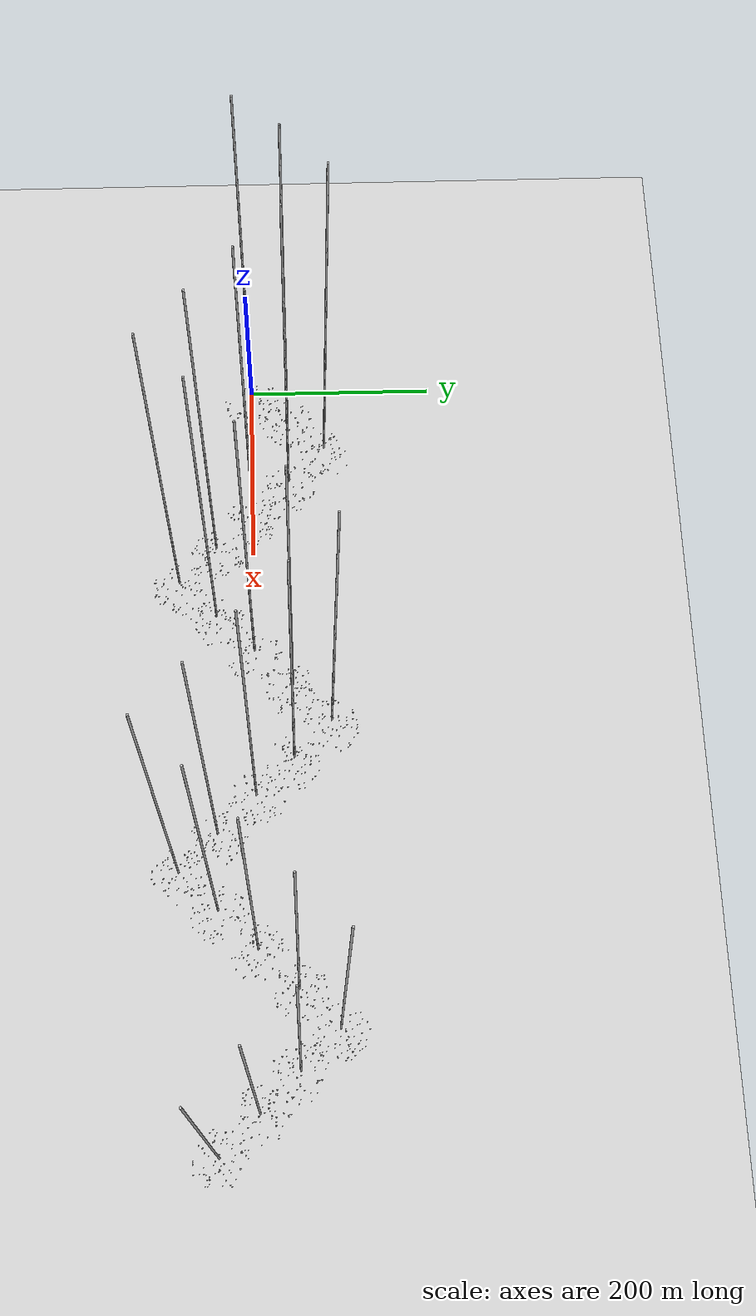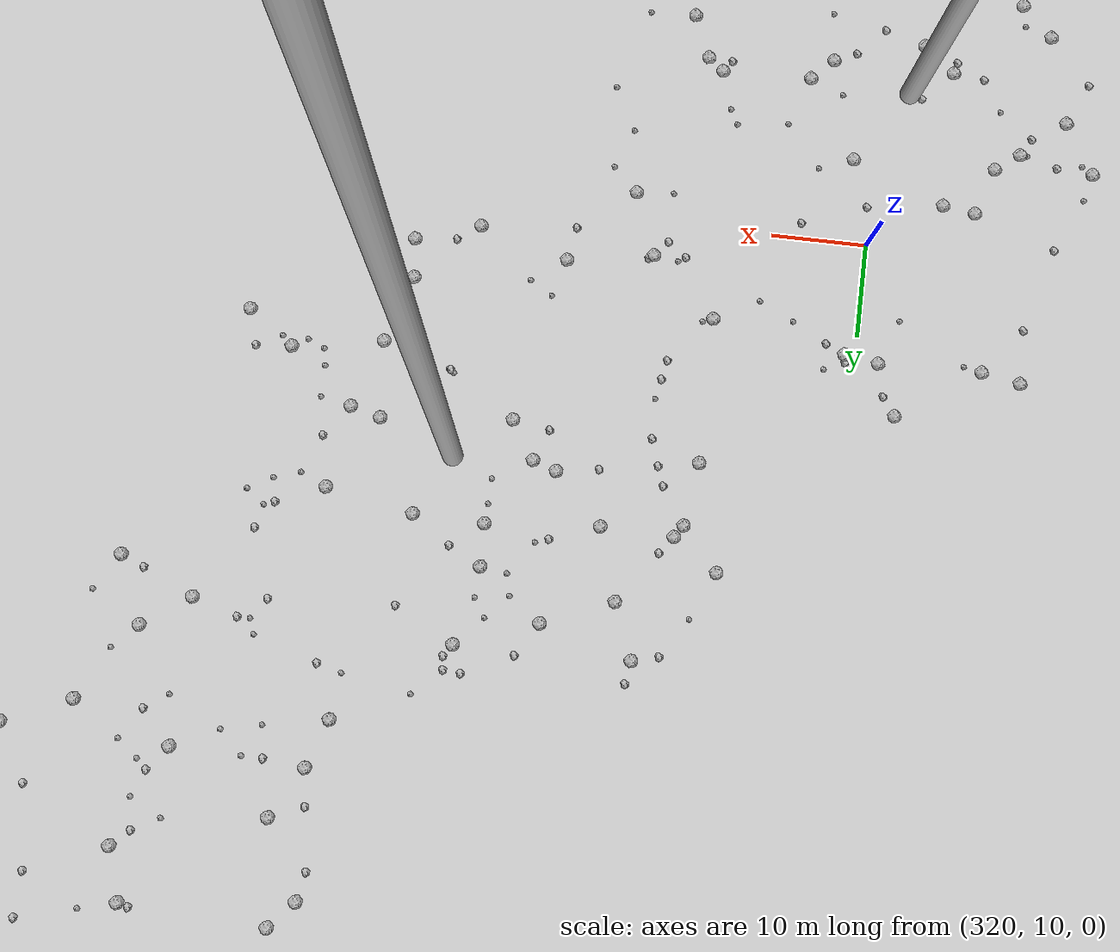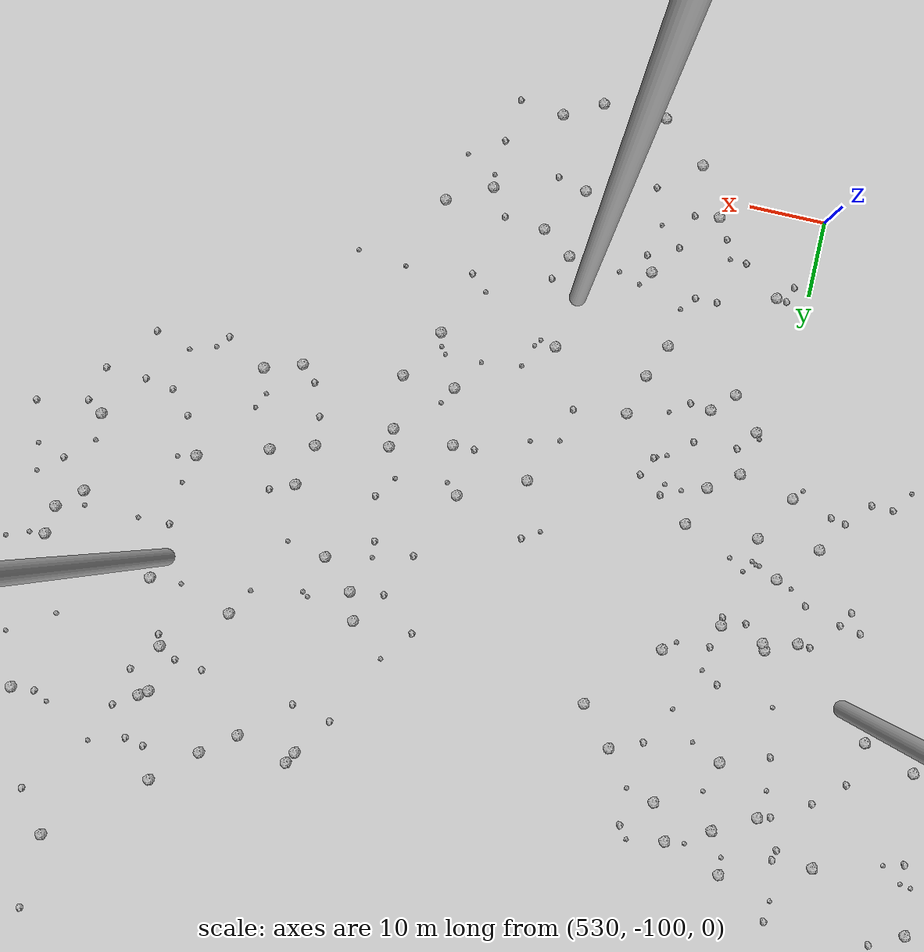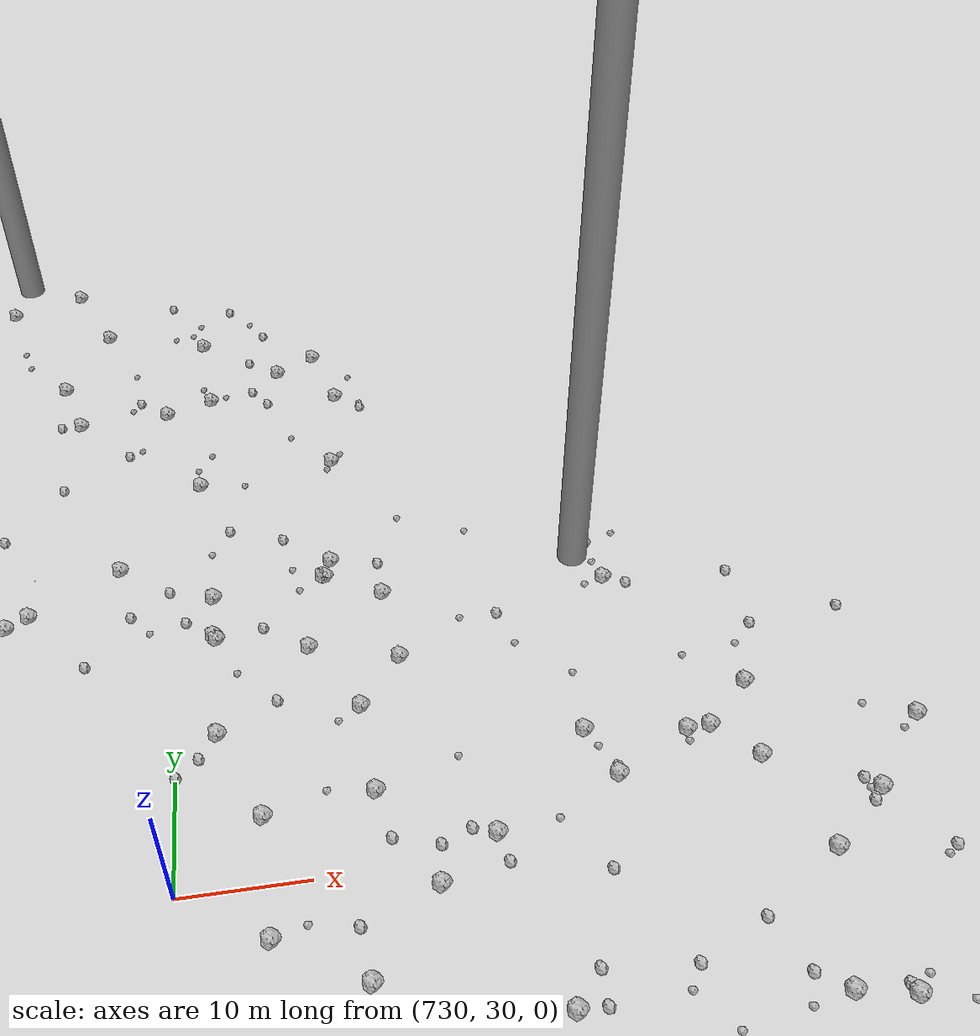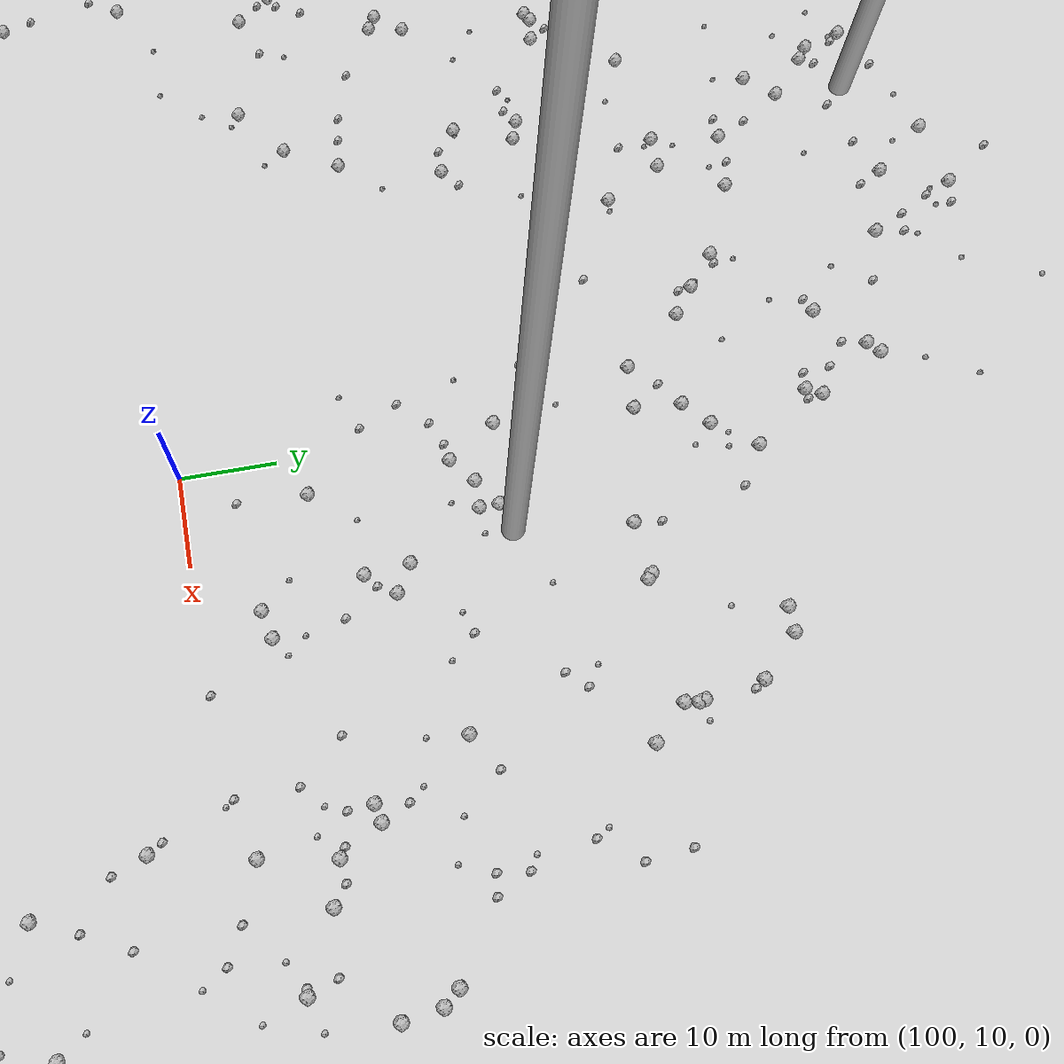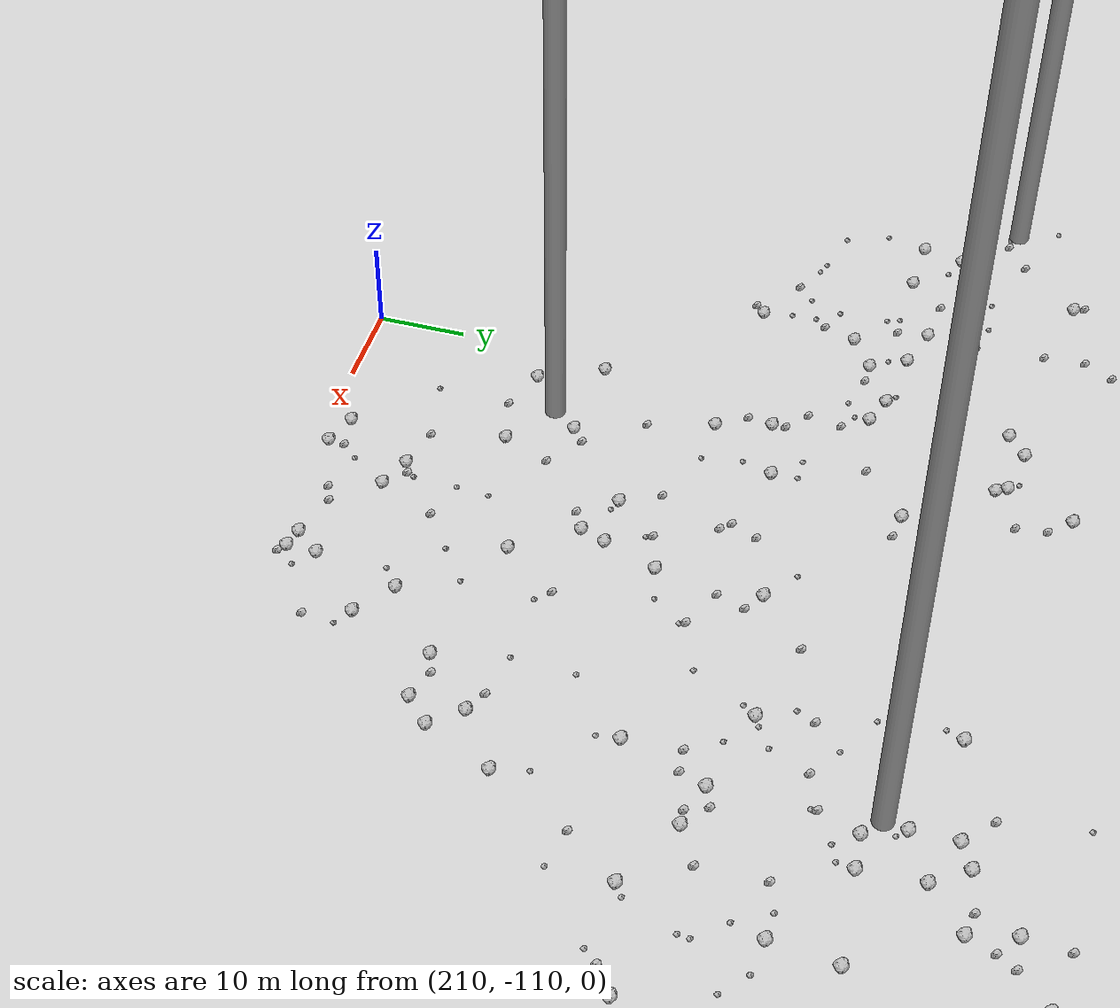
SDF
<sdf version="1.6">
 <world name="default">
  <include><uri>model://custom_ground</uri></include>
  <include><uri>model://sun</uri></include>
  <spherical_coordinates>
   <surface_model>EARTH_WGS84</surface_model>
   <latitude_deg>38.161479</latitude_deg>
   <longitude_deg>-122.454630</longitude_deg>
   <elevation>488.0</elevation>
   <heading_deg>90</heading_deg>
  </spherical_coordinates>
  <model name="rock1_0_0">
   <include><uri>model://rock1</uri><pose>24.325438476638766 -12.666199320690549 0.5 0 0 0</pose></include>
  </model>
  <model name="rock1_0_1">
   <include><uri>model://rock1</uri><pose>-5.893809356433241 20.249792027743183 0.5 0 0 0</pose></include>
  </model>
  <model name="rock1_0_2">
   <include><uri>model://rock1</uri><pose>-11.062064209260354 -9.87396268031712 0.5 0 0 0</pose></include>
  </model>
  <model name="rock1_0_3">
   <include><uri>model://rock1</uri><pose>-7.877165173493692 24.051439108281826 0.5 0 0 0</pose></include>
  </model>
  <model name="rock1_0_4">
   <include><uri>model://rock1</uri><pose>37.68089328828402 9.205226274176674 0.5 0 0 0</pose></include>
  </model>
  <model name="rock1_0_5">
   <include><uri>model://rock1</uri><pose>26.346021344524935 -2.5145571118482977 0.5 0 0 0</pose></include>
  </model>
  <model name="rock1_0_6">
   <include><uri>model://rock1</uri><pose>8.21649989373483 10.30994749182726 0.5 0 0 0</pose></include>
  </model>
  <model name="rock1_0_7">
   <include><uri>model://rock1</uri><pose>8.07006496846516 29.25697962112428 0.5 0 0 0</pose></include>
  </model>
  <model name="rock1_0_8">
   <include><uri>model://rock1</uri><pose>22.583753250336315 -7.715271131935225 0.5 0 0 0</pose></include>
  </model>
  <model name="rock1_0_9">
   <include><uri>model://rock1</uri><pose>22.433678400981314 19.277669025581652 0.5 0 0 0</pose></include>
  </model>
  <model name="rock1_0_10">
   <include><uri>model://rock1</uri><pose>-0.49667110488272925 24.188822406946294 0.5 0 0 0</pose></include>
  </model>
  <model name="rock1_0_11">
   <include><uri>model://rock1</uri><pose>-8.736563647119786 -1.9364166542888697 0.5 0 0 0</pose></include>
  </model>
  <model name="rock1_0_12">
   <include><uri>model://rock1</uri><pose>38.34962597712685 -4.304223239252597 0.5 0 0 0</pose></include>
  </model>
  <model name="rock1_0_13">
   <include><uri>model://rock1</uri><pose>-3.1293085721548337 12.604415784075762 0.5 0 0 0</pose></include>
  </model>
  <model name="rock1_0_14">
   <include><uri>model://rock1</uri><pose>13.16253624953783 19.742805017306132 0.5 0 0 0</pose></include>
  </model>
  <model name="rock1_0_15">
   <include><uri>model://rock1</uri><pose>-0.454560728156423 16.99648442970976 0.5 0 0 0</pose></include>
  </model>
  <model name="rock1_0_16">
   <include><uri>model://rock1</uri><pose>6.214675152829834 -1.310457777817362 0.5 0 0 0</pose></include>
  </model>
  <model name="rock1_0_17">
   <include><uri>model://rock1</uri><pose>17.82218228197835 -27.07736413559462 0.5 0 0 0</pose></include>
  </model>
  <model name="rock1_0_18">
   <include><uri>model://rock1</uri><pose>19.231514353455573 13.106946977044942 0.5 0 0 0</pose></include>
  </model>
  <model name="rock1_0_19">
   <include><uri>model://rock1</uri><pose>12.145363220462649 8.837828711901345 0.5 0 0 0</pose></include>
  </model>
  <model name="rock1_0_20">
   <include><uri>model://rock1</uri><pose>5.773477294142221 9.800401081477773 0.5 0 0 0</pose></include>
  </model>
  <model name="rock1_0_21">
   <include><uri>model://rock1</uri><pose>12.102914212719874 21.34705634418551 0.5 0 0 0</pose></include>
  </model>
  <model name="rock1_0_22">
   <include><uri>model://rock1</uri><pose>19.92723023798903 -27.096372045152094 0.5 0 0 0</pose></include>
  </model>
  <model name="rock1_0_23">
   <include><uri>model://rock1</uri><pose>11.884848952390385 13.226940965303676 0.5 0 0 0</pose></include>
  </model>
  <model name="rock1_0_24">
   <include><uri>model://rock1</uri><pose>29.357030674864603 -4.806862924520004 0.5 0 0 0</pose></include>
  </model>
  <model name="rock1_0_25">
   <include><uri>model://rock1</uri><pose>22.89703959085528 -14.008497871783284 0.5 0 0 0</pose></include>
  </model>
  <model name="rock1_0_26">
   <include><uri>model://rock1</uri><pose>29.677251916934118 -15.693929621102074 0.5 0 0 0</pose></include>
  </model>
  <model name="rock2_0_0">
   <include><uri>model://rock2</uri><pose>9.645066545660722 8.961004652136168 0.3 0 0 0</pose></include>
  </model>
  <model name="rock2_0_1">
   <include><uri>model://rock2</uri><pose>-5.217468325920054 1.5814991032763324 0.3 0 0 0</pose></include>
  </model>
  <model name="rock2_0_2">
   <include><uri>model://rock2</uri><pose>32.026275177198556 2.758592262892556 0.3 0 0 0</pose></include>
  </model>
  <model name="rock2_0_3">
   <include><uri>model://rock2</uri><pose>-6.424305366758336 6.098343460213556 0.3 0 0 0</pose></include>
  </model>
  <model name="rock2_0_4">
   <include><uri>model://rock2</uri><pose>29.63123955854212 8.730582005632876 0.3 0 0 0</pose></include>
  </model>
  <model name="rock2_0_5">
   <include><uri>model://rock2</uri><pose>-4.337981553960944 14.543295985822915 0.3 0 0 0</pose></include>
  </model>
  <model name="rock2_0_6">
   <include><uri>model://rock2</uri><pose>-10.830756599409842 6.204522401754637 0.3 0 0 0</pose></include>
  </model>
  <model name="rock2_0_7">
   <include><uri>model://rock2</uri><pose>-7.6715217527889195 19.113020097405055 0.3 0 0 0</pose></include>
  </model>
  <model name="rock2_0_8">
   <include><uri>model://rock2</uri><pose>-0.10734010284042483 -17.19033815688005 0.3 0 0 0</pose></include>
  </model>
  <model name="rock2_0_9">
   <include><uri>model://rock2</uri><pose>37.24685007907477 -1.0647079182749977 0.3 0 0 0</pose></include>
  </model>
  <model name="rock2_0_10">
   <include><uri>model://rock2</uri><pose>12.772120795193686 -13.783719805063548 0.3 0 0 0</pose></include>
  </model>
  <model name="rock2_0_11">
   <include><uri>model://rock2</uri><pose>8.088448252956663 -7.218155883120968 0.3 0 0 0</pose></include>
  </model>
  <model name="rock2_0_12">
   <include><uri>model://rock2</uri><pose>26.562166593687472 9.457052359187955 0.3 0 0 0</pose></include>
  </model>
  <model name="rock2_0_13">
   <include><uri>model://rock2</uri><pose>35.50685997618997 5.952027971333187 0.3 0 0 0</pose></include>
  </model>
  <model name="rock2_0_14">
   <include><uri>model://rock2</uri><pose>12.955506873889682 26.04111292460565 0.3 0 0 0</pose></include>
  </model>
  <model name="rock2_0_15">
   <include><uri>model://rock2</uri><pose>26.42040449670735 -23.765729671345554 0.3 0 0 0</pose></include>
  </model>
  <model name="rock2_0_16">
   <include><uri>model://rock2</uri><pose>32.34378709587166 17.88415663732753 0.3 0 0 0</pose></include>
  </model>
  <model name="rock2_0_17">
   <include><uri>model://rock2</uri><pose>7.4747816493819705 17.785652997047535 0.3 0 0 0</pose></include>
  </model>
  <model name="rock2_0_18">
   <include><uri>model://rock2</uri><pose>7.107785189532052 4.341748700008999 0.3 0 0 0</pose></include>
  </model>
  <model name="rock2_0_19">
   <include><uri>model://rock2</uri><pose>20.81328731999249 26.890539220576755 0.3 0 0 0</pose></include>
  </model>
  <model name="rock2_0_20">
   <include><uri>model://rock2</uri><pose>26.745741627666327 -24.856491467690333 0.3 0 0 0</pose></include>
  </model>
  <model name="rock2_0_21">
   <include><uri>model://rock2</uri><pose>-7.915189349447553 -7.533465930105734 0.3 0 0 0</pose></include>
  </model>
  <model name="rock2_0_22">
   <include><uri>model://rock2</uri><pose>-9.570171693252199 -1.9154770432301937 0.3 0 0 0</pose></include>
  </model>
  <model name="rock2_0_23">
   <include><uri>model://rock2</uri><pose>11.215254360831285 12.957706950522663 0.3 0 0 0</pose></include>
  </model>
  <model name="rock2_0_24">
   <include><uri>model://rock2</uri><pose>-14.098573012102804 -11.012612074172239 0.3 0 0 0</pose></include>
  </model>
  <model name="rock2_0_25">
   <include><uri>model://rock2</uri><pose>8.995436565034634 -29.632975803173192 0.3 0 0 0</pose></include>
  </model>
  <model name="rock2_0_26">
   <include><uri>model://rock2</uri><pose>16.998059088007587 -21.993395014825893 0.3 0 0 0</pose></include>
  </model>
  <model name="rock3_0_0">
   <include><uri>model://rock3</uri><pose>20.271931995975116 26.22855022037895 0.2 0 0 0</pose></include>
  </model>
  <model name="rock3_0_1">
   <include><uri>model://rock3</uri><pose>23.178899671987814 11.863206484446039 0.2 0 0 0</pose></include>
  </model>
  <model name="rock3_0_2">
   <include><uri>model://rock3</uri><pose>-2.8192454932723443 -2.6705484965161865 0.2 0 0 0</pose></include>
  </model>
  <model name="rock3_0_3">
   <include><uri>model://rock3</uri><pose>27.056178384845694 14.517453712017229 0.2 0 0 0</pose></include>
  </model>
  <model name="rock3_0_4">
   <include><uri>model://rock3</uri><pose>24.074464337881466 21.395803925402504 0.2 0 0 0</pose></include>
  </model>
  <model name="rock3_0_5">
   <include><uri>model://rock3</uri><pose>-9.015322952565054 2.4163148531344447 0.2 0 0 0</pose></include>
  </model>
  <model name="rock3_0_6">
   <include><uri>model://rock3</uri><pose>30.05586655170623 -2.6728539884157207 0.2 0 0 0</pose></include>
  </model>
  <model name="rock3_0_7">
   <include><uri>model://rock3</uri><pose>-5.473306718393271 -15.239721535573349 0.2 0 0 0</pose></include>
  </model>
  <model name="rock3_0_8">
   <include><uri>model://rock3</uri><pose>19.63574178334325 21.870290048151197 0.2 0 0 0</pose></include>
  </model>
  <model name="rock3_0_9">
   <include><uri>model://rock3</uri><pose>12.79886539942423 1.2653618442206813 0.2 0 0 0</pose></include>
  </model>
  <model name="rock3_0_10">
   <include><uri>model://rock3</uri><pose>-4.942047483773527 12.585931708254478 0.2 0 0 0</pose></include>
  </model>
  <model name="rock3_0_11">
   <include><uri>model://rock3</uri><pose>-8.85948541260143 6.225824040457873 0.2 0 0 0</pose></include>
  </model>
  <model name="rock3_0_12">
   <include><uri>model://rock3</uri><pose>-8.985547198340992 -2.87159019322419 0.2 0 0 0</pose></include>
  </model>
  <model name="rock3_0_13">
   <include><uri>model://rock3</uri><pose>5.143705703650557 25.215164830312887 0.2 0 0 0</pose></include>
  </model>
  <model name="rock3_0_14">
   <include><uri>model://rock3</uri><pose>24.145914447241587 -16.318498465870288 0.2 0 0 0</pose></include>
  </model>
  <model name="rock3_0_15">
   <include><uri>model://rock3</uri><pose>9.791843902324018 -12.560385947329124 0.2 0 0 0</pose></include>
  </model>
  <model name="rock3_0_16">
   <include><uri>model://rock3</uri><pose>26.417274453434686 8.069595184900258 0.2 0 0 0</pose></include>
  </model>
  <model name="rock3_0_17">
   <include><uri>model://rock3</uri><pose>16.151690370357095 -11.680365063987178 0.2 0 0 0</pose></include>
  </model>
  <model name="rock3_0_18">
   <include><uri>model://rock3</uri><pose>0.7247366999531621 27.024153889944074 0.2 0 0 0</pose></include>
  </model>
  <model name="rock3_0_19">
   <include><uri>model://rock3</uri><pose>7.815780938441076 -14.600548656237013 0.2 0 0 0</pose></include>
  </model>
  <model name="rock3_0_20">
   <include><uri>model://rock3</uri><pose>10.639802430317268 -24.78716942089214 0.2 0 0 0</pose></include>
  </model>
  <model name="rock3_0_21">
   <include><uri>model://rock3</uri><pose>12.402209624710196 1.0462613212254297 0.2 0 0 0</pose></include>
  </model>
  <model name="rock3_0_22">
   <include><uri>model://rock3</uri><pose>13.70342327779845 -18.18142686505167 0.2 0 0 0</pose></include>
  </model>
  <model name="rock3_0_23">
   <include><uri>model://rock3</uri><pose>21.205034900830512 15.260854085443178 0.2 0 0 0</pose></include>
  </model>
  <model name="rock3_0_24">
   <include><uri>model://rock3</uri><pose>-2.843183508700047 15.288147780187693 0.2 0 0 0</pose></include>
  </model>
  <model name="rock3_0_25">
   <include><uri>model://rock3</uri><pose>3.671590087576252 -9.027523480629515 0.2 0 0 0</pose></include>
  </model>
  <model name="rock3_0_26">
   <include><uri>model://rock3</uri><pose>8.870476266712231 26.838688207194124 0.2 0 0 0</pose></include>
  </model>
  <model name="rock1_1_0">
   <include><uri>model://rock1</uri><pose>43.860341984282655 39.14678680592159 0.5 0 0 0</pose></include>
  </model>
  <model name="rock1_1_1">
   <include><uri>model://rock1</uri><pose>47.63376585585048 57.283580657402766 0.5 0 0 0</pose></include>
  </model>
  <model name="rock1_1_2">
   <include><uri>model://rock1</uri><pose>61.86861712064712 45.44613492881588 0.5 0 0 0</pose></include>
  </model>
  <model name="rock1_1_3">
   <include><uri>model://rock1</uri><pose>64.44453833504659 31.7892707942957 0.5 0 0 0</pose></include>
  </model>
  <model name="rock1_1_4">
   <include><uri>model://rock1</uri><pose>17.26439615203395 55.879657092004614 0.5 0 0 0</pose></include>
  </model>
  <model name="rock1_1_5">
   <include><uri>model://rock1</uri><pose>38.731550028921156 27.03368827150665 0.5 0 0 0</pose></include>
  </model>
  <model name="rock1_1_6">
   <include><uri>model://rock1</uri><pose>29.255194165309934 15.290076704564024 0.5 0 0 0</pose></include>
  </model>
  <model name="rock1_1_7">
   <include><uri>model://rock1</uri><pose>24.27787695878262 56.21199432847169 0.5 0 0 0</pose></include>
  </model>
  <model name="rock1_1_8">
   <include><uri>model://rock1</uri><pose>33.46736963438262 34.02104305034158 0.5 0 0 0</pose></include>
  </model>
  <model name="rock1_1_9">
   <include><uri>model://rock1</uri><pose>61.30986565707229 25.995727295439664 0.5 0 0 0</pose></include>
  </model>
  <model name="rock1_1_10">
   <include><uri>model://rock1</uri><pose>31.645412922658668 16.289115775705355 0.5 0 0 0</pose></include>
  </model>
  <model name="rock1_1_11">
   <include><uri>model://rock1</uri><pose>41.77923874433452 23.311391708744274 0.5 0 0 0</pose></include>
  </model>
  <model name="rock1_1_12">
   <include><uri>model://rock1</uri><pose>24.01942412481332 44.285295207903374 0.5 0 0 0</pose></include>
  </model>
  <model name="rock1_1_13">
   <include><uri>model://rock1</uri><pose>55.35931236182698 21.571504473560264 0.5 0 0 0</pose></include>
  </model>
  <model name="rock1_1_14">
   <include><uri>model://rock1</uri><pose>64.25254181924402 51.93118598166682 0.5 0 0 0</pose></include>
  </model>
  <model name="rock1_1_15">
   <include><uri>model://rock1</uri><pose>45.53792491383273 38.24030625321822 0.5 0 0 0</pose></include>
  </model>
  <model name="rock1_1_16">
   <include><uri>model://rock1</uri><pose>21.586948748717084 30.584535495970343 0.5 0 0 0</pose></include>
  </model>
  <model name="rock1_1_17">
   <include><uri>model://rock1</uri><pose>30.997519232220764 49.35671211568597 0.5 0 0 0</pose></include>
  </model>
  <model name="rock1_1_18">
   <include><uri>model://rock1</uri><pose>67.32163910178224 43.12028949645106 0.5 0 0 0</pose></include>
  </model>
  <model name="rock1_1_19">
   <include><uri>model://rock1</uri><pose>22.30208175973258 57.295129755258614 0.5 0 0 0</pose></include>
  </model>
  <model name="rock1_1_20">
   <include><uri>model://rock1</uri><pose>46.519630421119295 56.757965122139 0.5 0 0 0</pose></include>
  </model>
  <model name="rock1_1_21">
   <include><uri>model://rock1</uri><pose>37.752399231768464 52.21309222546353 0.5 0 0 0</pose></include>
  </model>
  <model name="rock1_1_22">
   <include><uri>model://rock1</uri><pose>50.42340705526315 56.80204466322401 0.5 0 0 0</pose></include>
  </model>
  <model name="rock1_1_23">
   <include><uri>model://rock1</uri><pose>32.90338999763052 64.64515968713829 0.5 0 0 0</pose></include>
  </model>
  <model name="rock1_1_24">
   <include><uri>model://rock1</uri><pose>61.95010196811732 52.74305987911026 0.5 0 0 0</pose></include>
  </model>
  <model name="rock1_1_25">
   <include><uri>model://rock1</uri><pose>46.32871988673858 42.1128384200063 0.5 0 0 0</pose></include>
  </model>
  <model name="rock1_1_26">
   <include><uri>model://rock1</uri><pose>43.858761134334884 61.85263798540699 0.5 0 0 0</pose></include>
  </model>
  <model name="rock2_1_0">
   <include><uri>model://rock2</uri><pose>69.32670571511032 44.75421627536674 0.3 0 0 0</pose></include>
  </model>
  <model name="rock2_1_1">
   <include><uri>model://rock2</uri><pose>60.79622731275298 32.29995585464803 0.3 0 0 0</pose></include>
  </model>
  <model name="rock2_1_2">
   <include><uri>model://rock2</uri><pose>32.25515094205046 67.2006210376907 0.3 0 0 0</pose></include>
  </model>
  <model name="rock2_1_3">
   <include><uri>model://rock2</uri><pose>48.983248490343016 58.74434161301288 0.3 0 0 0</pose></include>
  </model>
  <model name="rock2_1_4">
   <include><uri>model://rock2</uri><pose>46.742609433982246 25.06086333064532 0.3 0 0 0</pose></include>
  </model>
  <model name="rock2_1_5">
   <include><uri>model://rock2</uri><pose>25.740051048130734 32.08650703335576 0.3 0 0 0</pose></include>
  </model>
  <model name="rock2_1_6">
   <include><uri>model://rock2</uri><pose>23.8618254578002 64.56035099786833 0.3 0 0 0</pose></include>
  </model>
  <model name="rock2_1_7">
   <include><uri>model://rock2</uri><pose>29.36589155412986 47.78042804620434 0.3 0 0 0</pose></include>
  </model>
  <model name="rock2_1_8">
   <include><uri>model://rock2</uri><pose>41.495174866310876 51.47010337577832 0.3 0 0 0</pose></include>
  </model>
  <model name="rock2_1_9">
   <include><uri>model://rock2</uri><pose>60.10309776771657 51.65207294708104 0.3 0 0 0</pose></include>
  </model>
  <model name="rock2_1_10">
   <include><uri>model://rock2</uri><pose>44.329355019089405 69.38559662967995 0.3 0 0 0</pose></include>
  </model>
  <model name="rock2_1_11">
   <include><uri>model://rock2</uri><pose>33.61758720048184 37.417417747349425 0.3 0 0 0</pose></include>
  </model>
  <model name="rock2_1_12">
   <include><uri>model://rock2</uri><pose>23.370287969209297 44.17047096589508 0.3 0 0 0</pose></include>
  </model>
  <model name="rock2_1_13">
   <include><uri>model://rock2</uri><pose>19.931918470917367 30.109165321167833 0.3 0 0 0</pose></include>
  </model>
  <model name="rock2_1_14">
   <include><uri>model://rock2</uri><pose>34.572390441472685 36.45984716122387 0.3 0 0 0</pose></include>
  </model>
  <model name="rock2_1_15">
   <include><uri>model://rock2</uri><pose>41.48613580195082 30.61976627949358 0.3 0 0 0</pose></include>
  </model>
  <model name="rock2_1_16">
   <include><uri>model://rock2</uri><pose>40.035319383103385 27.89492091690209 0.3 0 0 0</pose></include>
  </model>
  <model name="rock2_1_17">
   <include><uri>model://rock2</uri><pose>42.624947450175256 68.9355669274538 0.3 0 0 0</pose></include>
  </model>
  <model name="rock2_1_18">
   <include><uri>model://rock2</uri><pose>29.877984042605004 22.993197406516792 0.3 0 0 0</pose></include>
  </model>
  <model name="rock2_1_19">
   <include><uri>model://rock2</uri><pose>57.8017709453605 32.76055162305169 0.3 0 0 0</pose></include>
  </model>
  <model name="rock2_1_20">
   <include><uri>model://rock2</uri><pose>16.433398705618643 57.673287043650475 0.3 0 0 0</pose></include>
  </model>
  <model name="rock2_1_21">
   <include><uri>model://rock2</uri><pose>36.06350838538309 51.59498767324347 0.3 0 0 0</pose></include>
  </model>
  <model name="rock2_1_22">
   <include><uri>model://rock2</uri><pose>39.5780463629061 25.68720818869033 0.3 0 0 0</pose></include>
  </model>
  <model name="rock2_1_23">
   <include><uri>model://rock2</uri><pose>57.034662359804635 51.47759618204026 0.3 0 0 0</pose></include>
  </model>
  <model name="rock2_1_24">
   <include><uri>model://rock2</uri><pose>64.40007768344063 43.30963604079823 0.3 0 0 0</pose></include>
  </model>
  <model name="rock2_1_25">
   <include><uri>model://rock2</uri><pose>36.408807873769064 32.33536836791433 0.3 0 0 0</pose></include>
  </model>
  <model name="rock2_1_26">
   <include><uri>model://rock2</uri><pose>51.74784041583319 34.60689369372108 0.3 0 0 0</pose></include>
  </model>
  <model name="rock3_1_0">
   <include><uri>model://rock3</uri><pose>22.904424925557144 30.47573308157784 0.2 0 0 0</pose></include>
  </model>
  <model name="rock3_1_1">
   <include><uri>model://rock3</uri><pose>38.31647628878615 50.21082997464524 0.2 0 0 0</pose></include>
  </model>
  <model name="rock3_1_2">
   <include><uri>model://rock3</uri><pose>34.70570241406481 63.47203010306297 0.2 0 0 0</pose></include>
  </model>
  <model name="rock3_1_3">
   <include><uri>model://rock3</uri><pose>34.102301580320116 14.573606576328862 0.2 0 0 0</pose></include>
  </model>
  <model name="rock3_1_4">
   <include><uri>model://rock3</uri><pose>38.176961413609746 42.75324565951476 0.2 0 0 0</pose></include>
  </model>
  <model name="rock3_1_5">
   <include><uri>model://rock3</uri><pose>35.947846892071595 16.097399567725333 0.2 0 0 0</pose></include>
  </model>
  <model name="rock3_1_6">
   <include><uri>model://rock3</uri><pose>58.44316809130667 52.47748105501658 0.2 0 0 0</pose></include>
  </model>
  <model name="rock3_1_7">
   <include><uri>model://rock3</uri><pose>52.99898924967465 63.42934929258425 0.2 0 0 0</pose></include>
  </model>
  <model name="rock3_1_8">
   <include><uri>model://rock3</uri><pose>62.643024808491894 23.619938531245595 0.2 0 0 0</pose></include>
  </model>
  <model name="rock3_1_9">
   <include><uri>model://rock3</uri><pose>54.60966350900845 17.389295278241782 0.2 0 0 0</pose></include>
  </model>
  <model name="rock3_1_10">
   <include><uri>model://rock3</uri><pose>17.525965774233537 28.528632568103088 0.2 0 0 0</pose></include>
  </model>
  <model name="rock3_1_11">
   <include><uri>model://rock3</uri><pose>42.01074433168563 53.33860643591861 0.2 0 0 0</pose></include>
  </model>
  <model name="rock3_1_12">
   <include><uri>model://rock3</uri><pose>51.51615713590948 47.30451855597027 0.2 0 0 0</pose></include>
  </model>
  <model name="rock3_1_13">
   <include><uri>model://rock3</uri><pose>20.72021730938558 25.701925816072468 0.2 0 0 0</pose></include>
  </model>
  <model name="rock3_1_14">
   <include><uri>model://rock3</uri><pose>11.367460440446893 36.744020532789676 0.2 0 0 0</pose></include>
  </model>
  <model name="rock3_1_15">
   <include><uri>model://rock3</uri><pose>68.16587837895916 36.21310051658172 0.2 0 0 0</pose></include>
  </model>
  <model name="rock3_1_16">
   <include><uri>model://rock3</uri><pose>50.65827590572424 12.95827735065892 0.2 0 0 0</pose></include>
  </model>
  <model name="rock3_1_17">
   <include><uri>model://rock3</uri><pose>34.27074116677083 36.31016295646578 0.2 0 0 0</pose></include>
  </model>
  <model name="rock3_1_18">
   <include><uri>model://rock3</uri><pose>44.141430337061315 68.03650006213303 0.2 0 0 0</pose></include>
  </model>
  <model name="rock3_1_19">
   <include><uri>model://rock3</uri><pose>47.57799167223044 27.83194470466268 0.2 0 0 0</pose></include>
  </model>
  <model name="rock3_1_20">
   <include><uri>model://rock3</uri><pose>62.33256766970996 45.51937826605379 0.2 0 0 0</pose></include>
  </model>
  <model name="rock3_1_21">
   <include><uri>model://rock3</uri><pose>47.70710696028744 49.99152422866516 0.2 0 0 0</pose></include>
  </model>
  <model name="rock3_1_22">
   <include><uri>model://rock3</uri><pose>56.619092820905756 20.553058597804405 0.2 0 0 0</pose></include>
  </model>
  <model name="rock3_1_23">
   <include><uri>model://rock3</uri><pose>23.88167712230439 42.33396731460219 0.2 0 0 0</pose></include>
  </model>
  <model name="rock3_1_24">
   <include><uri>model://rock3</uri><pose>43.98601330808306 12.809335490614547 0.2 0 0 0</pose></include>
  </model>
  <model name="rock3_1_25">
   <include><uri>model://rock3</uri><pose>25.79517649323885 63.60110149783848 0.2 0 0 0</pose></include>
  </model>
  <model name="rock3_1_26">
   <include><uri>model://rock3</uri><pose>21.378572454647824 31.27293112586913 0.2 0 0 0</pose></include>
  </model>
  <model name="rock1_2_0">
   <include><uri>model://rock1</uri><pose>87.06369623425357 67.11447100779517 0.5 0 0 0</pose></include>
  </model>
  <model name="rock1_2_1">
   <include><uri>model://rock1</uri><pose>83.70598544894605 89.01641879467893 0.5 0 0 0</pose></include>
  </model>
  <model name="rock1_2_2">
   <include><uri>model://rock1</uri><pose>70.82986397510686 98.02342574258512 0.5 0 0 0</pose></include>
  </model>
  <model name="rock1_2_3">
   <include><uri>model://rock1</uri><pose>74.78670239229854 54.82627124075793 0.5 0 0 0</pose></include>
  </model>
  <model name="rock1_2_4">
   <include><uri>model://rock1</uri><pose>63.43613985632204 83.08909117536791 0.5 0 0 0</pose></include>
  </model>
  <model name="rock1_2_5">
   <include><uri>model://rock1</uri><pose>90.19592100714205 64.72917535126535 0.5 0 0 0</pose></include>
  </model>
  <model name="rock1_2_6">
   <include><uri>model://rock1</uri><pose>103.64968243347194 65.08940893090573 0.5 0 0 0</pose></include>
  </model>
  <model name="rock1_2_7">
   <include><uri>model://rock1</uri><pose>102.38709346840892 77.56687804405648 0.5 0 0 0</pose></include>
  </model>
  <model name="rock1_2_8">
   <include><uri>model://rock1</uri><pose>101.50609671342235 75.9333547227384 0.5 0 0 0</pose></include>
  </model>
  <model name="rock1_2_9">
   <include><uri>model://rock1</uri><pose>60.56972132591557 79.98173430274434 0.5 0 0 0</pose></include>
  </model>
  <model name="rock1_2_10">
   <include><uri>model://rock1</uri><pose>78.6897947170244 99.0277760527223 0.5 0 0 0</pose></include>
  </model>
  <model name="rock1_2_11">
   <include><uri>model://rock1</uri><pose>58.930843159104654 87.1409733459096 0.5 0 0 0</pose></include>
  </model>
  <model name="rock1_2_12">
   <include><uri>model://rock1</uri><pose>74.78576524705841 74.13687097870836 0.5 0 0 0</pose></include>
  </model>
  <model name="rock1_2_13">
   <include><uri>model://rock1</uri><pose>55.35260277043017 65.9279657826611 0.5 0 0 0</pose></include>
  </model>
  <model name="rock1_2_14">
   <include><uri>model://rock1</uri><pose>74.42254612517817 60.790599570407814 0.5 0 0 0</pose></include>
  </model>
  <model name="rock1_2_15">
   <include><uri>model://rock1</uri><pose>75.93699249406151 91.81363913052465 0.5 0 0 0</pose></include>
  </model>
  <model name="rock1_2_16">
   <include><uri>model://rock1</uri><pose>95.60943505555487 58.12803571327668 0.5 0 0 0</pose></include>
  </model>
  <model name="rock1_2_17">
   <include><uri>model://rock1</uri><pose>106.97024711684278 69.48228724858912 0.5 0 0 0</pose></include>
  </model>
  <model name="rock1_2_18">
   <include><uri>model://rock1</uri><pose>97.24656333041465 83.91936529520689 0.5 0 0 0</pose></include>
  </model>
  <model name="rock1_2_19">
   <include><uri>model://rock1</uri><pose>57.37713183422149 88.30188948038307 0.5 0 0 0</pose></include>
  </model>
  <model name="rock1_2_20">
   <include><uri>model://rock1</uri><pose>55.99783638607211 92.65925318175708 0.5 0 0 0</pose></include>
  </model>
  <model name="rock1_2_21">
   <include><uri>model://rock1</uri><pose>98.60220359639663 85.07308854065828 0.5 0 0 0</pose></include>
  </model>
  <model name="rock1_2_22">
   <include><uri>model://rock1</uri><pose>83.389989041831 70.2021983378479 0.5 0 0 0</pose></include>
  </model>
  <model name="rock1_2_23">
   <include><uri>model://rock1</uri><pose>70.88010642545484 67.25982974969732 0.5 0 0 0</pose></include>
  </model>
  <model name="rock1_2_24">
   <include><uri>model://rock1</uri><pose>92.42641313509597 79.35851771146474 0.5 0 0 0</pose></include>
  </model>
  <model name="rock1_2_25">
   <include><uri>model://rock1</uri><pose>68.13937434478433 75.06866005173228 0.5 0 0 0</pose></include>
  </model>
  <model name="rock1_2_26">
   <include><uri>model://rock1</uri><pose>67.13979424270953 67.39350674545182 0.5 0 0 0</pose></include>
  </model>
  <model name="rock2_2_0">
   <include><uri>model://rock2</uri><pose>84.09519894402283 92.25775693363555 0.3 0 0 0</pose></include>
  </model>
  <model name="rock2_2_1">
   <include><uri>model://rock2</uri><pose>67.50619501585041 63.57358234361713 0.3 0 0 0</pose></include>
  </model>
  <model name="rock2_2_2">
   <include><uri>model://rock2</uri><pose>79.93452406047038 96.09050244356058 0.3 0 0 0</pose></include>
  </model>
  <model name="rock2_2_3">
   <include><uri>model://rock2</uri><pose>99.22566657660158 79.33717433273037 0.3 0 0 0</pose></include>
  </model>
  <model name="rock2_2_4">
   <include><uri>model://rock2</uri><pose>65.5090930675448 75.16013290654946 0.3 0 0 0</pose></include>
  </model>
  <model name="rock2_2_5">
   <include><uri>model://rock2</uri><pose>74.51976132896424 104.64478153073671 0.3 0 0 0</pose></include>
  </model>
  <model name="rock2_2_6">
   <include><uri>model://rock2</uri><pose>90.73177248128093 78.76060394413179 0.3 0 0 0</pose></include>
  </model>
  <model name="rock2_2_7">
   <include><uri>model://rock2</uri><pose>81.22815282975195 52.03576124166257 0.3 0 0 0</pose></include>
  </model>
  <model name="rock2_2_8">
   <include><uri>model://rock2</uri><pose>96.58457429050873 81.3743742938122 0.3 0 0 0</pose></include>
  </model>
  <model name="rock2_2_9">
   <include><uri>model://rock2</uri><pose>89.71298313509374 86.95252762032979 0.3 0 0 0</pose></include>
  </model>
  <model name="rock2_2_10">
   <include><uri>model://rock2</uri><pose>84.00699356366749 55.87412983201831 0.3 0 0 0</pose></include>
  </model>
  <model name="rock2_2_11">
   <include><uri>model://rock2</uri><pose>87.26965238589455 65.72502691092863 0.3 0 0 0</pose></include>
  </model>
  <model name="rock2_2_12">
   <include><uri>model://rock2</uri><pose>66.38031779182518 78.54022652479776 0.3 0 0 0</pose></include>
  </model>
  <model name="rock2_2_13">
   <include><uri>model://rock2</uri><pose>60.84024311500842 58.87139551276722 0.3 0 0 0</pose></include>
  </model>
  <model name="rock2_2_14">
   <include><uri>model://rock2</uri><pose>77.24672225288957 89.27302565130191 0.3 0 0 0</pose></include>
  </model>
  <model name="rock2_2_15">
   <include><uri>model://rock2</uri><pose>65.81436711966143 88.68485275679379 0.3 0 0 0</pose></include>
  </model>
  <model name="rock2_2_16">
   <include><uri>model://rock2</uri><pose>84.4935875708149 70.39129460611801 0.3 0 0 0</pose></include>
  </model>
  <model name="rock2_2_17">
   <include><uri>model://rock2</uri><pose>71.56749080515328 75.18215063186625 0.3 0 0 0</pose></include>
  </model>
  <model name="rock2_2_18">
   <include><uri>model://rock2</uri><pose>81.32461656343764 98.58012285655273 0.3 0 0 0</pose></include>
  </model>
  <model name="rock2_2_19">
   <include><uri>model://rock2</uri><pose>99.49595942558224 76.33091400262366 0.3 0 0 0</pose></include>
  </model>
  <model name="rock2_2_20">
   <include><uri>model://rock2</uri><pose>102.59532961266763 76.03719084590844 0.3 0 0 0</pose></include>
  </model>
  <model name="rock2_2_21">
   <include><uri>model://rock2</uri><pose>60.980105631259576 95.18500619674356 0.3 0 0 0</pose></include>
  </model>
  <model name="rock2_2_22">
   <include><uri>model://rock2</uri><pose>71.38324740953226 90.11664409654207 0.3 0 0 0</pose></include>
  </model>
  <model name="rock2_2_23">
   <include><uri>model://rock2</uri><pose>59.7143813806238 88.7922597366274 0.3 0 0 0</pose></include>
  </model>
  <model name="rock2_2_24">
   <include><uri>model://rock2</uri><pose>81.87339484745839 92.6567036400788 0.3 0 0 0</pose></include>
  </model>
  <model name="rock2_2_25">
   <include><uri>model://rock2</uri><pose>98.10197796004464 60.855443652847875 0.3 0 0 0</pose></include>
  </model>
  <model name="rock2_2_26">
   <include><uri>model://rock2</uri><pose>56.9121320988436 91.5674196973876 0.3 0 0 0</pose></include>
  </model>
  <model name="rock3_2_0">
   <include><uri>model://rock3</uri><pose>56.03305611852922 91.56760205431928 0.2 0 0 0</pose></include>
  </model>
  <model name="rock3_2_1">
   <include><uri>model://rock3</uri><pose>102.71865616478775 94.84659859797668 0.2 0 0 0</pose></include>
  </model>
  <model name="rock3_2_2">
   <include><uri>model://rock3</uri><pose>92.08974168867894 105.48790015610953 0.2 0 0 0</pose></include>
  </model>
  <model name="rock3_2_3">
   <include><uri>model://rock3</uri><pose>99.88774160875238 89.71302434456939 0.2 0 0 0</pose></include>
  </model>
  <model name="rock3_2_4">
   <include><uri>model://rock3</uri><pose>90.00268596319026 75.17902955559438 0.2 0 0 0</pose></include>
  </model>
  <model name="rock3_2_5">
   <include><uri>model://rock3</uri><pose>84.19024017677046 72.66391630633784 0.2 0 0 0</pose></include>
  </model>
  <model name="rock3_2_6">
   <include><uri>model://rock3</uri><pose>59.77412697077837 76.62833025171305 0.2 0 0 0</pose></include>
  </model>
  <model name="rock3_2_7">
   <include><uri>model://rock3</uri><pose>81.24769940030248 96.8495695450403 0.2 0 0 0</pose></include>
  </model>
  <model name="rock3_2_8">
   <include><uri>model://rock3</uri><pose>93.91645186985616 68.90701732937507 0.2 0 0 0</pose></include>
  </model>
  <model name="rock3_2_9">
   <include><uri>model://rock3</uri><pose>51.911486522450346 77.57466808387048 0.2 0 0 0</pose></include>
  </model>
  <model name="rock3_2_10">
   <include><uri>model://rock3</uri><pose>86.34308537095043 67.79394224685586 0.2 0 0 0</pose></include>
  </model>
  <model name="rock3_2_11">
   <include><uri>model://rock3</uri><pose>71.8636054282536 51.38147028236174 0.2 0 0 0</pose></include>
  </model>
  <model name="rock3_2_12">
   <include><uri>model://rock3</uri><pose>68.11280266846424 69.74837931388011 0.2 0 0 0</pose></include>
  </model>
  <model name="rock3_2_13">
   <include><uri>model://rock3</uri><pose>87.04635929527902 83.00439116165504 0.2 0 0 0</pose></include>
  </model>
  <model name="rock3_2_14">
   <include><uri>model://rock3</uri><pose>79.03390481725144 96.8308692835441 0.2 0 0 0</pose></include>
  </model>
  <model name="rock3_2_15">
   <include><uri>model://rock3</uri><pose>88.48488635377065 97.4586362844382 0.2 0 0 0</pose></include>
  </model>
  <model name="rock3_2_16">
   <include><uri>model://rock3</uri><pose>84.6019514284747 93.66504896073431 0.2 0 0 0</pose></include>
  </model>
  <model name="rock3_2_17">
   <include><uri>model://rock3</uri><pose>71.84070484779528 84.19590974532983 0.2 0 0 0</pose></include>
  </model>
  <model name="rock3_2_18">
   <include><uri>model://rock3</uri><pose>71.80466709905897 73.13636526840352 0.2 0 0 0</pose></include>
  </model>
  <model name="rock3_2_19">
   <include><uri>model://rock3</uri><pose>75.65323493853285 60.72368505346648 0.2 0 0 0</pose></include>
  </model>
  <model name="rock3_2_20">
   <include><uri>model://rock3</uri><pose>54.73545888879066 85.14493910068887 0.2 0 0 0</pose></include>
  </model>
  <model name="rock3_2_21">
   <include><uri>model://rock3</uri><pose>104.84433972252538 66.78674622474028 0.2 0 0 0</pose></include>
  </model>
  <model name="rock3_2_22">
   <include><uri>model://rock3</uri><pose>65.59064229179506 96.71805214691318 0.2 0 0 0</pose></include>
  </model>
  <model name="rock3_2_23">
   <include><uri>model://rock3</uri><pose>60.66640540305901 63.56281306995044 0.2 0 0 0</pose></include>
  </model>
  <model name="rock3_2_24">
   <include><uri>model://rock3</uri><pose>67.69622053316895 66.52203533562724 0.2 0 0 0</pose></include>
  </model>
  <model name="rock3_2_25">
   <include><uri>model://rock3</uri><pose>51.999553930815466 89.95715788266978 0.2 0 0 0</pose></include>
  </model>
  <model name="rock3_2_26">
   <include><uri>model://rock3</uri><pose>71.94845874983899 94.64010973856682 0.2 0 0 0</pose></include>
  </model>
  <model name="rock1_3_0">
   <include><uri>model://rock1</uri><pose>127.49155892241109 67.53730742906274 0.5 0 0 0</pose></include>
  </model>
  <model name="rock1_3_1">
   <include><uri>model://rock1</uri><pose>132.47340747625674 55.199052176825454 0.5 0 0 0</pose></include>
  </model>
  <model name="rock1_3_2">
   <include><uri>model://rock1</uri><pose>119.01904420712239 17.118556033420223 0.5 0 0 0</pose></include>
  </model>
  <model name="rock1_3_3">
   <include><uri>model://rock1</uri><pose>132.5596565892663 57.20815048332782 0.5 0 0 0</pose></include>
  </model>
  <model name="rock1_3_4">
   <include><uri>model://rock1</uri><pose>131.6320893868718 63.39288361824905 0.5 0 0 0</pose></include>
  </model>
  <model name="rock1_3_5">
   <include><uri>model://rock1</uri><pose>114.02383149784441 26.965056480249434 0.5 0 0 0</pose></include>
  </model>
  <model name="rock1_3_6">
   <include><uri>model://rock1</uri><pose>108.83182523712533 39.62681090801733 0.5 0 0 0</pose></include>
  </model>
  <model name="rock1_3_7">
   <include><uri>model://rock1</uri><pose>95.00893944350916 47.40207691925368 0.5 0 0 0</pose></include>
  </model>
  <model name="rock1_3_8">
   <include><uri>model://rock1</uri><pose>113.58725462434457 31.711356280111332 0.5 0 0 0</pose></include>
  </model>
  <model name="rock1_3_9">
   <include><uri>model://rock1</uri><pose>116.00017751017474 16.443645221317457 0.5 0 0 0</pose></include>
  </model>
  <model name="rock1_3_10">
   <include><uri>model://rock1</uri><pose>100.88061352080706 62.67903880923583 0.5 0 0 0</pose></include>
  </model>
  <model name="rock1_3_11">
   <include><uri>model://rock1</uri><pose>135.90336554883172 51.6183259372756 0.5 0 0 0</pose></include>
  </model>
  <model name="rock1_3_12">
   <include><uri>model://rock1</uri><pose>108.77981402168712 41.69652849699172 0.5 0 0 0</pose></include>
  </model>
  <model name="rock1_3_13">
   <include><uri>model://rock1</uri><pose>118.95558126986941 55.21236202239991 0.5 0 0 0</pose></include>
  </model>
  <model name="rock1_3_14">
   <include><uri>model://rock1</uri><pose>132.69763983021193 56.59838984550959 0.5 0 0 0</pose></include>
  </model>
  <model name="rock1_3_15">
   <include><uri>model://rock1</uri><pose>116.53155253181663 29.911186232391806 0.5 0 0 0</pose></include>
  </model>
  <model name="rock1_3_16">
   <include><uri>model://rock1</uri><pose>113.23950811342513 54.70952367720558 0.5 0 0 0</pose></include>
  </model>
  <model name="rock1_3_17">
   <include><uri>model://rock1</uri><pose>103.02325243202165 37.573773167269756 0.5 0 0 0</pose></include>
  </model>
  <model name="rock1_3_18">
   <include><uri>model://rock1</uri><pose>124.78514199382795 67.63914819497153 0.5 0 0 0</pose></include>
  </model>
  <model name="rock1_3_19">
   <include><uri>model://rock1</uri><pose>138.72971796236297 24.766138300100785 0.5 0 0 0</pose></include>
  </model>
  <model name="rock1_3_20">
   <include><uri>model://rock1</uri><pose>119.49354273525287 54.71749798091163 0.5 0 0 0</pose></include>
  </model>
  <model name="rock1_3_21">
   <include><uri>model://rock1</uri><pose>131.90116917011323 34.30813592618303 0.5 0 0 0</pose></include>
  </model>
  <model name="rock1_3_22">
   <include><uri>model://rock1</uri><pose>99.59816658220882 42.79946132334196 0.5 0 0 0</pose></include>
  </model>
  <model name="rock1_3_23">
   <include><uri>model://rock1</uri><pose>105.79612110904269 39.72266683530286 0.5 0 0 0</pose></include>
  </model>
  <model name="rock1_3_24">
   <include><uri>model://rock1</uri><pose>104.29223955045893 22.66902291665042 0.5 0 0 0</pose></include>
  </model>
  <model name="rock1_3_25">
   <include><uri>model://rock1</uri><pose>136.86519857966272 24.374826940939574 0.5 0 0 0</pose></include>
  </model>
  <model name="rock1_3_26">
   <include><uri>model://rock1</uri><pose>100.47780063274311 57.65590268672055 0.5 0 0 0</pose></include>
  </model>
  <model name="rock2_3_0">
   <include><uri>model://rock2</uri><pose>111.13384300357032 66.93354600651517 0.3 0 0 0</pose></include>
  </model>
  <model name="rock2_3_1">
   <include><uri>model://rock2</uri><pose>123.65726943084863 10.51065516691208 0.3 0 0 0</pose></include>
  </model>
  <model name="rock2_3_2">
   <include><uri>model://rock2</uri><pose>137.0256811434523 21.80566079586646 0.3 0 0 0</pose></include>
  </model>
  <model name="rock2_3_3">
   <include><uri>model://rock2</uri><pose>135.71071066956347 36.63850731826858 0.3 0 0 0</pose></include>
  </model>
  <model name="rock2_3_4">
   <include><uri>model://rock2</uri><pose>101.03054203687036 37.35685910349226 0.3 0 0 0</pose></include>
  </model>
  <model name="rock2_3_5">
   <include><uri>model://rock2</uri><pose>129.2541502469302 46.59729250854283 0.3 0 0 0</pose></include>
  </model>
  <model name="rock2_3_6">
   <include><uri>model://rock2</uri><pose>118.17119687986255 24.51735363356891 0.3 0 0 0</pose></include>
  </model>
  <model name="rock2_3_7">
   <include><uri>model://rock2</uri><pose>115.37078985467433 28.097884815383747 0.3 0 0 0</pose></include>
  </model>
  <model name="rock2_3_8">
   <include><uri>model://rock2</uri><pose>147.26036750754898 34.097569205652036 0.3 0 0 0</pose></include>
  </model>
  <model name="rock2_3_9">
   <include><uri>model://rock2</uri><pose>143.67735777180715 44.16648119097395 0.3 0 0 0</pose></include>
  </model>
  <model name="rock2_3_10">
   <include><uri>model://rock2</uri><pose>95.54574087178946 33.29145978802669 0.3 0 0 0</pose></include>
  </model>
  <model name="rock2_3_11">
   <include><uri>model://rock2</uri><pose>140.28195796246757 21.092513322864452 0.3 0 0 0</pose></include>
  </model>
  <model name="rock2_3_12">
   <include><uri>model://rock2</uri><pose>137.2794674466505 27.668620451803495 0.3 0 0 0</pose></include>
  </model>
  <model name="rock2_3_13">
   <include><uri>model://rock2</uri><pose>146.08338374986664 52.85488324084219 0.3 0 0 0</pose></include>
  </model>
  <model name="rock2_3_14">
   <include><uri>model://rock2</uri><pose>133.97942161759417 17.78033354491986 0.3 0 0 0</pose></include>
  </model>
  <model name="rock2_3_15">
   <include><uri>model://rock2</uri><pose>93.08801513335133 46.895680340763846 0.3 0 0 0</pose></include>
  </model>
  <model name="rock2_3_16">
   <include><uri>model://rock2</uri><pose>103.94657652235955 15.406888592040627 0.3 0 0 0</pose></include>
  </model>
  <model name="rock2_3_17">
   <include><uri>model://rock2</uri><pose>121.89843118841776 36.70435011934499 0.3 0 0 0</pose></include>
  </model>
  <model name="rock2_3_18">
   <include><uri>model://rock2</uri><pose>129.75781883269013 22.357589352716175 0.3 0 0 0</pose></include>
  </model>
  <model name="rock2_3_19">
   <include><uri>model://rock2</uri><pose>98.35202371895348 36.26784792301985 0.3 0 0 0</pose></include>
  </model>
  <model name="rock2_3_20">
   <include><uri>model://rock2</uri><pose>113.48847755400215 57.641646958611894 0.3 0 0 0</pose></include>
  </model>
  <model name="rock2_3_21">
   <include><uri>model://rock2</uri><pose>97.67348084974768 29.032906101457506 0.3 0 0 0</pose></include>
  </model>
  <model name="rock2_3_22">
   <include><uri>model://rock2</uri><pose>127.4097376426574 44.6310640362247 0.3 0 0 0</pose></include>
  </model>
  <model name="rock2_3_23">
   <include><uri>model://rock2</uri><pose>146.54900591025742 48.093278156031715 0.3 0 0 0</pose></include>
  </model>
  <model name="rock2_3_24">
   <include><uri>model://rock2</uri><pose>145.12343196359228 34.42137488168335 0.3 0 0 0</pose></include>
  </model>
  <model name="rock2_3_25">
   <include><uri>model://rock2</uri><pose>132.29330461304903 62.422017102810926 0.3 0 0 0</pose></include>
  </model>
  <model name="rock2_3_26">
   <include><uri>model://rock2</uri><pose>145.51622211035118 37.56251921813208 0.3 0 0 0</pose></include>
  </model>
  <model name="rock3_3_0">
   <include><uri>model://rock3</uri><pose>136.19995918737766 19.73938303540712 0.2 0 0 0</pose></include>
  </model>
  <model name="rock3_3_1">
   <include><uri>model://rock3</uri><pose>127.17370236073454 47.92820854544455 0.2 0 0 0</pose></include>
  </model>
  <model name="rock3_3_2">
   <include><uri>model://rock3</uri><pose>98.44666644784208 49.7316452082238 0.2 0 0 0</pose></include>
  </model>
  <model name="rock3_3_3">
   <include><uri>model://rock3</uri><pose>135.98833737128848 29.174699697490773 0.2 0 0 0</pose></include>
  </model>
  <model name="rock3_3_4">
   <include><uri>model://rock3</uri><pose>93.6139168682743 27.462696272655492 0.2 0 0 0</pose></include>
  </model>
  <model name="rock3_3_5">
   <include><uri>model://rock3</uri><pose>118.02889561319039 45.346682079965326 0.2 0 0 0</pose></include>
  </model>
  <model name="rock3_3_6">
   <include><uri>model://rock3</uri><pose>107.8573437130603 27.1954258608509 0.2 0 0 0</pose></include>
  </model>
  <model name="rock3_3_7">
   <include><uri>model://rock3</uri><pose>139.41340205000353 32.40942179119931 0.2 0 0 0</pose></include>
  </model>
  <model name="rock3_3_8">
   <include><uri>model://rock3</uri><pose>107.69903823957758 36.957105236000324 0.2 0 0 0</pose></include>
  </model>
  <model name="rock3_3_9">
   <include><uri>model://rock3</uri><pose>142.8484265451177 45.48307773914672 0.2 0 0 0</pose></include>
  </model>
  <model name="rock3_3_10">
   <include><uri>model://rock3</uri><pose>105.68181729725995 63.0425422098988 0.2 0 0 0</pose></include>
  </model>
  <model name="rock3_3_11">
   <include><uri>model://rock3</uri><pose>113.10732172149984 19.549435116291345 0.2 0 0 0</pose></include>
  </model>
  <model name="rock3_3_12">
   <include><uri>model://rock3</uri><pose>113.91309721634885 27.069776221718854 0.2 0 0 0</pose></include>
  </model>
  <model name="rock3_3_13">
   <include><uri>model://rock3</uri><pose>119.53134568453989 35.92172134040227 0.2 0 0 0</pose></include>
  </model>
  <model name="rock3_3_14">
   <include><uri>model://rock3</uri><pose>138.8568818471158 18.655283196166998 0.2 0 0 0</pose></include>
  </model>
  <model name="rock3_3_15">
   <include><uri>model://rock3</uri><pose>120.91138295209898 18.405671602226597 0.2 0 0 0</pose></include>
  </model>
  <model name="rock3_3_16">
   <include><uri>model://rock3</uri><pose>119.1897281837096 20.355636085511374 0.2 0 0 0</pose></include>
  </model>
  <model name="rock3_3_17">
   <include><uri>model://rock3</uri><pose>123.58149780793116 62.219637829493536 0.2 0 0 0</pose></include>
  </model>
  <model name="rock3_3_18">
   <include><uri>model://rock3</uri><pose>124.28494637832603 34.037513106576355 0.2 0 0 0</pose></include>
  </model>
  <model name="rock3_3_19">
   <include><uri>model://rock3</uri><pose>134.60736187349997 57.235391779454865 0.2 0 0 0</pose></include>
  </model>
  <model name="rock3_3_20">
   <include><uri>model://rock3</uri><pose>111.6018100512446 39.70544514495616 0.2 0 0 0</pose></include>
  </model>
  <model name="rock3_3_21">
   <include><uri>model://rock3</uri><pose>143.7346312087028 31.0500572584712 0.2 0 0 0</pose></include>
  </model>
  <model name="rock3_3_22">
   <include><uri>model://rock3</uri><pose>106.43215771460689 66.44256141854632 0.2 0 0 0</pose></include>
  </model>
  <model name="rock3_3_23">
   <include><uri>model://rock3</uri><pose>131.43049999765293 30.187356756356706 0.2 0 0 0</pose></include>
  </model>
  <model name="rock3_3_24">
   <include><uri>model://rock3</uri><pose>93.69039041628103 39.69138415631238 0.2 0 0 0</pose></include>
  </model>
  <model name="rock3_3_25">
   <include><uri>model://rock3</uri><pose>100.85750150165593 62.710146506166346 0.2 0 0 0</pose></include>
  </model>
  <model name="rock3_3_26">
   <include><uri>model://rock3</uri><pose>144.0864404008102 38.400313253644306 0.2 0 0 0</pose></include>
  </model>
  <model name="rock1_4_0">
   <include><uri>model://rock1</uri><pose>178.65468104062157 7.993470533126086 0.5 0 0 0</pose></include>
  </model>
  <model name="rock1_4_1">
   <include><uri>model://rock1</uri><pose>149.005475823997 -15.316991608431538 0.5 0 0 0</pose></include>
  </model>
  <model name="rock1_4_2">
   <include><uri>model://rock1</uri><pose>175.6944459059037 13.775110313037565 0.5 0 0 0</pose></include>
  </model>
  <model name="rock1_4_3">
   <include><uri>model://rock1</uri><pose>141.09596691448638 -21.29481997495491 0.5 0 0 0</pose></include>
  </model>
  <model name="rock1_4_4">
   <include><uri>model://rock1</uri><pose>154.2699961229659 -24.46903517349388 0.5 0 0 0</pose></include>
  </model>
  <model name="rock1_4_5">
   <include><uri>model://rock1</uri><pose>162.69205032178948 13.077078027829835 0.5 0 0 0</pose></include>
  </model>
  <model name="rock1_4_6">
   <include><uri>model://rock1</uri><pose>157.0335022908318 -21.496144907240357 0.5 0 0 0</pose></include>
  </model>
  <model name="rock1_4_7">
   <include><uri>model://rock1</uri><pose>155.87906079806712 27.608210088360202 0.5 0 0 0</pose></include>
  </model>
  <model name="rock1_4_8">
   <include><uri>model://rock1</uri><pose>172.02147918555733 7.5741311580457165 0.5 0 0 0</pose></include>
  </model>
  <model name="rock1_4_9">
   <include><uri>model://rock1</uri><pose>154.50811895226937 29.241986406481935 0.5 0 0 0</pose></include>
  </model>
  <model name="rock1_4_10">
   <include><uri>model://rock1</uri><pose>137.83746832260493 3.0440760301310377 0.5 0 0 0</pose></include>
  </model>
  <model name="rock1_4_11">
   <include><uri>model://rock1</uri><pose>156.12093923704228 -16.849315882062417 0.5 0 0 0</pose></include>
  </model>
  <model name="rock1_4_12">
   <include><uri>model://rock1</uri><pose>141.37720046236473 -13.509726205467892 0.5 0 0 0</pose></include>
  </model>
  <model name="rock1_4_13">
   <include><uri>model://rock1</uri><pose>146.94322893879323 -14.437348020025134 0.5 0 0 0</pose></include>
  </model>
  <model name="rock1_4_14">
   <include><uri>model://rock1</uri><pose>145.59096400964364 19.274046710064276 0.5 0 0 0</pose></include>
  </model>
  <model name="rock1_4_15">
   <include><uri>model://rock1</uri><pose>167.86525709673396 -13.83897023358315 0.5 0 0 0</pose></include>
  </model>
  <model name="rock1_4_16">
   <include><uri>model://rock1</uri><pose>162.00206621557922 15.150213531984853 0.5 0 0 0</pose></include>
  </model>
  <model name="rock1_4_17">
   <include><uri>model://rock1</uri><pose>184.35625267277152 -6.431331935811961 0.5 0 0 0</pose></include>
  </model>
  <model name="rock1_4_18">
   <include><uri>model://rock1</uri><pose>170.3818155655479 14.598203242819622 0.5 0 0 0</pose></include>
  </model>
  <model name="rock1_4_19">
   <include><uri>model://rock1</uri><pose>154.34425374263398 -6.411300522886943 0.5 0 0 0</pose></include>
  </model>
  <model name="rock1_4_20">
   <include><uri>model://rock1</uri><pose>169.23058803726173 10.273370423694153 0.5 0 0 0</pose></include>
  </model>
  <model name="rock1_4_21">
   <include><uri>model://rock1</uri><pose>141.94692703605827 -8.055627840287798 0.5 0 0 0</pose></include>
  </model>
  <model name="rock1_4_22">
   <include><uri>model://rock1</uri><pose>141.330040406301 20.46624069922151 0.5 0 0 0</pose></include>
  </model>
  <model name="rock1_4_23">
   <include><uri>model://rock1</uri><pose>140.01349206360055 12.940233239371068 0.5 0 0 0</pose></include>
  </model>
  <model name="rock1_4_24">
   <include><uri>model://rock1</uri><pose>156.47292029151484 23.6537280957931 0.5 0 0 0</pose></include>
  </model>
  <model name="rock1_4_25">
   <include><uri>model://rock1</uri><pose>152.85852675368747 15.835086865533327 0.5 0 0 0</pose></include>
  </model>
  <model name="rock1_4_26">
   <include><uri>model://rock1</uri><pose>150.74742916535456 -21.824598272493695 0.5 0 0 0</pose></include>
  </model>
  <model name="rock2_4_0">
   <include><uri>model://rock2</uri><pose>180.64505052981377 17.759051534305357 0.3 0 0 0</pose></include>
  </model>
  <model name="rock2_4_1">
   <include><uri>model://rock2</uri><pose>136.8711705533388 4.5072837818091 0.3 0 0 0</pose></include>
  </model>
  <model name="rock2_4_2">
   <include><uri>model://rock2</uri><pose>174.9992102431872 -13.116510445718689 0.3 0 0 0</pose></include>
  </model>
  <model name="rock2_4_3">
   <include><uri>model://rock2</uri><pose>143.61925458666633 20.708200200981643 0.3 0 0 0</pose></include>
  </model>
  <model name="rock2_4_4">
   <include><uri>model://rock2</uri><pose>168.24640421859175 -7.92007268458741 0.3 0 0 0</pose></include>
  </model>
  <model name="rock2_4_5">
   <include><uri>model://rock2</uri><pose>134.06451428010502 11.51712592995775 0.3 0 0 0</pose></include>
  </model>
  <model name="rock2_4_6">
   <include><uri>model://rock2</uri><pose>145.5946187055917 10.900253418275518 0.3 0 0 0</pose></include>
  </model>
  <model name="rock2_4_7">
   <include><uri>model://rock2</uri><pose>183.17892870975456 5.4032468570780665 0.3 0 0 0</pose></include>
  </model>
  <model name="rock2_4_8">
   <include><uri>model://rock2</uri><pose>187.62079035843973 4.595555314567932 0.3 0 0 0</pose></include>
  </model>
  <model name="rock2_4_9">
   <include><uri>model://rock2</uri><pose>151.7494519709884 -26.988151672336727 0.3 0 0 0</pose></include>
  </model>
  <model name="rock2_4_10">
   <include><uri>model://rock2</uri><pose>139.16424685602405 -0.4219566243558788 0.3 0 0 0</pose></include>
  </model>
  <model name="rock2_4_11">
   <include><uri>model://rock2</uri><pose>152.0926618036832 15.844517128144354 0.3 0 0 0</pose></include>
  </model>
  <model name="rock2_4_12">
   <include><uri>model://rock2</uri><pose>175.7610557903555 -2.986379773497621 0.3 0 0 0</pose></include>
  </model>
  <model name="rock2_4_13">
   <include><uri>model://rock2</uri><pose>146.14323772260894 0.9855478048732564 0.3 0 0 0</pose></include>
  </model>
  <model name="rock2_4_14">
   <include><uri>model://rock2</uri><pose>180.0871896122771 -22.22577383214952 0.3 0 0 0</pose></include>
  </model>
  <model name="rock2_4_15">
   <include><uri>model://rock2</uri><pose>151.72755040667894 18.805328989654456 0.3 0 0 0</pose></include>
  </model>
  <model name="rock2_4_16">
   <include><uri>model://rock2</uri><pose>153.8189873713432 -17.89940713672267 0.3 0 0 0</pose></include>
  </model>
  <model name="rock2_4_17">
   <include><uri>model://rock2</uri><pose>166.84656973116665 19.529184454351814 0.3 0 0 0</pose></include>
  </model>
  <model name="rock2_4_18">
   <include><uri>model://rock2</uri><pose>143.80732673902068 -3.6450524268368447 0.3 0 0 0</pose></include>
  </model>
  <model name="rock2_4_19">
   <include><uri>model://rock2</uri><pose>175.98295710264094 -16.921278205841148 0.3 0 0 0</pose></include>
  </model>
  <model name="rock2_4_20">
   <include><uri>model://rock2</uri><pose>175.61360918967128 18.454818456287477 0.3 0 0 0</pose></include>
  </model>
  <model name="rock2_4_21">
   <include><uri>model://rock2</uri><pose>169.19799350617438 17.842533875406858 0.3 0 0 0</pose></include>
  </model>
  <model name="rock2_4_22">
   <include><uri>model://rock2</uri><pose>161.9743882891295 -20.695077262498504 0.3 0 0 0</pose></include>
  </model>
  <model name="rock2_4_23">
   <include><uri>model://rock2</uri><pose>186.93474856881636 0.6914706669599688 0.3 0 0 0</pose></include>
  </model>
  <model name="rock2_4_24">
   <include><uri>model://rock2</uri><pose>176.63868994754634 19.95500876488029 0.3 0 0 0</pose></include>
  </model>
  <model name="rock2_4_25">
   <include><uri>model://rock2</uri><pose>152.8981897235795 -11.414862821104037 0.3 0 0 0</pose></include>
  </model>
  <model name="rock2_4_26">
   <include><uri>model://rock2</uri><pose>149.01958948393474 9.129438450290309 0.3 0 0 0</pose></include>
  </model>
  <model name="rock3_4_0">
   <include><uri>model://rock3</uri><pose>187.60429975040356 8.214567192918892 0.2 0 0 0</pose></include>
  </model>
  <model name="rock3_4_1">
   <include><uri>model://rock3</uri><pose>156.10957667016308 16.851791322384173 0.2 0 0 0</pose></include>
  </model>
  <model name="rock3_4_2">
   <include><uri>model://rock3</uri><pose>185.602699537292 -0.9141753880559449 0.2 0 0 0</pose></include>
  </model>
  <model name="rock3_4_3">
   <include><uri>model://rock3</uri><pose>185.87849621328618 -7.146023669402698 0.2 0 0 0</pose></include>
  </model>
  <model name="rock3_4_4">
   <include><uri>model://rock3</uri><pose>149.49087376038122 14.289837432592478 0.2 0 0 0</pose></include>
  </model>
  <model name="rock3_4_5">
   <include><uri>model://rock3</uri><pose>152.3529785993769 -3.7983175166600667 0.2 0 0 0</pose></include>
  </model>
  <model name="rock3_4_6">
   <include><uri>model://rock3</uri><pose>154.44792217248713 11.543494980215478 0.2 0 0 0</pose></include>
  </model>
  <model name="rock3_4_7">
   <include><uri>model://rock3</uri><pose>168.3134292273922 21.330635087433762 0.2 0 0 0</pose></include>
  </model>
  <model name="rock3_4_8">
   <include><uri>model://rock3</uri><pose>186.08679657283835 14.19203321132376 0.2 0 0 0</pose></include>
  </model>
  <model name="rock3_4_9">
   <include><uri>model://rock3</uri><pose>146.7149163922678 -10.20927404408711 0.2 0 0 0</pose></include>
  </model>
  <model name="rock3_4_10">
   <include><uri>model://rock3</uri><pose>149.00578923817835 -27.734343846822412 0.2 0 0 0</pose></include>
  </model>
  <model name="rock3_4_11">
   <include><uri>model://rock3</uri><pose>166.29948352167003 16.493135704584994 0.2 0 0 0</pose></include>
  </model>
  <model name="rock3_4_12">
   <include><uri>model://rock3</uri><pose>173.99383769383712 -15.924141493450009 0.2 0 0 0</pose></include>
  </model>
  <model name="rock3_4_13">
   <include><uri>model://rock3</uri><pose>159.5699987208879 -8.934126293124788 0.2 0 0 0</pose></include>
  </model>
  <model name="rock3_4_14">
   <include><uri>model://rock3</uri><pose>134.65178311758305 10.63885036602435 0.2 0 0 0</pose></include>
  </model>
  <model name="rock3_4_15">
   <include><uri>model://rock3</uri><pose>150.59502463179922 6.652390906192743 0.2 0 0 0</pose></include>
  </model>
  <model name="rock3_4_16">
   <include><uri>model://rock3</uri><pose>157.00374907449986 -2.9809158168441456 0.2 0 0 0</pose></include>
  </model>
  <model name="rock3_4_17">
   <include><uri>model://rock3</uri><pose>164.6156614650982 5.391861944451868 0.2 0 0 0</pose></include>
  </model>
  <model name="rock3_4_18">
   <include><uri>model://rock3</uri><pose>162.46968642580447 9.803237309626589 0.2 0 0 0</pose></include>
  </model>
  <model name="rock3_4_19">
   <include><uri>model://rock3</uri><pose>161.12759784287252 8.555803663296011 0.2 0 0 0</pose></include>
  </model>
  <model name="rock3_4_20">
   <include><uri>model://rock3</uri><pose>155.66340735022064 -26.481989801532105 0.2 0 0 0</pose></include>
  </model>
  <model name="rock3_4_21">
   <include><uri>model://rock3</uri><pose>144.4974269863714 -13.615751230252698 0.2 0 0 0</pose></include>
  </model>
  <model name="rock3_4_22">
   <include><uri>model://rock3</uri><pose>156.42398124286785 -3.7080230071539546 0.2 0 0 0</pose></include>
  </model>
  <model name="rock3_4_23">
   <include><uri>model://rock3</uri><pose>182.0898250568996 -1.8673823330496084 0.2 0 0 0</pose></include>
  </model>
  <model name="rock3_4_24">
   <include><uri>model://rock3</uri><pose>179.35156647600763 0.8553452868296354 0.2 0 0 0</pose></include>
  </model>
  <model name="rock3_4_25">
   <include><uri>model://rock3</uri><pose>152.766420344741 -22.576543379030888 0.2 0 0 0</pose></include>
  </model>
  <model name="rock3_4_26">
   <include><uri>model://rock3</uri><pose>186.33008673396307 -4.890879963063231 0.2 0 0 0</pose></include>
  </model>
  <model name="rock1_5_0">
   <include><uri>model://rock1</uri><pose>221.0138212128513 -28.550851061289045 0.5 0 0 0</pose></include>
  </model>
  <model name="rock1_5_1">
   <include><uri>model://rock1</uri><pose>200.63130735563914 -49.85523631482019 0.5 0 0 0</pose></include>
  </model>
  <model name="rock1_5_2">
   <include><uri>model://rock1</uri><pose>211.2500133902515 -20.763554171147796 0.5 0 0 0</pose></include>
  </model>
  <model name="rock1_5_3">
   <include><uri>model://rock1</uri><pose>181.17045748823023 -46.67269700009619 0.5 0 0 0</pose></include>
  </model>
  <model name="rock1_5_4">
   <include><uri>model://rock1</uri><pose>186.72786324596166 -51.58293347784637 0.5 0 0 0</pose></include>
  </model>
  <model name="rock1_5_5">
   <include><uri>model://rock1</uri><pose>208.2910291984007 -17.10114484180216 0.5 0 0 0</pose></include>
  </model>
  <model name="rock1_5_6">
   <include><uri>model://rock1</uri><pose>212.39294463451137 -34.84338017241026 0.5 0 0 0</pose></include>
  </model>
  <model name="rock1_5_7">
   <include><uri>model://rock1</uri><pose>218.68175271241336 -37.09676256495785 0.5 0 0 0</pose></include>
  </model>
  <model name="rock1_5_8">
   <include><uri>model://rock1</uri><pose>210.489223921927 -15.515805908531817 0.5 0 0 0</pose></include>
  </model>
  <model name="rock1_5_9">
   <include><uri>model://rock1</uri><pose>208.02921491652808 -50.93958151688088 0.5 0 0 0</pose></include>
  </model>
  <model name="rock1_5_10">
   <include><uri>model://rock1</uri><pose>186.33104284810193 -32.75287839901597 0.5 0 0 0</pose></include>
  </model>
  <model name="rock1_5_11">
   <include><uri>model://rock1</uri><pose>172.75155749480527 -46.010065344924755 0.5 0 0 0</pose></include>
  </model>
  <model name="rock1_5_12">
   <include><uri>model://rock1</uri><pose>196.28554127068142 -42.92141603753488 0.5 0 0 0</pose></include>
  </model>
  <model name="rock1_5_13">
   <include><uri>model://rock1</uri><pose>209.6076004068471 -12.33834037855987 0.5 0 0 0</pose></include>
  </model>
  <model name="rock1_5_14">
   <include><uri>model://rock1</uri><pose>198.71509311773866 -56.33512249655334 0.5 0 0 0</pose></include>
  </model>
  <model name="rock1_5_15">
   <include><uri>model://rock1</uri><pose>195.56503760008508 -48.332741744414136 0.5 0 0 0</pose></include>
  </model>
  <model name="rock1_5_16">
   <include><uri>model://rock1</uri><pose>207.5539944882907 -14.131587250459809 0.5 0 0 0</pose></include>
  </model>
  <model name="rock1_5_17">
   <include><uri>model://rock1</uri><pose>197.03752139397318 -67.36398558068402 0.5 0 0 0</pose></include>
  </model>
  <model name="rock1_5_18">
   <include><uri>model://rock1</uri><pose>209.73161974667144 -36.9093373697792 0.5 0 0 0</pose></include>
  </model>
  <model name="rock1_5_19">
   <include><uri>model://rock1</uri><pose>225.32962313576363 -46.093612528689796 0.5 0 0 0</pose></include>
  </model>
  <model name="rock1_5_20">
   <include><uri>model://rock1</uri><pose>191.64600955584189 -19.478534738481095 0.5 0 0 0</pose></include>
  </model>
  <model name="rock1_5_21">
   <include><uri>model://rock1</uri><pose>217.9574820837525 -35.90173838124446 0.5 0 0 0</pose></include>
  </model>
  <model name="rock1_5_22">
   <include><uri>model://rock1</uri><pose>180.11317565733273 -51.31058077886546 0.5 0 0 0</pose></include>
  </model>
  <model name="rock1_5_23">
   <include><uri>model://rock1</uri><pose>203.46318578624198 -19.671396947597742 0.5 0 0 0</pose></include>
  </model>
  <model name="rock1_5_24">
   <include><uri>model://rock1</uri><pose>215.28040313245705 -62.34323157999631 0.5 0 0 0</pose></include>
  </model>
  <model name="rock1_5_25">
   <include><uri>model://rock1</uri><pose>202.70654421652247 -53.80804613152651 0.5 0 0 0</pose></include>
  </model>
  <model name="rock1_5_26">
   <include><uri>model://rock1</uri><pose>211.4596355891856 -52.160635719195696 0.5 0 0 0</pose></include>
  </model>
  <model name="rock2_5_0">
   <include><uri>model://rock2</uri><pose>190.1559689169245 -47.706781646398746 0.3 0 0 0</pose></include>
  </model>
  <model name="rock2_5_1">
   <include><uri>model://rock2</uri><pose>205.15232562349564 -53.845630364372994 0.3 0 0 0</pose></include>
  </model>
  <model name="rock2_5_2">
   <include><uri>model://rock2</uri><pose>213.2792726091329 -54.96391004629122 0.3 0 0 0</pose></include>
  </model>
  <model name="rock2_5_3">
   <include><uri>model://rock2</uri><pose>192.5764503376061 -45.18221263205166 0.3 0 0 0</pose></include>
  </model>
  <model name="rock2_5_4">
   <include><uri>model://rock2</uri><pose>179.84369212793445 -45.73233662662903 0.3 0 0 0</pose></include>
  </model>
  <model name="rock2_5_5">
   <include><uri>model://rock2</uri><pose>195.70135318903144 -68.44844485349806 0.3 0 0 0</pose></include>
  </model>
  <model name="rock2_5_6">
   <include><uri>model://rock2</uri><pose>180.12032633487556 -39.15751369603139 0.3 0 0 0</pose></include>
  </model>
  <model name="rock2_5_7">
   <include><uri>model://rock2</uri><pose>223.10279154643578 -30.882513243269507 0.3 0 0 0</pose></include>
  </model>
  <model name="rock2_5_8">
   <include><uri>model://rock2</uri><pose>195.23236981720498 -30.318957207789836 0.3 0 0 0</pose></include>
  </model>
  <model name="rock2_5_9">
   <include><uri>model://rock2</uri><pose>228.3089968755757 -46.48892526844345 0.3 0 0 0</pose></include>
  </model>
  <model name="rock2_5_10">
   <include><uri>model://rock2</uri><pose>214.12120527610062 -16.127422575022756 0.3 0 0 0</pose></include>
  </model>
  <model name="rock2_5_11">
   <include><uri>model://rock2</uri><pose>197.30729739002214 -59.98624600227004 0.3 0 0 0</pose></include>
  </model>
  <model name="rock2_5_12">
   <include><uri>model://rock2</uri><pose>223.5291003678424 -34.25471644784765 0.3 0 0 0</pose></include>
  </model>
  <model name="rock2_5_13">
   <include><uri>model://rock2</uri><pose>195.54855899223168 -34.92216125810634 0.3 0 0 0</pose></include>
  </model>
  <model name="rock2_5_14">
   <include><uri>model://rock2</uri><pose>195.89920069205732 -51.77364998678244 0.3 0 0 0</pose></include>
  </model>
  <model name="rock2_5_15">
   <include><uri>model://rock2</uri><pose>191.0309087712385 -64.23873839572869 0.3 0 0 0</pose></include>
  </model>
  <model name="rock2_5_16">
   <include><uri>model://rock2</uri><pose>185.68041632349247 -31.511847502302892 0.3 0 0 0</pose></include>
  </model>
  <model name="rock2_5_17">
   <include><uri>model://rock2</uri><pose>215.058306592806 -60.81409525839394 0.3 0 0 0</pose></include>
  </model>
  <model name="rock2_5_18">
   <include><uri>model://rock2</uri><pose>197.0454711477162 -27.08622507758303 0.3 0 0 0</pose></include>
  </model>
  <model name="rock2_5_19">
   <include><uri>model://rock2</uri><pose>176.6832054569514 -41.58998646944113 0.3 0 0 0</pose></include>
  </model>
  <model name="rock2_5_20">
   <include><uri>model://rock2</uri><pose>192.85381623351998 -23.620085974126305 0.3 0 0 0</pose></include>
  </model>
  <model name="rock2_5_21">
   <include><uri>model://rock2</uri><pose>212.6025847137165 -58.781733685433906 0.3 0 0 0</pose></include>
  </model>
  <model name="rock2_5_22">
   <include><uri>model://rock2</uri><pose>201.74911071610506 -17.166103556155576 0.3 0 0 0</pose></include>
  </model>
  <model name="rock2_5_23">
   <include><uri>model://rock2</uri><pose>227.1923252136517 -42.81828954383555 0.3 0 0 0</pose></include>
  </model>
  <model name="rock2_5_24">
   <include><uri>model://rock2</uri><pose>219.44366989272788 -50.97914354324165 0.3 0 0 0</pose></include>
  </model>
  <model name="rock2_5_25">
   <include><uri>model://rock2</uri><pose>211.01447470807375 -18.60908041271867 0.3 0 0 0</pose></include>
  </model>
  <model name="rock2_5_26">
   <include><uri>model://rock2</uri><pose>175.03414962477967 -41.45142909065201 0.3 0 0 0</pose></include>
  </model>
  <model name="rock3_5_0">
   <include><uri>model://rock3</uri><pose>204.28036524971702 -23.591704842912293 0.2 0 0 0</pose></include>
  </model>
  <model name="rock3_5_1">
   <include><uri>model://rock3</uri><pose>201.0064064019448 -51.9052797784946 0.2 0 0 0</pose></include>
  </model>
  <model name="rock3_5_2">
   <include><uri>model://rock3</uri><pose>183.58011415539087 -47.8313118639321 0.2 0 0 0</pose></include>
  </model>
  <model name="rock3_5_3">
   <include><uri>model://rock3</uri><pose>206.69127098556442 -49.99812965854632 0.2 0 0 0</pose></include>
  </model>
  <model name="rock3_5_4">
   <include><uri>model://rock3</uri><pose>187.9463066423447 -42.01984921096298 0.2 0 0 0</pose></include>
  </model>
  <model name="rock3_5_5">
   <include><uri>model://rock3</uri><pose>172.4574434253119 -36.195577155045875 0.2 0 0 0</pose></include>
  </model>
  <model name="rock3_5_6">
   <include><uri>model://rock3</uri><pose>192.26808765143946 -41.73374736677524 0.2 0 0 0</pose></include>
  </model>
  <model name="rock3_5_7">
   <include><uri>model://rock3</uri><pose>185.9944706689159 -62.04767014599709 0.2 0 0 0</pose></include>
  </model>
  <model name="rock3_5_8">
   <include><uri>model://rock3</uri><pose>187.430021707111 -62.569244734332365 0.2 0 0 0</pose></include>
  </model>
  <model name="rock3_5_9">
   <include><uri>model://rock3</uri><pose>192.94187681109528 -18.60664981568756 0.2 0 0 0</pose></include>
  </model>
  <model name="rock3_5_10">
   <include><uri>model://rock3</uri><pose>196.15843480496812 -64.12649800353304 0.2 0 0 0</pose></include>
  </model>
  <model name="rock3_5_11">
   <include><uri>model://rock3</uri><pose>194.02900057079458 -53.326598178117315 0.2 0 0 0</pose></include>
  </model>
  <model name="rock3_5_12">
   <include><uri>model://rock3</uri><pose>210.38124226705457 -44.66465702219317 0.2 0 0 0</pose></include>
  </model>
  <model name="rock3_5_13">
   <include><uri>model://rock3</uri><pose>216.86785774401454 -34.73880262814911 0.2 0 0 0</pose></include>
  </model>
  <model name="rock3_5_14">
   <include><uri>model://rock3</uri><pose>222.12597378987448 -41.779416815885654 0.2 0 0 0</pose></include>
  </model>
  <model name="rock3_5_15">
   <include><uri>model://rock3</uri><pose>185.20298383954506 -45.364791790819964 0.2 0 0 0</pose></include>
  </model>
  <model name="rock3_5_16">
   <include><uri>model://rock3</uri><pose>211.24761904918464 -53.79895950707774 0.2 0 0 0</pose></include>
  </model>
  <model name="rock3_5_17">
   <include><uri>model://rock3</uri><pose>209.1715735987989 -54.95369938614729 0.2 0 0 0</pose></include>
  </model>
  <model name="rock3_5_18">
   <include><uri>model://rock3</uri><pose>201.2255164642511 -21.983989912781254 0.2 0 0 0</pose></include>
  </model>
  <model name="rock3_5_19">
   <include><uri>model://rock3</uri><pose>178.97135568221952 -25.430977399179433 0.2 0 0 0</pose></include>
  </model>
  <model name="rock3_5_20">
   <include><uri>model://rock3</uri><pose>194.28529358374158 -58.81248859342732 0.2 0 0 0</pose></include>
  </model>
  <model name="rock3_5_21">
   <include><uri>model://rock3</uri><pose>196.02385682541333 -61.32758538030798 0.2 0 0 0</pose></include>
  </model>
  <model name="rock3_5_22">
   <include><uri>model://rock3</uri><pose>193.50793801699345 -51.914947687466025 0.2 0 0 0</pose></include>
  </model>
  <model name="rock3_5_23">
   <include><uri>model://rock3</uri><pose>180.57654170339546 -60.67094947827648 0.2 0 0 0</pose></include>
  </model>
  <model name="rock3_5_24">
   <include><uri>model://rock3</uri><pose>178.70007949024793 -55.880057859767504 0.2 0 0 0</pose></include>
  </model>
  <model name="rock3_5_25">
   <include><uri>model://rock3</uri><pose>192.90169642527115 -62.47071743229063 0.2 0 0 0</pose></include>
  </model>
  <model name="rock3_5_26">
   <include><uri>model://rock3</uri><pose>197.08747577977164 -15.829897463414369 0.2 0 0 0</pose></include>
  </model>
  <model name="rock1_6_0">
   <include><uri>model://rock1</uri><pose>262.5938454408285 -66.85080348950333 0.5 0 0 0</pose></include>
  </model>
  <model name="rock1_6_1">
   <include><uri>model://rock1</uri><pose>266.13682283470405 -85.534873000636 0.5 0 0 0</pose></include>
  </model>
  <model name="rock1_6_2">
   <include><uri>model://rock1</uri><pose>236.6440493782224 -78.2217459936877 0.5 0 0 0</pose></include>
  </model>
  <model name="rock1_6_3">
   <include><uri>model://rock1</uri><pose>232.2654308068872 -99.24452270644079 0.5 0 0 0</pose></include>
  </model>
  <model name="rock1_6_4">
   <include><uri>model://rock1</uri><pose>241.4213918601158 -84.83614745856126 0.5 0 0 0</pose></include>
  </model>
  <model name="rock1_6_5">
   <include><uri>model://rock1</uri><pose>237.7117173141528 -75.38734719740151 0.5 0 0 0</pose></include>
  </model>
  <model name="rock1_6_6">
   <include><uri>model://rock1</uri><pose>235.97457160894535 -100.68451723232465 0.5 0 0 0</pose></include>
  </model>
  <model name="rock1_6_7">
   <include><uri>model://rock1</uri><pose>247.63942533725017 -103.87053469878978 0.5 0 0 0</pose></include>
  </model>
  <model name="rock1_6_8">
   <include><uri>model://rock1</uri><pose>231.49899241096276 -75.47100773229963 0.5 0 0 0</pose></include>
  </model>
  <model name="rock1_6_9">
   <include><uri>model://rock1</uri><pose>269.68785645093897 -77.91205387827881 0.5 0 0 0</pose></include>
  </model>
  <model name="rock1_6_10">
   <include><uri>model://rock1</uri><pose>227.57267698409612 -107.27972740214693 0.5 0 0 0</pose></include>
  </model>
  <model name="rock1_6_11">
   <include><uri>model://rock1</uri><pose>215.0115354606168 -89.49986122844074 0.5 0 0 0</pose></include>
  </model>
  <model name="rock1_6_12">
   <include><uri>model://rock1</uri><pose>217.0425201922944 -68.38437416434482 0.5 0 0 0</pose></include>
  </model>
  <model name="rock1_6_13">
   <include><uri>model://rock1</uri><pose>222.00519081306498 -83.21153254757989 0.5 0 0 0</pose></include>
  </model>
  <model name="rock1_6_14">
   <include><uri>model://rock1</uri><pose>263.37160872456 -82.3167265167517 0.5 0 0 0</pose></include>
  </model>
  <model name="rock1_6_15">
   <include><uri>model://rock1</uri><pose>249.95618225540167 -94.3032428727311 0.5 0 0 0</pose></include>
  </model>
  <model name="rock1_6_16">
   <include><uri>model://rock1</uri><pose>263.3058795896711 -88.20663459883147 0.5 0 0 0</pose></include>
  </model>
  <model name="rock1_6_17">
   <include><uri>model://rock1</uri><pose>225.51060860884638 -90.01884883902318 0.5 0 0 0</pose></include>
  </model>
  <model name="rock1_6_18">
   <include><uri>model://rock1</uri><pose>239.96427977344595 -69.30901464858431 0.5 0 0 0</pose></include>
  </model>
  <model name="rock1_6_19">
   <include><uri>model://rock1</uri><pose>240.480808855626 -57.676602572350745 0.5 0 0 0</pose></include>
  </model>
  <model name="rock1_6_20">
   <include><uri>model://rock1</uri><pose>222.8748512876195 -60.79263936182566 0.5 0 0 0</pose></include>
  </model>
  <model name="rock1_6_21">
   <include><uri>model://rock1</uri><pose>247.537451576482 -107.20432382030681 0.5 0 0 0</pose></include>
  </model>
  <model name="rock1_6_22">
   <include><uri>model://rock1</uri><pose>211.68332541810304 -82.49223153594971 0.5 0 0 0</pose></include>
  </model>
  <model name="rock1_6_23">
   <include><uri>model://rock1</uri><pose>254.2997210307505 -97.41944371971616 0.5 0 0 0</pose></include>
  </model>
  <model name="rock1_6_24">
   <include><uri>model://rock1</uri><pose>245.28378219863097 -106.70791543235113 0.5 0 0 0</pose></include>
  </model>
  <model name="rock1_6_25">
   <include><uri>model://rock1</uri><pose>231.3302246471608 -108.55423348869289 0.5 0 0 0</pose></include>
  </model>
  <model name="rock1_6_26">
   <include><uri>model://rock1</uri><pose>257.5168547941841 -87.96937946237195 0.5 0 0 0</pose></include>
  </model>
  <model name="rock2_6_0">
   <include><uri>model://rock2</uri><pose>232.32987848349018 -64.19371203273735 0.3 0 0 0</pose></include>
  </model>
  <model name="rock2_6_1">
   <include><uri>model://rock2</uri><pose>260.7976796481319 -81.09898153866438 0.3 0 0 0</pose></include>
  </model>
  <model name="rock2_6_2">
   <include><uri>model://rock2</uri><pose>219.01003082993932 -75.63703572232625 0.3 0 0 0</pose></include>
  </model>
  <model name="rock2_6_3">
   <include><uri>model://rock2</uri><pose>262.06431850913395 -60.66715653264124 0.3 0 0 0</pose></include>
  </model>
  <model name="rock2_6_4">
   <include><uri>model://rock2</uri><pose>231.26707570168688 -63.12051413371804 0.3 0 0 0</pose></include>
  </model>
  <model name="rock2_6_5">
   <include><uri>model://rock2</uri><pose>223.64473845747355 -81.80033803700609 0.3 0 0 0</pose></include>
  </model>
  <model name="rock2_6_6">
   <include><uri>model://rock2</uri><pose>238.8387458853353 -94.19355249967361 0.3 0 0 0</pose></include>
  </model>
  <model name="rock2_6_7">
   <include><uri>model://rock2</uri><pose>227.64056488792338 -84.6837706346748 0.3 0 0 0</pose></include>
  </model>
  <model name="rock2_6_8">
   <include><uri>model://rock2</uri><pose>241.56241286499977 -62.32294603557666 0.3 0 0 0</pose></include>
  </model>
  <model name="rock2_6_9">
   <include><uri>model://rock2</uri><pose>259.69095171202264 -87.11069504669057 0.3 0 0 0</pose></include>
  </model>
  <model name="rock2_6_10">
   <include><uri>model://rock2</uri><pose>255.87849581822002 -102.30706583637911 0.3 0 0 0</pose></include>
  </model>
  <model name="rock2_6_11">
   <include><uri>model://rock2</uri><pose>248.3517157024321 -107.92219541474857 0.3 0 0 0</pose></include>
  </model>
  <model name="rock2_6_12">
   <include><uri>model://rock2</uri><pose>242.6492806956964 -59.11756203460598 0.3 0 0 0</pose></include>
  </model>
  <model name="rock2_6_13">
   <include><uri>model://rock2</uri><pose>233.61469277044168 -98.60752206279884 0.3 0 0 0</pose></include>
  </model>
  <model name="rock2_6_14">
   <include><uri>model://rock2</uri><pose>214.75885326199136 -65.11137981817606 0.3 0 0 0</pose></include>
  </model>
  <model name="rock2_6_15">
   <include><uri>model://rock2</uri><pose>231.37894313824626 -106.72110162011109 0.3 0 0 0</pose></include>
  </model>
  <model name="rock2_6_16">
   <include><uri>model://rock2</uri><pose>237.94299998324914 -106.13787186949308 0.3 0 0 0</pose></include>
  </model>
  <model name="rock2_6_17">
   <include><uri>model://rock2</uri><pose>227.191863164882 -98.07573527067683 0.3 0 0 0</pose></include>
  </model>
  <model name="rock2_6_18">
   <include><uri>model://rock2</uri><pose>245.98735514679313 -78.63712936476145 0.3 0 0 0</pose></include>
  </model>
  <model name="rock2_6_19">
   <include><uri>model://rock2</uri><pose>235.3559444438738 -70.67635517016917 0.3 0 0 0</pose></include>
  </model>
  <model name="rock2_6_20">
   <include><uri>model://rock2</uri><pose>229.26424312197955 -71.22587647693788 0.3 0 0 0</pose></include>
  </model>
  <model name="rock2_6_21">
   <include><uri>model://rock2</uri><pose>239.927048737564 -105.31025173578266 0.3 0 0 0</pose></include>
  </model>
  <model name="rock2_6_22">
   <include><uri>model://rock2</uri><pose>246.15511176007777 -64.4390233437891 0.3 0 0 0</pose></include>
  </model>
  <model name="rock2_6_23">
   <include><uri>model://rock2</uri><pose>234.17150784157786 -79.42298094179381 0.3 0 0 0</pose></include>
  </model>
  <model name="rock2_6_24">
   <include><uri>model://rock2</uri><pose>220.00795229529274 -91.34527170133799 0.3 0 0 0</pose></include>
  </model>
  <model name="rock2_6_25">
   <include><uri>model://rock2</uri><pose>232.58891878088858 -60.17631634709312 0.3 0 0 0</pose></include>
  </model>
  <model name="rock2_6_26">
   <include><uri>model://rock2</uri><pose>246.38735988728905 -52.43208822825809 0.3 0 0 0</pose></include>
  </model>
  <model name="rock3_6_0">
   <include><uri>model://rock3</uri><pose>255.5113375164901 -80.174055536174 0.2 0 0 0</pose></include>
  </model>
  <model name="rock3_6_1">
   <include><uri>model://rock3</uri><pose>236.62679869040085 -54.87937207838398 0.2 0 0 0</pose></include>
  </model>
  <model name="rock3_6_2">
   <include><uri>model://rock3</uri><pose>256.1308963666968 -98.77565751481443 0.2 0 0 0</pose></include>
  </model>
  <model name="rock3_6_3">
   <include><uri>model://rock3</uri><pose>254.97350683909656 -56.425744423611945 0.2 0 0 0</pose></include>
  </model>
  <model name="rock3_6_4">
   <include><uri>model://rock3</uri><pose>233.95572854941003 -97.8089451647688 0.2 0 0 0</pose></include>
  </model>
  <model name="rock3_6_5">
   <include><uri>model://rock3</uri><pose>249.69072533944538 -105.80319602995228 0.2 0 0 0</pose></include>
  </model>
  <model name="rock3_6_6">
   <include><uri>model://rock3</uri><pose>251.9970593645004 -62.19157179557051 0.2 0 0 0</pose></include>
  </model>
  <model name="rock3_6_7">
   <include><uri>model://rock3</uri><pose>219.6742979459743 -99.55340737992907 0.2 0 0 0</pose></include>
  </model>
  <model name="rock3_6_8">
   <include><uri>model://rock3</uri><pose>243.10835046880305 -91.12463551956289 0.2 0 0 0</pose></include>
  </model>
  <model name="rock3_6_9">
   <include><uri>model://rock3</uri><pose>263.168251935979 -82.0013338594664 0.2 0 0 0</pose></include>
  </model>
  <model name="rock3_6_10">
   <include><uri>model://rock3</uri><pose>255.82251251393228 -73.23747721327507 0.2 0 0 0</pose></include>
  </model>
  <model name="rock3_6_11">
   <include><uri>model://rock3</uri><pose>247.3561228266295 -80.15242174804465 0.2 0 0 0</pose></include>
  </model>
  <model name="rock3_6_12">
   <include><uri>model://rock3</uri><pose>262.66401219234984 -69.30886195467235 0.2 0 0 0</pose></include>
  </model>
  <model name="rock3_6_13">
   <include><uri>model://rock3</uri><pose>247.06820312657163 -88.19423275701647 0.2 0 0 0</pose></include>
  </model>
  <model name="rock3_6_14">
   <include><uri>model://rock3</uri><pose>247.45668344660984 -96.13810217925527 0.2 0 0 0</pose></include>
  </model>
  <model name="rock3_6_15">
   <include><uri>model://rock3</uri><pose>232.96832125135734 -104.95013891131502 0.2 0 0 0</pose></include>
  </model>
  <model name="rock3_6_16">
   <include><uri>model://rock3</uri><pose>221.60562631593743 -64.20132338132753 0.2 0 0 0</pose></include>
  </model>
  <model name="rock3_6_17">
   <include><uri>model://rock3</uri><pose>234.41687562347212 -89.18185285714999 0.2 0 0 0</pose></include>
  </model>
  <model name="rock3_6_18">
   <include><uri>model://rock3</uri><pose>235.54600223692793 -71.4174926787115 0.2 0 0 0</pose></include>
  </model>
  <model name="rock3_6_19">
   <include><uri>model://rock3</uri><pose>243.81556712564375 -68.35730427992046 0.2 0 0 0</pose></include>
  </model>
  <model name="rock3_6_20">
   <include><uri>model://rock3</uri><pose>234.12057841156684 -92.86189026167003 0.2 0 0 0</pose></include>
  </model>
  <model name="rock3_6_21">
   <include><uri>model://rock3</uri><pose>268.5813131149332 -74.1367798354587 0.2 0 0 0</pose></include>
  </model>
  <model name="rock3_6_22">
   <include><uri>model://rock3</uri><pose>246.3596808821091 -65.10484741076402 0.2 0 0 0</pose></include>
  </model>
  <model name="rock3_6_23">
   <include><uri>model://rock3</uri><pose>222.43996119191823 -57.90652918313515 0.2 0 0 0</pose></include>
  </model>
  <model name="rock3_6_24">
   <include><uri>model://rock3</uri><pose>232.6666701497009 -76.04292901206279 0.2 0 0 0</pose></include>
  </model>
  <model name="rock3_6_25">
   <include><uri>model://rock3</uri><pose>222.3574430014005 -68.65353601615536 0.2 0 0 0</pose></include>
  </model>
  <model name="rock3_6_26">
   <include><uri>model://rock3</uri><pose>219.85836439741811 -57.89497036597185 0.2 0 0 0</pose></include>
  </model>
  <model name="rock1_7_0">
   <include><uri>model://rock1</uri><pose>281.7634172316899 -41.409562820639344 0.5 0 0 0</pose></include>
  </model>
  <model name="rock1_7_1">
   <include><uri>model://rock1</uri><pose>281.3033721472247 -22.982023235717968 0.5 0 0 0</pose></include>
  </model>
  <model name="rock1_7_2">
   <include><uri>model://rock1</uri><pose>253.43505359247544 -34.956939997026105 0.5 0 0 0</pose></include>
  </model>
  <model name="rock1_7_3">
   <include><uri>model://rock1</uri><pose>275.50001922762533 -31.45518072378755 0.5 0 0 0</pose></include>
  </model>
  <model name="rock1_7_4">
   <include><uri>model://rock1</uri><pose>303.45085187264755 -28.850357044961342 0.5 0 0 0</pose></include>
  </model>
  <model name="rock1_7_5">
   <include><uri>model://rock1</uri><pose>265.8582505238728 -57.569203677030906 0.5 0 0 0</pose></include>
  </model>
  <model name="rock1_7_6">
   <include><uri>model://rock1</uri><pose>256.1705568649115 -54.98101366562511 0.5 0 0 0</pose></include>
  </model>
  <model name="rock1_7_7">
   <include><uri>model://rock1</uri><pose>271.198045847672 -42.22139798730164 0.5 0 0 0</pose></include>
  </model>
  <model name="rock1_7_8">
   <include><uri>model://rock1</uri><pose>278.7932282209696 -62.93700308875352 0.5 0 0 0</pose></include>
  </model>
  <model name="rock1_7_9">
   <include><uri>model://rock1</uri><pose>272.11435384959265 -12.833329429488046 0.5 0 0 0</pose></include>
  </model>
  <model name="rock1_7_10">
   <include><uri>model://rock1</uri><pose>304.1020003539254 -46.372676715085575 0.5 0 0 0</pose></include>
  </model>
  <model name="rock1_7_11">
   <include><uri>model://rock1</uri><pose>265.40792393772784 -33.368716164084816 0.5 0 0 0</pose></include>
  </model>
  <model name="rock1_7_12">
   <include><uri>model://rock1</uri><pose>290.5921933466741 -53.02144012444893 0.5 0 0 0</pose></include>
  </model>
  <model name="rock1_7_13">
   <include><uri>model://rock1</uri><pose>274.26791128664536 -26.63212301075984 0.5 0 0 0</pose></include>
  </model>
  <model name="rock1_7_14">
   <include><uri>model://rock1</uri><pose>267.1828226809423 -42.48652816620071 0.5 0 0 0</pose></include>
  </model>
  <model name="rock1_7_15">
   <include><uri>model://rock1</uri><pose>280.94562535363457 -48.481438066392656 0.5 0 0 0</pose></include>
  </model>
  <model name="rock1_7_16">
   <include><uri>model://rock1</uri><pose>268.7845730331547 -16.76830851892771 0.5 0 0 0</pose></include>
  </model>
  <model name="rock1_7_17">
   <include><uri>model://rock1</uri><pose>270.8582838807043 -35.5343213047822 0.5 0 0 0</pose></include>
  </model>
  <model name="rock1_7_18">
   <include><uri>model://rock1</uri><pose>268.2760256929782 -31.906543449999354 0.5 0 0 0</pose></include>
  </model>
  <model name="rock1_7_19">
   <include><uri>model://rock1</uri><pose>271.4215555078141 -12.378707237913446 0.5 0 0 0</pose></include>
  </model>
  <model name="rock1_7_20">
   <include><uri>model://rock1</uri><pose>290.4771814213384 -60.28374931715767 0.5 0 0 0</pose></include>
  </model>
  <model name="rock1_7_21">
   <include><uri>model://rock1</uri><pose>265.48208346630315 -38.28964506768844 0.5 0 0 0</pose></include>
  </model>
  <model name="rock1_7_22">
   <include><uri>model://rock1</uri><pose>292.4122744909676 -52.5387443511748 0.5 0 0 0</pose></include>
  </model>
  <model name="rock1_7_23">
   <include><uri>model://rock1</uri><pose>305.1066985926731 -50.48843864059222 0.5 0 0 0</pose></include>
  </model>
  <model name="rock1_7_24">
   <include><uri>model://rock1</uri><pose>270.858153696652 -58.833360203596634 0.5 0 0 0</pose></include>
  </model>
  <model name="rock1_7_25">
   <include><uri>model://rock1</uri><pose>299.800409915244 -26.84588441874743 0.5 0 0 0</pose></include>
  </model>
  <model name="rock1_7_26">
   <include><uri>model://rock1</uri><pose>291.3308030298027 -40.78917094021132 0.5 0 0 0</pose></include>
  </model>
  <model name="rock2_7_0">
   <include><uri>model://rock2</uri><pose>280.73349888558147 -18.87806044823222 0.3 0 0 0</pose></include>
  </model>
  <model name="rock2_7_1">
   <include><uri>model://rock2</uri><pose>299.5770106186224 -20.491702466962387 0.3 0 0 0</pose></include>
  </model>
  <model name="rock2_7_2">
   <include><uri>model://rock2</uri><pose>275.54383068154965 -13.858972691251928 0.3 0 0 0</pose></include>
  </model>
  <model name="rock2_7_3">
   <include><uri>model://rock2</uri><pose>274.3611232363689 -68.75186223223281 0.3 0 0 0</pose></include>
  </model>
  <model name="rock2_7_4">
   <include><uri>model://rock2</uri><pose>274.5081483649892 -21.803744714953048 0.3 0 0 0</pose></include>
  </model>
  <model name="rock2_7_5">
   <include><uri>model://rock2</uri><pose>302.2293837718697 -36.16479419065954 0.3 0 0 0</pose></include>
  </model>
  <model name="rock2_7_6">
   <include><uri>model://rock2</uri><pose>262.1756905551589 -30.551496102453733 0.3 0 0 0</pose></include>
  </model>
  <model name="rock2_7_7">
   <include><uri>model://rock2</uri><pose>287.23086424978186 -37.09592907672911 0.3 0 0 0</pose></include>
  </model>
  <model name="rock2_7_8">
   <include><uri>model://rock2</uri><pose>274.6545364956617 -49.39397912924855 0.3 0 0 0</pose></include>
  </model>
  <model name="rock2_7_9">
   <include><uri>model://rock2</uri><pose>261.4747030143156 -48.42901831034479 0.3 0 0 0</pose></include>
  </model>
  <model name="rock2_7_10">
   <include><uri>model://rock2</uri><pose>285.8847508206176 -13.884592364225284 0.3 0 0 0</pose></include>
  </model>
  <model name="rock2_7_11">
   <include><uri>model://rock2</uri><pose>268.9950547356142 -58.933527546464354 0.3 0 0 0</pose></include>
  </model>
  <model name="rock2_7_12">
   <include><uri>model://rock2</uri><pose>255.20964893127635 -49.16549624286776 0.3 0 0 0</pose></include>
  </model>
  <model name="rock2_7_13">
   <include><uri>model://rock2</uri><pose>266.08802292521597 -14.616609776231002 0.3 0 0 0</pose></include>
  </model>
  <model name="rock2_7_14">
   <include><uri>model://rock2</uri><pose>264.7456232376976 -60.43604904546636 0.3 0 0 0</pose></include>
  </model>
  <model name="rock2_7_15">
   <include><uri>model://rock2</uri><pose>265.5059297706419 -46.847768053863696 0.3 0 0 0</pose></include>
  </model>
  <model name="rock2_7_16">
   <include><uri>model://rock2</uri><pose>296.4635643624467 -30.497898363442822 0.3 0 0 0</pose></include>
  </model>
  <model name="rock2_7_17">
   <include><uri>model://rock2</uri><pose>272.81515467654924 -30.892488197816753 0.3 0 0 0</pose></include>
  </model>
  <model name="rock2_7_18">
   <include><uri>model://rock2</uri><pose>287.53811335698134 -62.250467350091164 0.3 0 0 0</pose></include>
  </model>
  <model name="rock2_7_19">
   <include><uri>model://rock2</uri><pose>282.8119673130498 -21.39225820093789 0.3 0 0 0</pose></include>
  </model>
  <model name="rock2_7_20">
   <include><uri>model://rock2</uri><pose>276.55017004012495 -28.40197258965928 0.3 0 0 0</pose></include>
  </model>
  <model name="rock2_7_21">
   <include><uri>model://rock2</uri><pose>286.57144982529314 -36.5207880839994 0.3 0 0 0</pose></include>
  </model>
  <model name="rock2_7_22">
   <include><uri>model://rock2</uri><pose>286.2636825729033 -23.473979826402626 0.3 0 0 0</pose></include>
  </model>
  <model name="rock2_7_23">
   <include><uri>model://rock2</uri><pose>268.027962035613 -56.636361928015944 0.3 0 0 0</pose></include>
  </model>
  <model name="rock2_7_24">
   <include><uri>model://rock2</uri><pose>298.65120795069487 -55.529997698510655 0.3 0 0 0</pose></include>
  </model>
  <model name="rock2_7_25">
   <include><uri>model://rock2</uri><pose>277.6934315921751 -26.387318727708482 0.3 0 0 0</pose></include>
  </model>
  <model name="rock2_7_26">
   <include><uri>model://rock2</uri><pose>274.89019773583055 -56.497471995454006 0.3 0 0 0</pose></include>
  </model>
  <model name="rock3_7_0">
   <include><uri>model://rock3</uri><pose>282.41726899180316 -56.20274189891665 0.2 0 0 0</pose></include>
  </model>
  <model name="rock3_7_1">
   <include><uri>model://rock3</uri><pose>270.7283736107357 -44.08107510419664 0.2 0 0 0</pose></include>
  </model>
  <model name="rock3_7_2">
   <include><uri>model://rock3</uri><pose>266.29006397757774 -39.27069471210213 0.2 0 0 0</pose></include>
  </model>
  <model name="rock3_7_3">
   <include><uri>model://rock3</uri><pose>299.4727239645283 -54.017700487215365 0.2 0 0 0</pose></include>
  </model>
  <model name="rock3_7_4">
   <include><uri>model://rock3</uri><pose>286.2059850129013 -63.770245959916096 0.2 0 0 0</pose></include>
  </model>
  <model name="rock3_7_5">
   <include><uri>model://rock3</uri><pose>260.6838777870936 -21.732858998718726 0.2 0 0 0</pose></include>
  </model>
  <model name="rock3_7_6">
   <include><uri>model://rock3</uri><pose>277.77874952705315 -48.328749367720434 0.2 0 0 0</pose></include>
  </model>
  <model name="rock3_7_7">
   <include><uri>model://rock3</uri><pose>257.19785659089666 -54.37899825885741 0.2 0 0 0</pose></include>
  </model>
  <model name="rock3_7_8">
   <include><uri>model://rock3</uri><pose>296.0801182305795 -47.79547353586622 0.2 0 0 0</pose></include>
  </model>
  <model name="rock3_7_9">
   <include><uri>model://rock3</uri><pose>279.8765842709868 -51.88226317103977 0.2 0 0 0</pose></include>
  </model>
  <model name="rock3_7_10">
   <include><uri>model://rock3</uri><pose>284.7187447639384 -48.959749546584966 0.2 0 0 0</pose></include>
  </model>
  <model name="rock3_7_11">
   <include><uri>model://rock3</uri><pose>297.5105836643304 -45.94839541281419 0.2 0 0 0</pose></include>
  </model>
  <model name="rock3_7_12">
   <include><uri>model://rock3</uri><pose>294.32422717968024 -18.648448782065095 0.2 0 0 0</pose></include>
  </model>
  <model name="rock3_7_13">
   <include><uri>model://rock3</uri><pose>259.53188081717786 -52.86784998922677 0.2 0 0 0</pose></include>
  </model>
  <model name="rock3_7_14">
   <include><uri>model://rock3</uri><pose>265.46874638370036 -47.50145316031248 0.2 0 0 0</pose></include>
  </model>
  <model name="rock3_7_15">
   <include><uri>model://rock3</uri><pose>252.48927876246893 -36.79888123529318 0.2 0 0 0</pose></include>
  </model>
  <model name="rock3_7_16">
   <include><uri>model://rock3</uri><pose>280.0102871449754 -62.009546180085344 0.2 0 0 0</pose></include>
  </model>
  <model name="rock3_7_17">
   <include><uri>model://rock3</uri><pose>258.02820644618146 -46.18399611202689 0.2 0 0 0</pose></include>
  </model>
  <model name="rock3_7_18">
   <include><uri>model://rock3</uri><pose>253.2884197746255 -43.42283755485035 0.2 0 0 0</pose></include>
  </model>
  <model name="rock3_7_19">
   <include><uri>model://rock3</uri><pose>287.4270183196478 -51.25439927970686 0.2 0 0 0</pose></include>
  </model>
  <model name="rock3_7_20">
   <include><uri>model://rock3</uri><pose>254.1926564935693 -51.21592763678373 0.2 0 0 0</pose></include>
  </model>
  <model name="rock3_7_21">
   <include><uri>model://rock3</uri><pose>289.8389591049597 -13.438284136927102 0.2 0 0 0</pose></include>
  </model>
  <model name="rock3_7_22">
   <include><uri>model://rock3</uri><pose>259.9260513591252 -57.25058051720164 0.2 0 0 0</pose></include>
  </model>
  <model name="rock3_7_23">
   <include><uri>model://rock3</uri><pose>268.88265036659925 -44.84105578833747 0.2 0 0 0</pose></include>
  </model>
  <model name="rock3_7_24">
   <include><uri>model://rock3</uri><pose>282.5547750497769 -54.96952823601704 0.2 0 0 0</pose></include>
  </model>
  <model name="rock3_7_25">
   <include><uri>model://rock3</uri><pose>301.76489844943814 -23.42255433789223 0.2 0 0 0</pose></include>
  </model>
  <model name="rock3_7_26">
   <include><uri>model://rock3</uri><pose>278.7185754802475 -69.70596942445641 0.2 0 0 0</pose></include>
  </model>
  <model name="rock1_8_0">
   <include><uri>model://rock1</uri><pose>329.5965615342305 -27.77552763528417 0.5 0 0 0</pose></include>
  </model>
  <model name="rock1_8_1">
   <include><uri>model://rock1</uri><pose>302.50086977284565 23.19408902666644 0.5 0 0 0</pose></include>
  </model>
  <model name="rock1_8_2">
   <include><uri>model://rock1</uri><pose>299.8631395933749 -5.596777970887889 0.5 0 0 0</pose></include>
  </model>
  <model name="rock1_8_3">
   <include><uri>model://rock1</uri><pose>307.0835907383927 0.30847742855463167 0.5 0 0 0</pose></include>
  </model>
  <model name="rock1_8_4">
   <include><uri>model://rock1</uri><pose>327.57863602288734 -7.615166316978371 0.5 0 0 0</pose></include>
  </model>
  <model name="rock1_8_5">
   <include><uri>model://rock1</uri><pose>312.24031350443926 4.840180583255815 0.5 0 0 0</pose></include>
  </model>
  <model name="rock1_8_6">
   <include><uri>model://rock1</uri><pose>340.6162537945006 -13.248550921971322 0.5 0 0 0</pose></include>
  </model>
  <model name="rock1_8_7">
   <include><uri>model://rock1</uri><pose>315.4007173820422 28.109997062674644 0.5 0 0 0</pose></include>
  </model>
  <model name="rock1_8_8">
   <include><uri>model://rock1</uri><pose>338.7276686598974 -8.723556963328075 0.5 0 0 0</pose></include>
  </model>
  <model name="rock1_8_9">
   <include><uri>model://rock1</uri><pose>344.9475312581317 6.970280103940453 0.5 0 0 0</pose></include>
  </model>
  <model name="rock1_8_10">
   <include><uri>model://rock1</uri><pose>342.41544801473617 13.609857735636716 0.5 0 0 0</pose></include>
  </model>
  <model name="rock1_8_11">
   <include><uri>model://rock1</uri><pose>302.2090819145878 -14.956293413191315 0.5 0 0 0</pose></include>
  </model>
  <model name="rock1_8_12">
   <include><uri>model://rock1</uri><pose>305.5090758073604 -18.169107479662895 0.5 0 0 0</pose></include>
  </model>
  <model name="rock1_8_13">
   <include><uri>model://rock1</uri><pose>325.27306363020017 -9.85958357901703 0.5 0 0 0</pose></include>
  </model>
  <model name="rock1_8_14">
   <include><uri>model://rock1</uri><pose>322.19642597593673 0.8338576746768496 0.5 0 0 0</pose></include>
  </model>
  <model name="rock1_8_15">
   <include><uri>model://rock1</uri><pose>312.359204246039 -9.842501196809131 0.5 0 0 0</pose></include>
  </model>
  <model name="rock1_8_16">
   <include><uri>model://rock1</uri><pose>339.7101377790762 -21.76823280224456 0.5 0 0 0</pose></include>
  </model>
  <model name="rock1_8_17">
   <include><uri>model://rock1</uri><pose>304.5299158726033 -1.5904955242636944 0.5 0 0 0</pose></include>
  </model>
  <model name="rock1_8_18">
   <include><uri>model://rock1</uri><pose>296.6246565030422 -0.27012788747090255 0.5 0 0 0</pose></include>
  </model>
  <model name="rock1_8_19">
   <include><uri>model://rock1</uri><pose>321.26586769113914 22.081705120325218 0.5 0 0 0</pose></include>
  </model>
  <model name="rock1_8_20">
   <include><uri>model://rock1</uri><pose>335.4417769848357 19.777490427889603 0.5 0 0 0</pose></include>
  </model>
  <model name="rock1_8_21">
   <include><uri>model://rock1</uri><pose>292.4895153241649 -8.748570263802215 0.5 0 0 0</pose></include>
  </model>
  <model name="rock1_8_22">
   <include><uri>model://rock1</uri><pose>315.678614130651 -12.531143426887471 0.5 0 0 0</pose></include>
  </model>
  <model name="rock1_8_23">
   <include><uri>model://rock1</uri><pose>337.06829462673056 -7.396551871694406 0.5 0 0 0</pose></include>
  </model>
  <model name="rock1_8_24">
   <include><uri>model://rock1</uri><pose>306.6385846018499 22.42492919562384 0.5 0 0 0</pose></include>
  </model>
  <model name="rock1_8_25">
   <include><uri>model://rock1</uri><pose>317.6182652882113 22.674288093796903 0.5 0 0 0</pose></include>
  </model>
  <model name="rock1_8_26">
   <include><uri>model://rock1</uri><pose>308.79061037948054 5.343608417534028 0.5 0 0 0</pose></include>
  </model>
  <model name="rock2_8_0">
   <include><uri>model://rock2</uri><pose>330.3940697526665 -21.0584309103669 0.3 0 0 0</pose></include>
  </model>
  <model name="rock2_8_1">
   <include><uri>model://rock2</uri><pose>336.1507469990498 -8.62548742687645 0.3 0 0 0</pose></include>
  </model>
  <model name="rock2_8_2">
   <include><uri>model://rock2</uri><pose>314.07162155948555 -19.92971799198805 0.3 0 0 0</pose></include>
  </model>
  <model name="rock2_8_3">
   <include><uri>model://rock2</uri><pose>311.98003519776245 -11.06966837064886 0.3 0 0 0</pose></include>
  </model>
  <model name="rock2_8_4">
   <include><uri>model://rock2</uri><pose>308.95593034860815 -22.382176425323618 0.3 0 0 0</pose></include>
  </model>
  <model name="rock2_8_5">
   <include><uri>model://rock2</uri><pose>337.42911265635666 -20.687955706096428 0.3 0 0 0</pose></include>
  </model>
  <model name="rock2_8_6">
   <include><uri>model://rock2</uri><pose>299.9910772808208 8.428146242619249 0.3 0 0 0</pose></include>
  </model>
  <model name="rock2_8_7">
   <include><uri>model://rock2</uri><pose>340.9931247381135 11.954465038278691 0.3 0 0 0</pose></include>
  </model>
  <model name="rock2_8_8">
   <include><uri>model://rock2</uri><pose>340.8980841183584 -18.94666828189756 0.3 0 0 0</pose></include>
  </model>
  <model name="rock2_8_9">
   <include><uri>model://rock2</uri><pose>326.94847174317675 -22.962249374154467 0.3 0 0 0</pose></include>
  </model>
  <model name="rock2_8_10">
   <include><uri>model://rock2</uri><pose>303.3475607516509 -3.4737519665177636 0.3 0 0 0</pose></include>
  </model>
  <model name="rock2_8_11">
   <include><uri>model://rock2</uri><pose>342.93183462929625 13.958719638947962 0.3 0 0 0</pose></include>
  </model>
  <model name="rock2_8_12">
   <include><uri>model://rock2</uri><pose>322.8475173608279 -10.935222658269538 0.3 0 0 0</pose></include>
  </model>
  <model name="rock2_8_13">
   <include><uri>model://rock2</uri><pose>323.2516839661278 21.144650863290252 0.3 0 0 0</pose></include>
  </model>
  <model name="rock2_8_14">
   <include><uri>model://rock2</uri><pose>320.2756053524462 5.862100296230906 0.3 0 0 0</pose></include>
  </model>
  <model name="rock2_8_15">
   <include><uri>model://rock2</uri><pose>338.9941379131491 13.441989345849763 0.3 0 0 0</pose></include>
  </model>
  <model name="rock2_8_16">
   <include><uri>model://rock2</uri><pose>316.72405978987666 26.16171750254656 0.3 0 0 0</pose></include>
  </model>
  <model name="rock2_8_17">
   <include><uri>model://rock2</uri><pose>315.4759451651463 -6.6818133116411325 0.3 0 0 0</pose></include>
  </model>
  <model name="rock2_8_18">
   <include><uri>model://rock2</uri><pose>302.5442953060837 17.459694549481362 0.3 0 0 0</pose></include>
  </model>
  <model name="rock2_8_19">
   <include><uri>model://rock2</uri><pose>321.08266699577115 22.932615835976478 0.3 0 0 0</pose></include>
  </model>
  <model name="rock2_8_20">
   <include><uri>model://rock2</uri><pose>319.97143888601494 -13.88317642868994 0.3 0 0 0</pose></include>
  </model>
  <model name="rock2_8_21">
   <include><uri>model://rock2</uri><pose>308.9821710549986 -9.5049247774805 0.3 0 0 0</pose></include>
  </model>
  <model name="rock2_8_22">
   <include><uri>model://rock2</uri><pose>327.08059182589113 8.359420914845643 0.3 0 0 0</pose></include>
  </model>
  <model name="rock2_8_23">
   <include><uri>model://rock2</uri><pose>319.53709650855393 -19.233615647400747 0.3 0 0 0</pose></include>
  </model>
  <model name="rock2_8_24">
   <include><uri>model://rock2</uri><pose>297.70215133548356 -10.090017811853585 0.3 0 0 0</pose></include>
  </model>
  <model name="rock2_8_25">
   <include><uri>model://rock2</uri><pose>331.2545793245977 -25.41781349191023 0.3 0 0 0</pose></include>
  </model>
  <model name="rock2_8_26">
   <include><uri>model://rock2</uri><pose>300.4135151955655 -0.573446454913217 0.3 0 0 0</pose></include>
  </model>
  <model name="rock3_8_0">
   <include><uri>model://rock3</uri><pose>308.46152725168696 21.957431819291322 0.2 0 0 0</pose></include>
  </model>
  <model name="rock3_8_1">
   <include><uri>model://rock3</uri><pose>345.41019304552754 -13.19317887749111 0.2 0 0 0</pose></include>
  </model>
  <model name="rock3_8_2">
   <include><uri>model://rock3</uri><pose>325.7627520465398 2.0842342616299234 0.2 0 0 0</pose></include>
  </model>
  <model name="rock3_8_3">
   <include><uri>model://rock3</uri><pose>326.5488354351459 -23.074126849967058 0.2 0 0 0</pose></include>
  </model>
  <model name="rock3_8_4">
   <include><uri>model://rock3</uri><pose>297.7024984490927 -1.1468199533630212 0.2 0 0 0</pose></include>
  </model>
  <model name="rock3_8_5">
   <include><uri>model://rock3</uri><pose>304.955306912754 -16.033087649427994 0.2 0 0 0</pose></include>
  </model>
  <model name="rock3_8_6">
   <include><uri>model://rock3</uri><pose>336.5002152521426 20.115342689709266 0.2 0 0 0</pose></include>
  </model>
  <model name="rock3_8_7">
   <include><uri>model://rock3</uri><pose>323.9283692777941 -6.266644338921374 0.2 0 0 0</pose></include>
  </model>
  <model name="rock3_8_8">
   <include><uri>model://rock3</uri><pose>317.0006982474741 -18.328182815568752 0.2 0 0 0</pose></include>
  </model>
  <model name="rock3_8_9">
   <include><uri>model://rock3</uri><pose>306.8965043063501 -6.189327041063024 0.2 0 0 0</pose></include>
  </model>
  <model name="rock3_8_10">
   <include><uri>model://rock3</uri><pose>326.9236154966262 19.0727458235271 0.2 0 0 0</pose></include>
  </model>
  <model name="rock3_8_11">
   <include><uri>model://rock3</uri><pose>308.3174085698348 -23.635498462386437 0.2 0 0 0</pose></include>
  </model>
  <model name="rock3_8_12">
   <include><uri>model://rock3</uri><pose>347.57471190367346 4.329138530059588 0.2 0 0 0</pose></include>
  </model>
  <model name="rock3_8_13">
   <include><uri>model://rock3</uri><pose>345.8479012683713 0.11117908222928818 0.2 0 0 0</pose></include>
  </model>
  <model name="rock3_8_14">
   <include><uri>model://rock3</uri><pose>340.9456779312352 6.572806877070903 0.2 0 0 0</pose></include>
  </model>
  <model name="rock3_8_15">
   <include><uri>model://rock3</uri><pose>312.62260235249397 -26.536877446947962 0.2 0 0 0</pose></include>
  </model>
  <model name="rock3_8_16">
   <include><uri>model://rock3</uri><pose>339.74290545794736 13.895509160685044 0.2 0 0 0</pose></include>
  </model>
  <model name="rock3_8_17">
   <include><uri>model://rock3</uri><pose>315.6603370889591 17.80778435269636 0.2 0 0 0</pose></include>
  </model>
  <model name="rock3_8_18">
   <include><uri>model://rock3</uri><pose>329.4801091031457 -2.427155212839761 0.2 0 0 0</pose></include>
  </model>
  <model name="rock3_8_19">
   <include><uri>model://rock3</uri><pose>334.914472317693 -1.7847947914958269 0.2 0 0 0</pose></include>
  </model>
  <model name="rock3_8_20">
   <include><uri>model://rock3</uri><pose>335.7676441688237 -3.3847838560451464 0.2 0 0 0</pose></include>
  </model>
  <model name="rock3_8_21">
   <include><uri>model://rock3</uri><pose>303.64107390102646 -1.6700909603596337 0.2 0 0 0</pose></include>
  </model>
  <model name="rock3_8_22">
   <include><uri>model://rock3</uri><pose>348.25258037924283 -4.487005360640332 0.2 0 0 0</pose></include>
  </model>
  <model name="rock3_8_23">
   <include><uri>model://rock3</uri><pose>325.7240790641143 -15.173648237168338 0.2 0 0 0</pose></include>
  </model>
  <model name="rock3_8_24">
   <include><uri>model://rock3</uri><pose>330.63301123471973 17.256815957200175 0.2 0 0 0</pose></include>
  </model>
  <model name="rock3_8_25">
   <include><uri>model://rock3</uri><pose>297.21285856938437 2.5593296273574495 0.2 0 0 0</pose></include>
  </model>
  <model name="rock3_8_26">
   <include><uri>model://rock3</uri><pose>323.238202776238 23.841014004517888 0.2 0 0 0</pose></include>
  </model>
  <model name="rock1_9_0">
   <include><uri>model://rock1</uri><pose>336.36549762867804 42.080401462005256 0.5 0 0 0</pose></include>
  </model>
  <model name="rock1_9_1">
   <include><uri>model://rock1</uri><pose>345.03002750063206 43.15012148109099 0.5 0 0 0</pose></include>
  </model>
  <model name="rock1_9_2">
   <include><uri>model://rock1</uri><pose>367.55722589825666 18.755480576685855 0.5 0 0 0</pose></include>
  </model>
  <model name="rock1_9_3">
   <include><uri>model://rock1</uri><pose>335.3838053457565 35.319622561776406 0.5 0 0 0</pose></include>
  </model>
  <model name="rock1_9_4">
   <include><uri>model://rock1</uri><pose>369.37021436866445 34.169510324055594 0.5 0 0 0</pose></include>
  </model>
  <model name="rock1_9_5">
   <include><uri>model://rock1</uri><pose>367.92036339724876 14.587880922773715 0.5 0 0 0</pose></include>
  </model>
  <model name="rock1_9_6">
   <include><uri>model://rock1</uri><pose>372.58977743460775 33.2913769674457 0.5 0 0 0</pose></include>
  </model>
  <model name="rock1_9_7">
   <include><uri>model://rock1</uri><pose>374.17298899226046 42.12060484408298 0.5 0 0 0</pose></include>
  </model>
  <model name="rock1_9_8">
   <include><uri>model://rock1</uri><pose>351.5729881856354 15.110357435849016 0.5 0 0 0</pose></include>
  </model>
  <model name="rock1_9_9">
   <include><uri>model://rock1</uri><pose>337.252480475086 43.39297018906324 0.5 0 0 0</pose></include>
  </model>
  <model name="rock1_9_10">
   <include><uri>model://rock1</uri><pose>340.3660568126868 56.784955641169745 0.5 0 0 0</pose></include>
  </model>
  <model name="rock1_9_11">
   <include><uri>model://rock1</uri><pose>350.27811680729843 37.82193095226344 0.5 0 0 0</pose></include>
  </model>
  <model name="rock1_9_12">
   <include><uri>model://rock1</uri><pose>332.4455512655865 46.67743768877024 0.5 0 0 0</pose></include>
  </model>
  <model name="rock1_9_13">
   <include><uri>model://rock1</uri><pose>359.0243065612123 57.12180743723421 0.5 0 0 0</pose></include>
  </model>
  <model name="rock1_9_14">
   <include><uri>model://rock1</uri><pose>342.67981986848207 50.844387475493235 0.5 0 0 0</pose></include>
  </model>
  <model name="rock1_9_15">
   <include><uri>model://rock1</uri><pose>357.0860959194706 48.70403709324095 0.5 0 0 0</pose></include>
  </model>
  <model name="rock1_9_16">
   <include><uri>model://rock1</uri><pose>370.8644346338172 66.25106196952711 0.5 0 0 0</pose></include>
  </model>
  <model name="rock1_9_17">
   <include><uri>model://rock1</uri><pose>355.40035312796147 32.87042138553899 0.5 0 0 0</pose></include>
  </model>
  <model name="rock1_9_18">
   <include><uri>model://rock1</uri><pose>379.59767821929813 27.573248936341503 0.5 0 0 0</pose></include>
  </model>
  <model name="rock1_9_19">
   <include><uri>model://rock1</uri><pose>364.77392797080415 43.93492054096741 0.5 0 0 0</pose></include>
  </model>
  <model name="rock1_9_20">
   <include><uri>model://rock1</uri><pose>357.1661898680017 44.15535844546379 0.5 0 0 0</pose></include>
  </model>
  <model name="rock1_9_21">
   <include><uri>model://rock1</uri><pose>352.8215162454167 36.920310261077134 0.5 0 0 0</pose></include>
  </model>
  <model name="rock1_9_22">
   <include><uri>model://rock1</uri><pose>369.59626259211905 18.914043419145365 0.5 0 0 0</pose></include>
  </model>
  <model name="rock1_9_23">
   <include><uri>model://rock1</uri><pose>350.2504891681832 53.959613560426824 0.5 0 0 0</pose></include>
  </model>
  <model name="rock1_9_24">
   <include><uri>model://rock1</uri><pose>384.4531093455664 24.038802529553625 0.5 0 0 0</pose></include>
  </model>
  <model name="rock1_9_25">
   <include><uri>model://rock1</uri><pose>361.0664409593777 12.427196171428088 0.5 0 0 0</pose></include>
  </model>
  <model name="rock1_9_26">
   <include><uri>model://rock1</uri><pose>369.91887055513473 25.94548964216894 0.5 0 0 0</pose></include>
  </model>
  <model name="rock2_9_0">
   <include><uri>model://rock2</uri><pose>340.729295206107 59.27821148723727 0.3 0 0 0</pose></include>
  </model>
  <model name="rock2_9_1">
   <include><uri>model://rock2</uri><pose>375.1622389606061 36.693180599607594 0.3 0 0 0</pose></include>
  </model>
  <model name="rock2_9_2">
   <include><uri>model://rock2</uri><pose>366.45404599874706 24.418456561608863 0.3 0 0 0</pose></include>
  </model>
  <model name="rock2_9_3">
   <include><uri>model://rock2</uri><pose>345.7680379030197 37.153587537802835 0.3 0 0 0</pose></include>
  </model>
  <model name="rock2_9_4">
   <include><uri>model://rock2</uri><pose>338.88834244917535 38.18851100117229 0.3 0 0 0</pose></include>
  </model>
  <model name="rock2_9_5">
   <include><uri>model://rock2</uri><pose>340.2261002201403 26.846684874083415 0.3 0 0 0</pose></include>
  </model>
  <model name="rock2_9_6">
   <include><uri>model://rock2</uri><pose>339.62887174273334 36.11342809594253 0.3 0 0 0</pose></include>
  </model>
  <model name="rock2_9_7">
   <include><uri>model://rock2</uri><pose>350.23772936817227 45.0594484924685 0.3 0 0 0</pose></include>
  </model>
  <model name="rock2_9_8">
   <include><uri>model://rock2</uri><pose>352.4972068146338 57.58170658604517 0.3 0 0 0</pose></include>
  </model>
  <model name="rock2_9_9">
   <include><uri>model://rock2</uri><pose>359.74502627249353 59.87532761376582 0.3 0 0 0</pose></include>
  </model>
  <model name="rock2_9_10">
   <include><uri>model://rock2</uri><pose>350.88601806419473 11.49726538175452 0.3 0 0 0</pose></include>
  </model>
  <model name="rock2_9_11">
   <include><uri>model://rock2</uri><pose>340.5528692149252 33.28860265261021 0.3 0 0 0</pose></include>
  </model>
  <model name="rock2_9_12">
   <include><uri>model://rock2</uri><pose>381.09934162900686 47.2046855674323 0.3 0 0 0</pose></include>
  </model>
  <model name="rock2_9_13">
   <include><uri>model://rock2</uri><pose>351.40556937315836 33.5575252487167 0.3 0 0 0</pose></include>
  </model>
  <model name="rock2_9_14">
   <include><uri>model://rock2</uri><pose>360.5833817654504 46.848725556365494 0.3 0 0 0</pose></include>
  </model>
  <model name="rock2_9_15">
   <include><uri>model://rock2</uri><pose>383.41226227819516 27.833325888815274 0.3 0 0 0</pose></include>
  </model>
  <model name="rock2_9_16">
   <include><uri>model://rock2</uri><pose>378.8029947896423 54.49246931220542 0.3 0 0 0</pose></include>
  </model>
  <model name="rock2_9_17">
   <include><uri>model://rock2</uri><pose>363.4718033835013 14.133919047178026 0.3 0 0 0</pose></include>
  </model>
  <model name="rock2_9_18">
   <include><uri>model://rock2</uri><pose>362.51686107833694 28.22596287921559 0.3 0 0 0</pose></include>
  </model>
  <model name="rock2_9_19">
   <include><uri>model://rock2</uri><pose>365.43606055062463 53.73097092565999 0.3 0 0 0</pose></include>
  </model>
  <model name="rock2_9_20">
   <include><uri>model://rock2</uri><pose>357.8780121592316 60.04834607794252 0.3 0 0 0</pose></include>
  </model>
  <model name="rock2_9_21">
   <include><uri>model://rock2</uri><pose>339.8194269352459 24.776357936894414 0.3 0 0 0</pose></include>
  </model>
  <model name="rock2_9_22">
   <include><uri>model://rock2</uri><pose>337.4775039034666 56.097810011872824 0.3 0 0 0</pose></include>
  </model>
  <model name="rock2_9_23">
   <include><uri>model://rock2</uri><pose>359.90069938862166 58.44527511483435 0.3 0 0 0</pose></include>
  </model>
  <model name="rock2_9_24">
   <include><uri>model://rock2</uri><pose>338.5960186244308 45.281258212351524 0.3 0 0 0</pose></include>
  </model>
  <model name="rock2_9_25">
   <include><uri>model://rock2</uri><pose>379.31213489848216 44.25989787515821 0.3 0 0 0</pose></include>
  </model>
  <model name="rock2_9_26">
   <include><uri>model://rock2</uri><pose>372.87108154146836 60.59840584489072 0.3 0 0 0</pose></include>
  </model>
  <model name="rock3_9_0">
   <include><uri>model://rock3</uri><pose>354.2033622456488 49.08229192600508 0.2 0 0 0</pose></include>
  </model>
  <model name="rock3_9_1">
   <include><uri>model://rock3</uri><pose>334.7331257473703 51.81185374206896 0.2 0 0 0</pose></include>
  </model>
  <model name="rock3_9_2">
   <include><uri>model://rock3</uri><pose>356.9697816400773 42.00766649542786 0.2 0 0 0</pose></include>
  </model>
  <model name="rock3_9_3">
   <include><uri>model://rock3</uri><pose>376.1388142124606 27.37559790894235 0.2 0 0 0</pose></include>
  </model>
  <model name="rock3_9_4">
   <include><uri>model://rock3</uri><pose>380.4587945211298 44.64743251385116 0.2 0 0 0</pose></include>
  </model>
  <model name="rock3_9_5">
   <include><uri>model://rock3</uri><pose>377.9273618612265 26.56435394866755 0.2 0 0 0</pose></include>
  </model>
  <model name="rock3_9_6">
   <include><uri>model://rock3</uri><pose>376.95075624128094 40.79555386029945 0.2 0 0 0</pose></include>
  </model>
  <model name="rock3_9_7">
   <include><uri>model://rock3</uri><pose>352.73252562381174 19.075414667146312 0.2 0 0 0</pose></include>
  </model>
  <model name="rock3_9_8">
   <include><uri>model://rock3</uri><pose>357.27237073630454 51.98674406703346 0.2 0 0 0</pose></include>
  </model>
  <model name="rock3_9_9">
   <include><uri>model://rock3</uri><pose>356.89479358224264 39.30775747305748 0.2 0 0 0</pose></include>
  </model>
  <model name="rock3_9_10">
   <include><uri>model://rock3</uri><pose>382.41935856333583 43.126081939508374 0.2 0 0 0</pose></include>
  </model>
  <model name="rock3_9_11">
   <include><uri>model://rock3</uri><pose>362.70794956309965 28.13437329366668 0.2 0 0 0</pose></include>
  </model>
  <model name="rock3_9_12">
   <include><uri>model://rock3</uri><pose>380.6837738350613 26.467957167679216 0.2 0 0 0</pose></include>
  </model>
  <model name="rock3_9_13">
   <include><uri>model://rock3</uri><pose>351.62910695509555 45.52626838050266 0.2 0 0 0</pose></include>
  </model>
  <model name="rock3_9_14">
   <include><uri>model://rock3</uri><pose>380.3739827221728 56.69880758633855 0.2 0 0 0</pose></include>
  </model>
  <model name="rock3_9_15">
   <include><uri>model://rock3</uri><pose>353.65157372156335 51.410871599602736 0.2 0 0 0</pose></include>
  </model>
  <model name="rock3_9_16">
   <include><uri>model://rock3</uri><pose>370.19848168067347 61.31822384026383 0.2 0 0 0</pose></include>
  </model>
  <model name="rock3_9_17">
   <include><uri>model://rock3</uri><pose>375.83234972488685 29.204471258246382 0.2 0 0 0</pose></include>
  </model>
  <model name="rock3_9_18">
   <include><uri>model://rock3</uri><pose>355.14046228989736 17.62504008586692 0.2 0 0 0</pose></include>
  </model>
  <model name="rock3_9_19">
   <include><uri>model://rock3</uri><pose>340.6370472596703 28.944191045107857 0.2 0 0 0</pose></include>
  </model>
  <model name="rock3_9_20">
   <include><uri>model://rock3</uri><pose>356.03765146040683 53.959437661679885 0.2 0 0 0</pose></include>
  </model>
  <model name="rock3_9_21">
   <include><uri>model://rock3</uri><pose>362.7560080789196 62.69585142342493 0.2 0 0 0</pose></include>
  </model>
  <model name="rock3_9_22">
   <include><uri>model://rock3</uri><pose>379.7821468240625 41.673231458129095 0.2 0 0 0</pose></include>
  </model>
  <model name="rock3_9_23">
   <include><uri>model://rock3</uri><pose>355.4790278929384 32.35886504530276 0.2 0 0 0</pose></include>
  </model>
  <model name="rock3_9_24">
   <include><uri>model://rock3</uri><pose>375.8456652392168 32.56589011576999 0.2 0 0 0</pose></include>
  </model>
  <model name="rock3_9_25">
   <include><uri>model://rock3</uri><pose>362.1447181081036 28.513672095930776 0.2 0 0 0</pose></include>
  </model>
  <model name="rock3_9_26">
   <include><uri>model://rock3</uri><pose>379.780111639415 58.323541738550624 0.2 0 0 0</pose></include>
  </model>
  <model name="rock1_10_0">
   <include><uri>model://rock1</uri><pose>386.07934161522974 103.01802042031969 0.5 0 0 0</pose></include>
  </model>
  <model name="rock1_10_1">
   <include><uri>model://rock1</uri><pose>422.4931681009887 70.5677829943204 0.5 0 0 0</pose></include>
  </model>
  <model name="rock1_10_2">
   <include><uri>model://rock1</uri><pose>387.0251346080113 70.79632452786777 0.5 0 0 0</pose></include>
  </model>
  <model name="rock1_10_3">
   <include><uri>model://rock1</uri><pose>392.9553813716727 102.55763824590889 0.5 0 0 0</pose></include>
  </model>
  <model name="rock1_10_4">
   <include><uri>model://rock1</uri><pose>420.50878561769696 59.728278904007894 0.5 0 0 0</pose></include>
  </model>
  <model name="rock1_10_5">
   <include><uri>model://rock1</uri><pose>405.0173405449972 85.0139054311206 0.5 0 0 0</pose></include>
  </model>
  <model name="rock1_10_6">
   <include><uri>model://rock1</uri><pose>402.5564254142706 107.46789364468893 0.5 0 0 0</pose></include>
  </model>
  <model name="rock1_10_7">
   <include><uri>model://rock1</uri><pose>374.66884015598134 88.05552256235305 0.5 0 0 0</pose></include>
  </model>
  <model name="rock1_10_8">
   <include><uri>model://rock1</uri><pose>394.60846758935025 51.52205040966111 0.5 0 0 0</pose></include>
  </model>
  <model name="rock1_10_9">
   <include><uri>model://rock1</uri><pose>372.7824559410103 71.45373183135173 0.5 0 0 0</pose></include>
  </model>
  <model name="rock1_10_10">
   <include><uri>model://rock1</uri><pose>409.0961945658477 107.27898337589993 0.5 0 0 0</pose></include>
  </model>
  <model name="rock1_10_11">
   <include><uri>model://rock1</uri><pose>372.049012876306 85.12978769782697 0.5 0 0 0</pose></include>
  </model>
  <model name="rock1_10_12">
   <include><uri>model://rock1</uri><pose>386.63645058875034 55.13542954831625 0.5 0 0 0</pose></include>
  </model>
  <model name="rock1_10_13">
   <include><uri>model://rock1</uri><pose>397.54655820850405 67.00158746696853 0.5 0 0 0</pose></include>
  </model>
  <model name="rock1_10_14">
   <include><uri>model://rock1</uri><pose>421.75984057589477 98.98970130259156 0.5 0 0 0</pose></include>
  </model>
  <model name="rock1_10_15">
   <include><uri>model://rock1</uri><pose>404.85175696268544 70.16722721356825 0.5 0 0 0</pose></include>
  </model>
  <model name="rock1_10_16">
   <include><uri>model://rock1</uri><pose>410.9960044633034 79.22561722911763 0.5 0 0 0</pose></include>
  </model>
  <model name="rock1_10_17">
   <include><uri>model://rock1</uri><pose>375.9550016464071 76.93655698886948 0.5 0 0 0</pose></include>
  </model>
  <model name="rock1_10_18">
   <include><uri>model://rock1</uri><pose>411.85151201638024 87.79524331161585 0.5 0 0 0</pose></include>
  </model>
  <model name="rock1_10_19">
   <include><uri>model://rock1</uri><pose>399.55960052489615 96.20060740359179 0.5 0 0 0</pose></include>
  </model>
  <model name="rock1_10_20">
   <include><uri>model://rock1</uri><pose>428.67032039019693 88.8001159704477 0.5 0 0 0</pose></include>
  </model>
  <model name="rock1_10_21">
   <include><uri>model://rock1</uri><pose>419.5646192834108 66.40698834947678 0.5 0 0 0</pose></include>
  </model>
  <model name="rock1_10_22">
   <include><uri>model://rock1</uri><pose>390.2745363433165 87.18567213519128 0.5 0 0 0</pose></include>
  </model>
  <model name="rock1_10_23">
   <include><uri>model://rock1</uri><pose>424.0195220121348 84.50047047686941 0.5 0 0 0</pose></include>
  </model>
  <model name="rock1_10_24">
   <include><uri>model://rock1</uri><pose>404.32081113500726 80.85251565969838 0.5 0 0 0</pose></include>
  </model>
  <model name="rock1_10_25">
   <include><uri>model://rock1</uri><pose>391.848693321964 81.56265556166215 0.5 0 0 0</pose></include>
  </model>
  <model name="rock1_10_26">
   <include><uri>model://rock1</uri><pose>391.7824750084452 58.65180734402088 0.5 0 0 0</pose></include>
  </model>
  <model name="rock2_10_0">
   <include><uri>model://rock2</uri><pose>389.12182190233614 73.47914852368463 0.3 0 0 0</pose></include>
  </model>
  <model name="rock2_10_1">
   <include><uri>model://rock2</uri><pose>408.3269348207028 72.94219386763716 0.3 0 0 0</pose></include>
  </model>
  <model name="rock2_10_2">
   <include><uri>model://rock2</uri><pose>400.6708566421878 89.91219744085237 0.3 0 0 0</pose></include>
  </model>
  <model name="rock2_10_3">
   <include><uri>model://rock2</uri><pose>413.45415167297597 103.8132250716525 0.3 0 0 0</pose></include>
  </model>
  <model name="rock2_10_4">
   <include><uri>model://rock2</uri><pose>400.41141239629576 85.09048559984562 0.3 0 0 0</pose></include>
  </model>
  <model name="rock2_10_5">
   <include><uri>model://rock2</uri><pose>372.28524874578636 75.46173641129118 0.3 0 0 0</pose></include>
  </model>
  <model name="rock2_10_6">
   <include><uri>model://rock2</uri><pose>394.6043859200853 95.88578995579266 0.3 0 0 0</pose></include>
  </model>
  <model name="rock2_10_7">
   <include><uri>model://rock2</uri><pose>422.3070741945324 98.64291087610852 0.3 0 0 0</pose></include>
  </model>
  <model name="rock2_10_8">
   <include><uri>model://rock2</uri><pose>419.62274829955976 97.64008686178428 0.3 0 0 0</pose></include>
  </model>
  <model name="rock2_10_9">
   <include><uri>model://rock2</uri><pose>402.7396599917785 92.36061383714349 0.3 0 0 0</pose></include>
  </model>
  <model name="rock2_10_10">
   <include><uri>model://rock2</uri><pose>418.96082005069957 79.29075331568158 0.3 0 0 0</pose></include>
  </model>
  <model name="rock2_10_11">
   <include><uri>model://rock2</uri><pose>418.7692044890625 85.18514536561128 0.3 0 0 0</pose></include>
  </model>
  <model name="rock2_10_12">
   <include><uri>model://rock2</uri><pose>389.8889018357421 79.79014267051905 0.3 0 0 0</pose></include>
  </model>
  <model name="rock2_10_13">
   <include><uri>model://rock2</uri><pose>406.81224315446116 71.39596280873886 0.3 0 0 0</pose></include>
  </model>
  <model name="rock2_10_14">
   <include><uri>model://rock2</uri><pose>402.15005273190906 101.43515937517395 0.3 0 0 0</pose></include>
  </model>
  <model name="rock2_10_15">
   <include><uri>model://rock2</uri><pose>390.24729240220637 67.2240756782376 0.3 0 0 0</pose></include>
  </model>
  <model name="rock2_10_16">
   <include><uri>model://rock2</uri><pose>391.06725440563196 96.23939881674724 0.3 0 0 0</pose></include>
  </model>
  <model name="rock2_10_17">
   <include><uri>model://rock2</uri><pose>411.2635473379735 69.6913221329395 0.3 0 0 0</pose></include>
  </model>
  <model name="rock2_10_18">
   <include><uri>model://rock2</uri><pose>389.1219772243037 87.56812925536524 0.3 0 0 0</pose></include>
  </model>
  <model name="rock2_10_19">
   <include><uri>model://rock2</uri><pose>401.6014979540372 76.22549084630982 0.3 0 0 0</pose></include>
  </model>
  <model name="rock2_10_20">
   <include><uri>model://rock2</uri><pose>381.7379470099605 56.70354509337829 0.3 0 0 0</pose></include>
  </model>
  <model name="rock2_10_21">
   <include><uri>model://rock2</uri><pose>392.11965344436237 52.606438772108106 0.3 0 0 0</pose></include>
  </model>
  <model name="rock2_10_22">
   <include><uri>model://rock2</uri><pose>377.2354945082361 71.01888885584617 0.3 0 0 0</pose></include>
  </model>
  <model name="rock2_10_23">
   <include><uri>model://rock2</uri><pose>417.6857866592026 75.21989852708506 0.3 0 0 0</pose></include>
  </model>
  <model name="rock2_10_24">
   <include><uri>model://rock2</uri><pose>371.349776344182 82.05872039881757 0.3 0 0 0</pose></include>
  </model>
  <model name="rock2_10_25">
   <include><uri>model://rock2</uri><pose>399.2792027020165 107.6516177575939 0.3 0 0 0</pose></include>
  </model>
  <model name="rock2_10_26">
   <include><uri>model://rock2</uri><pose>429.55196069593035 75.28248711643076 0.3 0 0 0</pose></include>
  </model>
  <model name="rock3_10_0">
   <include><uri>model://rock3</uri><pose>394.27804650064104 88.25054775306882 0.2 0 0 0</pose></include>
  </model>
  <model name="rock3_10_1">
   <include><uri>model://rock3</uri><pose>394.17625547858756 106.50063686703072 0.2 0 0 0</pose></include>
  </model>
  <model name="rock3_10_2">
   <include><uri>model://rock3</uri><pose>394.4496778416652 61.262280816184 0.2 0 0 0</pose></include>
  </model>
  <model name="rock3_10_3">
   <include><uri>model://rock3</uri><pose>424.0696572482729 95.57485237368697 0.2 0 0 0</pose></include>
  </model>
  <model name="rock3_10_4">
   <include><uri>model://rock3</uri><pose>389.6740420963675 102.5394878636609 0.2 0 0 0</pose></include>
  </model>
  <model name="rock3_10_5">
   <include><uri>model://rock3</uri><pose>387.69372679234635 65.44887126630854 0.2 0 0 0</pose></include>
  </model>
  <model name="rock3_10_6">
   <include><uri>model://rock3</uri><pose>390.35414166915393 76.34460261365456 0.2 0 0 0</pose></include>
  </model>
  <model name="rock3_10_7">
   <include><uri>model://rock3</uri><pose>386.9509253037661 78.20817908601003 0.2 0 0 0</pose></include>
  </model>
  <model name="rock3_10_8">
   <include><uri>model://rock3</uri><pose>397.124623646091 55.4260128026428 0.2 0 0 0</pose></include>
  </model>
  <model name="rock3_10_9">
   <include><uri>model://rock3</uri><pose>392.43194698117776 70.5364109367359 0.2 0 0 0</pose></include>
  </model>
  <model name="rock3_10_10">
   <include><uri>model://rock3</uri><pose>382.69249952903647 102.71211734646927 0.2 0 0 0</pose></include>
  </model>
  <model name="rock3_10_11">
   <include><uri>model://rock3</uri><pose>417.6774221410595 66.83182740645748 0.2 0 0 0</pose></include>
  </model>
  <model name="rock3_10_12">
   <include><uri>model://rock3</uri><pose>391.7710514514108 106.31337836660427 0.2 0 0 0</pose></include>
  </model>
  <model name="rock3_10_13">
   <include><uri>model://rock3</uri><pose>401.82481558832734 93.96425131146192 0.2 0 0 0</pose></include>
  </model>
  <model name="rock3_10_14">
   <include><uri>model://rock3</uri><pose>377.72583274880975 67.54920345128015 0.2 0 0 0</pose></include>
  </model>
  <model name="rock3_10_15">
   <include><uri>model://rock3</uri><pose>413.7867581112817 80.84062149746532 0.2 0 0 0</pose></include>
  </model>
  <model name="rock3_10_16">
   <include><uri>model://rock3</uri><pose>424.0515321911897 97.06525305485906 0.2 0 0 0</pose></include>
  </model>
  <model name="rock3_10_17">
   <include><uri>model://rock3</uri><pose>406.5611828157072 61.172952795776574 0.2 0 0 0</pose></include>
  </model>
  <model name="rock3_10_18">
   <include><uri>model://rock3</uri><pose>379.50804127326575 70.95192611862635 0.2 0 0 0</pose></include>
  </model>
  <model name="rock3_10_19">
   <include><uri>model://rock3</uri><pose>384.2761290542002 98.5680184124397 0.2 0 0 0</pose></include>
  </model>
  <model name="rock3_10_20">
   <include><uri>model://rock3</uri><pose>423.6567738293383 96.69079889415184 0.2 0 0 0</pose></include>
  </model>
  <model name="rock3_10_21">
   <include><uri>model://rock3</uri><pose>381.98332066136004 68.44786737569713 0.2 0 0 0</pose></include>
  </model>
  <model name="rock3_10_22">
   <include><uri>model://rock3</uri><pose>390.23140022370256 72.39535845409605 0.2 0 0 0</pose></include>
  </model>
  <model name="rock3_10_23">
   <include><uri>model://rock3</uri><pose>403.9368272626105 106.22654123199544 0.2 0 0 0</pose></include>
  </model>
  <model name="rock3_10_24">
   <include><uri>model://rock3</uri><pose>419.8500739871255 57.664290299068796 0.2 0 0 0</pose></include>
  </model>
  <model name="rock3_10_25">
   <include><uri>model://rock3</uri><pose>425.43505260078086 79.89082455525744 0.2 0 0 0</pose></include>
  </model>
  <model name="rock3_10_26">
   <include><uri>model://rock3</uri><pose>424.7996631830694 91.05904112536717 0.2 0 0 0</pose></include>
  </model>
  <model name="rock1_11_0">
   <include><uri>model://rock1</uri><pose>431.5169270228411 52.33680616675599 0.5 0 0 0</pose></include>
  </model>
  <model name="rock1_11_1">
   <include><uri>model://rock1</uri><pose>425.06164850929474 27.971659658510394 0.5 0 0 0</pose></include>
  </model>
  <model name="rock1_11_2">
   <include><uri>model://rock1</uri><pose>433.90044487736503 57.28717450283044 0.5 0 0 0</pose></include>
  </model>
  <model name="rock1_11_3">
   <include><uri>model://rock1</uri><pose>433.7540572003804 51.74885892201869 0.5 0 0 0</pose></include>
  </model>
  <model name="rock1_11_4">
   <include><uri>model://rock1</uri><pose>419.5037633735092 19.917646080903133 0.5 0 0 0</pose></include>
  </model>
  <model name="rock1_11_5">
   <include><uri>model://rock1</uri><pose>445.07302861086833 47.423604633031715 0.5 0 0 0</pose></include>
  </model>
  <model name="rock1_11_6">
   <include><uri>model://rock1</uri><pose>416.18217221669073 39.641982712465996 0.5 0 0 0</pose></include>
  </model>
  <model name="rock1_11_7">
   <include><uri>model://rock1</uri><pose>436.50173835238155 36.737580968226084 0.5 0 0 0</pose></include>
  </model>
  <model name="rock1_11_8">
   <include><uri>model://rock1</uri><pose>449.506931393707 43.22833358804791 0.5 0 0 0</pose></include>
  </model>
  <model name="rock1_11_9">
   <include><uri>model://rock1</uri><pose>448.9080198764769 33.895514776341344 0.5 0 0 0</pose></include>
  </model>
  <model name="rock1_11_10">
   <include><uri>model://rock1</uri><pose>438.11793704258 30.78896571755014 0.5 0 0 0</pose></include>
  </model>
  <model name="rock1_11_11">
   <include><uri>model://rock1</uri><pose>422.29202259450244 27.340446105998417 0.5 0 0 0</pose></include>
  </model>
  <model name="rock1_11_12">
   <include><uri>model://rock1</uri><pose>457.98134894078163 39.39246354240057 0.5 0 0 0</pose></include>
  </model>
  <model name="rock1_11_13">
   <include><uri>model://rock1</uri><pose>451.0478223352262 50.83984313444206 0.5 0 0 0</pose></include>
  </model>
  <model name="rock1_11_14">
   <include><uri>model://rock1</uri><pose>422.82700054136757 33.09261674045224 0.5 0 0 0</pose></include>
  </model>
  <model name="rock1_11_15">
   <include><uri>model://rock1</uri><pose>452.48436071517017 23.712984006561122 0.5 0 0 0</pose></include>
  </model>
  <model name="rock1_11_16">
   <include><uri>model://rock1</uri><pose>442.2961676295175 56.67116488073957 0.5 0 0 0</pose></include>
  </model>
  <model name="rock1_11_17">
   <include><uri>model://rock1</uri><pose>428.8363293821209 44.773966916220964 0.5 0 0 0</pose></include>
  </model>
  <model name="rock1_11_18">
   <include><uri>model://rock1</uri><pose>464.03668627046056 43.62086598223458 0.5 0 0 0</pose></include>
  </model>
  <model name="rock1_11_19">
   <include><uri>model://rock1</uri><pose>466.6333995556085 32.27189752770713 0.5 0 0 0</pose></include>
  </model>
  <model name="rock1_11_20">
   <include><uri>model://rock1</uri><pose>468.4711787238936 44.57050333575467 0.5 0 0 0</pose></include>
  </model>
  <model name="rock1_11_21">
   <include><uri>model://rock1</uri><pose>433.3230704237329 62.47476589262886 0.5 0 0 0</pose></include>
  </model>
  <model name="rock1_11_22">
   <include><uri>model://rock1</uri><pose>427.8006860807036 42.495069911714424 0.5 0 0 0</pose></include>
  </model>
  <model name="rock1_11_23">
   <include><uri>model://rock1</uri><pose>438.46076329891537 56.95961744046654 0.5 0 0 0</pose></include>
  </model>
  <model name="rock1_11_24">
   <include><uri>model://rock1</uri><pose>411.9386646687548 31.55155271509068 0.5 0 0 0</pose></include>
  </model>
  <model name="rock1_11_25">
   <include><uri>model://rock1</uri><pose>432.691995121254 31.957432961332707 0.5 0 0 0</pose></include>
  </model>
  <model name="rock1_11_26">
   <include><uri>model://rock1</uri><pose>417.84409882026466 34.94325554417253 0.5 0 0 0</pose></include>
  </model>
  <model name="rock2_11_0">
   <include><uri>model://rock2</uri><pose>442.5670505010192 45.20557235412574 0.3 0 0 0</pose></include>
  </model>
  <model name="rock2_11_1">
   <include><uri>model://rock2</uri><pose>426.8907257373024 48.10629004721779 0.3 0 0 0</pose></include>
  </model>
  <model name="rock2_11_2">
   <include><uri>model://rock2</uri><pose>437.5475883651594 33.86505629485476 0.3 0 0 0</pose></include>
  </model>
  <model name="rock2_11_3">
   <include><uri>model://rock2</uri><pose>462.1192720365873 50.14685708484749 0.3 0 0 0</pose></include>
  </model>
  <model name="rock2_11_4">
   <include><uri>model://rock2</uri><pose>428.7872818779493 42.617290348815 0.3 0 0 0</pose></include>
  </model>
  <model name="rock2_11_5">
   <include><uri>model://rock2</uri><pose>442.411197337359 22.10452253124395 0.3 0 0 0</pose></include>
  </model>
  <model name="rock2_11_6">
   <include><uri>model://rock2</uri><pose>428.4103998903789 45.184520748304806 0.3 0 0 0</pose></include>
  </model>
  <model name="rock2_11_7">
   <include><uri>model://rock2</uri><pose>442.78457321368455 11.477500323362477 0.3 0 0 0</pose></include>
  </model>
  <model name="rock2_11_8">
   <include><uri>model://rock2</uri><pose>448.6725462219044 29.929614609361714 0.3 0 0 0</pose></include>
  </model>
  <model name="rock2_11_9">
   <include><uri>model://rock2</uri><pose>452.04994596985387 41.064603266061184 0.3 0 0 0</pose></include>
  </model>
  <model name="rock2_11_10">
   <include><uri>model://rock2</uri><pose>458.5565492591 58.445196195663094 0.3 0 0 0</pose></include>
  </model>
  <model name="rock2_11_11">
   <include><uri>model://rock2</uri><pose>448.44160505441715 23.511090783696133 0.3 0 0 0</pose></include>
  </model>
  <model name="rock2_11_12">
   <include><uri>model://rock2</uri><pose>445.05799259400834 11.774041433530737 0.3 0 0 0</pose></include>
  </model>
  <model name="rock2_11_13">
   <include><uri>model://rock2</uri><pose>457.0139518247315 36.099590434920756 0.3 0 0 0</pose></include>
  </model>
  <model name="rock2_11_14">
   <include><uri>model://rock2</uri><pose>466.7293026233401 26.834186538313933 0.3 0 0 0</pose></include>
  </model>
  <model name="rock2_11_15">
   <include><uri>model://rock2</uri><pose>455.4387880651416 61.49255641871085 0.3 0 0 0</pose></include>
  </model>
  <model name="rock2_11_16">
   <include><uri>model://rock2</uri><pose>437.3802635828469 55.68323638106495 0.3 0 0 0</pose></include>
  </model>
  <model name="rock2_11_17">
   <include><uri>model://rock2</uri><pose>435.8615698129807 50.431609454837265 0.3 0 0 0</pose></include>
  </model>
  <model name="rock2_11_18">
   <include><uri>model://rock2</uri><pose>439.80149780262354 33.25541852609757 0.3 0 0 0</pose></include>
  </model>
  <model name="rock2_11_19">
   <include><uri>model://rock2</uri><pose>449.54443897940706 65.58354660681175 0.3 0 0 0</pose></include>
  </model>
  <model name="rock2_11_20">
   <include><uri>model://rock2</uri><pose>429.41286335581077 29.801273423750757 0.3 0 0 0</pose></include>
  </model>
  <model name="rock2_11_21">
   <include><uri>model://rock2</uri><pose>420.6317640218632 29.500772234560447 0.3 0 0 0</pose></include>
  </model>
  <model name="rock2_11_22">
   <include><uri>model://rock2</uri><pose>467.5204967939138 50.63912038586308 0.3 0 0 0</pose></include>
  </model>
  <model name="rock2_11_23">
   <include><uri>model://rock2</uri><pose>420.8207408628332 53.537640208213276 0.3 0 0 0</pose></include>
  </model>
  <model name="rock2_11_24">
   <include><uri>model://rock2</uri><pose>428.5624992146086 29.927077128489547 0.3 0 0 0</pose></include>
  </model>
  <model name="rock2_11_25">
   <include><uri>model://rock2</uri><pose>432.6236084377788 65.35547932465734 0.3 0 0 0</pose></include>
  </model>
  <model name="rock2_11_26">
   <include><uri>model://rock2</uri><pose>431.57250902684376 35.745162190568806 0.3 0 0 0</pose></include>
  </model>
  <model name="rock3_11_0">
   <include><uri>model://rock3</uri><pose>467.9233748059539 30.092303665568004 0.2 0 0 0</pose></include>
  </model>
  <model name="rock3_11_1">
   <include><uri>model://rock3</uri><pose>414.37966720380086 48.38947398696208 0.2 0 0 0</pose></include>
  </model>
  <model name="rock3_11_2">
   <include><uri>model://rock3</uri><pose>440.31783067017614 56.325076698876515 0.2 0 0 0</pose></include>
  </model>
  <model name="rock3_11_3">
   <include><uri>model://rock3</uri><pose>421.0063908716464 35.978182293093354 0.2 0 0 0</pose></include>
  </model>
  <model name="rock3_11_4">
   <include><uri>model://rock3</uri><pose>442.06518601509856 37.84392197680802 0.2 0 0 0</pose></include>
  </model>
  <model name="rock3_11_5">
   <include><uri>model://rock3</uri><pose>439.09490403927225 65.91276980468538 0.2 0 0 0</pose></include>
  </model>
  <model name="rock3_11_6">
   <include><uri>model://rock3</uri><pose>438.4380888648501 28.986696476260185 0.2 0 0 0</pose></include>
  </model>
  <model name="rock3_11_7">
   <include><uri>model://rock3</uri><pose>440.75737005045397 23.36937569709161 0.2 0 0 0</pose></include>
  </model>
  <model name="rock3_11_8">
   <include><uri>model://rock3</uri><pose>441.75606484917927 35.480503820095315 0.2 0 0 0</pose></include>
  </model>
  <model name="rock3_11_9">
   <include><uri>model://rock3</uri><pose>425.97575773891236 24.62603725995937 0.2 0 0 0</pose></include>
  </model>
  <model name="rock3_11_10">
   <include><uri>model://rock3</uri><pose>452.1856906089572 46.95694728790563 0.2 0 0 0</pose></include>
  </model>
  <model name="rock3_11_11">
   <include><uri>model://rock3</uri><pose>424.42924728920786 49.6553273997252 0.2 0 0 0</pose></include>
  </model>
  <model name="rock3_11_12">
   <include><uri>model://rock3</uri><pose>454.9064502467599 28.604549259697766 0.2 0 0 0</pose></include>
  </model>
  <model name="rock3_11_13">
   <include><uri>model://rock3</uri><pose>440.5446414159758 23.341078046204977 0.2 0 0 0</pose></include>
  </model>
  <model name="rock3_11_14">
   <include><uri>model://rock3</uri><pose>462.5300686501927 49.415802273052186 0.2 0 0 0</pose></include>
  </model>
  <model name="rock3_11_15">
   <include><uri>model://rock3</uri><pose>429.2312789827618 36.163479929748824 0.2 0 0 0</pose></include>
  </model>
  <model name="rock3_11_16">
   <include><uri>model://rock3</uri><pose>467.98089547558345 38.811527517019904 0.2 0 0 0</pose></include>
  </model>
  <model name="rock3_11_17">
   <include><uri>model://rock3</uri><pose>463.94930980647086 55.90723620390498 0.2 0 0 0</pose></include>
  </model>
  <model name="rock3_11_18">
   <include><uri>model://rock3</uri><pose>457.3766959993823 28.4925305497661 0.2 0 0 0</pose></include>
  </model>
  <model name="rock3_11_19">
   <include><uri>model://rock3</uri><pose>431.30101564665233 14.875184994703378 0.2 0 0 0</pose></include>
  </model>
  <model name="rock3_11_20">
   <include><uri>model://rock3</uri><pose>418.6388505352446 54.76138665246327 0.2 0 0 0</pose></include>
  </model>
  <model name="rock3_11_21">
   <include><uri>model://rock3</uri><pose>423.2256464221124 46.242354602549256 0.2 0 0 0</pose></include>
  </model>
  <model name="rock3_11_22">
   <include><uri>model://rock3</uri><pose>445.6001865274193 62.427427638341356 0.2 0 0 0</pose></include>
  </model>
  <model name="rock3_11_23">
   <include><uri>model://rock3</uri><pose>432.0269607597145 43.12571103469972 0.2 0 0 0</pose></include>
  </model>
  <model name="rock3_11_24">
   <include><uri>model://rock3</uri><pose>434.19711739336924 40.556557279228585 0.2 0 0 0</pose></include>
  </model>
  <model name="rock3_11_25">
   <include><uri>model://rock3</uri><pose>460.249858289994 34.26946666286891 0.2 0 0 0</pose></include>
  </model>
  <model name="rock3_11_26">
   <include><uri>model://rock3</uri><pose>442.3732411846386 50.78642556336196 0.2 0 0 0</pose></include>
  </model>
  <model name="rock1_12_0">
   <include><uri>model://rock1</uri><pose>463.3859596494598 2.156942505160032 0.5 0 0 0</pose></include>
  </model>
  <model name="rock1_12_1">
   <include><uri>model://rock1</uri><pose>473.8911717337261 0.6087782694261783 0.5 0 0 0</pose></include>
  </model>
  <model name="rock1_12_2">
   <include><uri>model://rock1</uri><pose>501.32779300591676 -12.31871029490479 0.5 0 0 0</pose></include>
  </model>
  <model name="rock1_12_3">
   <include><uri>model://rock1</uri><pose>461.3139768799376 -10.70860202010791 0.5 0 0 0</pose></include>
  </model>
  <model name="rock1_12_4">
   <include><uri>model://rock1</uri><pose>482.1966290395995 28.850561547476033 0.5 0 0 0</pose></include>
  </model>
  <model name="rock1_12_5">
   <include><uri>model://rock1</uri><pose>493.6389612446746 -10.780546383256603 0.5 0 0 0</pose></include>
  </model>
  <model name="rock1_12_6">
   <include><uri>model://rock1</uri><pose>468.69993092221745 -4.6612003095714165 0.5 0 0 0</pose></include>
  </model>
  <model name="rock1_12_7">
   <include><uri>model://rock1</uri><pose>491.75721829863306 13.38210843581227 0.5 0 0 0</pose></include>
  </model>
  <model name="rock1_12_8">
   <include><uri>model://rock1</uri><pose>479.00186156781956 -13.19277786427659 0.5 0 0 0</pose></include>
  </model>
  <model name="rock1_12_9">
   <include><uri>model://rock1</uri><pose>496.11015396951876 -4.837555121828878 0.5 0 0 0</pose></include>
  </model>
  <model name="rock1_12_10">
   <include><uri>model://rock1</uri><pose>469.32331682171764 10.961606223041677 0.5 0 0 0</pose></include>
  </model>
  <model name="rock1_12_11">
   <include><uri>model://rock1</uri><pose>482.48914443550166 4.974314432342176 0.5 0 0 0</pose></include>
  </model>
  <model name="rock1_12_12">
   <include><uri>model://rock1</uri><pose>467.71543211184564 25.68524988518422 0.5 0 0 0</pose></include>
  </model>
  <model name="rock1_12_13">
   <include><uri>model://rock1</uri><pose>455.34807120324444 14.58411283160143 0.5 0 0 0</pose></include>
  </model>
  <model name="rock1_12_14">
   <include><uri>model://rock1</uri><pose>453.31198091118523 -12.83398935476368 0.5 0 0 0</pose></include>
  </model>
  <model name="rock1_12_15">
   <include><uri>model://rock1</uri><pose>475.92490523674167 -23.002109333862908 0.5 0 0 0</pose></include>
  </model>
  <model name="rock1_12_16">
   <include><uri>model://rock1</uri><pose>476.05276062729695 9.74722611371108 0.5 0 0 0</pose></include>
  </model>
  <model name="rock1_12_17">
   <include><uri>model://rock1</uri><pose>474.93980466612635 18.210190255583036 0.5 0 0 0</pose></include>
  </model>
  <model name="rock1_12_18">
   <include><uri>model://rock1</uri><pose>503.8340291413787 -2.785891824076373 0.5 0 0 0</pose></include>
  </model>
  <model name="rock1_12_19">
   <include><uri>model://rock1</uri><pose>498.0644893507837 -13.46130144018132 0.5 0 0 0</pose></include>
  </model>
  <model name="rock1_12_20">
   <include><uri>model://rock1</uri><pose>496.7199130924115 18.436218928537457 0.5 0 0 0</pose></include>
  </model>
  <model name="rock1_12_21">
   <include><uri>model://rock1</uri><pose>459.22456051971574 15.56270671613595 0.5 0 0 0</pose></include>
  </model>
  <model name="rock1_12_22">
   <include><uri>model://rock1</uri><pose>481.95152666970756 -22.29958813827978 0.5 0 0 0</pose></include>
  </model>
  <model name="rock1_12_23">
   <include><uri>model://rock1</uri><pose>491.49430176844965 -6.510977997314164 0.5 0 0 0</pose></include>
  </model>
  <model name="rock1_12_24">
   <include><uri>model://rock1</uri><pose>497.88813927406665 -11.633376555462075 0.5 0 0 0</pose></include>
  </model>
  <model name="rock1_12_25">
   <include><uri>model://rock1</uri><pose>454.9498783353145 -12.603237590654995 0.5 0 0 0</pose></include>
  </model>
  <model name="rock1_12_26">
   <include><uri>model://rock1</uri><pose>489.7048990839975 -14.738992171495278 0.5 0 0 0</pose></include>
  </model>
  <model name="rock2_12_0">
   <include><uri>model://rock2</uri><pose>461.1716791595725 -10.639180033334203 0.3 0 0 0</pose></include>
  </model>
  <model name="rock2_12_1">
   <include><uri>model://rock2</uri><pose>471.826069032921 -12.494517705293283 0.3 0 0 0</pose></include>
  </model>
  <model name="rock2_12_2">
   <include><uri>model://rock2</uri><pose>488.85034958137857 18.61327255032787 0.3 0 0 0</pose></include>
  </model>
  <model name="rock2_12_3">
   <include><uri>model://rock2</uri><pose>494.9104485954441 24.837095762477503 0.3 0 0 0</pose></include>
  </model>
  <model name="rock2_12_4">
   <include><uri>model://rock2</uri><pose>460.37226506018857 4.356352013930348 0.3 0 0 0</pose></include>
  </model>
  <model name="rock2_12_5">
   <include><uri>model://rock2</uri><pose>453.05366133490145 6.3726359932887675 0.3 0 0 0</pose></include>
  </model>
  <model name="rock2_12_6">
   <include><uri>model://rock2</uri><pose>465.83360738653596 4.807564355875499 0.3 0 0 0</pose></include>
  </model>
  <model name="rock2_12_7">
   <include><uri>model://rock2</uri><pose>487.9103578230798 16.15134536705463 0.3 0 0 0</pose></include>
  </model>
  <model name="rock2_12_8">
   <include><uri>model://rock2</uri><pose>464.42504045681153 -22.43831758124604 0.3 0 0 0</pose></include>
  </model>
  <model name="rock2_12_9">
   <include><uri>model://rock2</uri><pose>495.14348737617786 8.101366058671523 0.3 0 0 0</pose></include>
  </model>
  <model name="rock2_12_10">
   <include><uri>model://rock2</uri><pose>452.4836151971601 10.187958372330534 0.3 0 0 0</pose></include>
  </model>
  <model name="rock2_12_11">
   <include><uri>model://rock2</uri><pose>487.6082352411708 7.364463702685114 0.3 0 0 0</pose></include>
  </model>
  <model name="rock2_12_12">
   <include><uri>model://rock2</uri><pose>463.37708556720395 -23.69597545266472 0.3 0 0 0</pose></include>
  </model>
  <model name="rock2_12_13">
   <include><uri>model://rock2</uri><pose>485.8893374920317 -26.94890488565675 0.3 0 0 0</pose></include>
  </model>
  <model name="rock2_12_14">
   <include><uri>model://rock2</uri><pose>493.2479153379434 7.209469231414978 0.3 0 0 0</pose></include>
  </model>
  <model name="rock2_12_15">
   <include><uri>model://rock2</uri><pose>471.0927806909728 22.649957624045257 0.3 0 0 0</pose></include>
  </model>
  <model name="rock2_12_16">
   <include><uri>model://rock2</uri><pose>481.6466021867137 -15.588925772567901 0.3 0 0 0</pose></include>
  </model>
  <model name="rock2_12_17">
   <include><uri>model://rock2</uri><pose>505.5419340591432 -10.099222756460737 0.3 0 0 0</pose></include>
  </model>
  <model name="rock2_12_18">
   <include><uri>model://rock2</uri><pose>506.13391171988616 -4.434704976054871 0.3 0 0 0</pose></include>
  </model>
  <model name="rock2_12_19">
   <include><uri>model://rock2</uri><pose>458.8354024431453 -5.5060730522923365 0.3 0 0 0</pose></include>
  </model>
  <model name="rock2_12_20">
   <include><uri>model://rock2</uri><pose>493.99167566640705 -1.6063333631656356 0.3 0 0 0</pose></include>
  </model>
  <model name="rock2_12_21">
   <include><uri>model://rock2</uri><pose>501.90997569568145 3.9529986860619957 0.3 0 0 0</pose></include>
  </model>
  <model name="rock2_12_22">
   <include><uri>model://rock2</uri><pose>453.2453992745303 -5.282012940052855 0.3 0 0 0</pose></include>
  </model>
  <model name="rock2_12_23">
   <include><uri>model://rock2</uri><pose>483.7271413427972 0.5977464722025232 0.3 0 0 0</pose></include>
  </model>
  <model name="rock2_12_24">
   <include><uri>model://rock2</uri><pose>482.6642224004585 -25.504727874260606 0.3 0 0 0</pose></include>
  </model>
  <model name="rock2_12_25">
   <include><uri>model://rock2</uri><pose>467.677262277085 10.530674586073033 0.3 0 0 0</pose></include>
  </model>
  <model name="rock2_12_26">
   <include><uri>model://rock2</uri><pose>466.51888714223475 19.879129093372356 0.3 0 0 0</pose></include>
  </model>
  <model name="rock3_12_0">
   <include><uri>model://rock3</uri><pose>450.6363572388615 -4.948752156167885 0.2 0 0 0</pose></include>
  </model>
  <model name="rock3_12_1">
   <include><uri>model://rock3</uri><pose>457.9973327463455 19.041497214543256 0.2 0 0 0</pose></include>
  </model>
  <model name="rock3_12_2">
   <include><uri>model://rock3</uri><pose>483.1716248050594 -29.179903376326187 0.2 0 0 0</pose></include>
  </model>
  <model name="rock3_12_3">
   <include><uri>model://rock3</uri><pose>462.7457823358696 12.363315235752616 0.2 0 0 0</pose></include>
  </model>
  <model name="rock3_12_4">
   <include><uri>model://rock3</uri><pose>470.5756393155151 23.44812370009973 0.2 0 0 0</pose></include>
  </model>
  <model name="rock3_12_5">
   <include><uri>model://rock3</uri><pose>478.1544946416846 23.382696779879133 0.2 0 0 0</pose></include>
  </model>
  <model name="rock3_12_6">
   <include><uri>model://rock3</uri><pose>494.829598299357 -3.1751533730150925 0.2 0 0 0</pose></include>
  </model>
  <model name="rock3_12_7">
   <include><uri>model://rock3</uri><pose>475.79950495837625 2.0411044787052433 0.2 0 0 0</pose></include>
  </model>
  <model name="rock3_12_8">
   <include><uri>model://rock3</uri><pose>500.2439010819586 -21.620550215662476 0.2 0 0 0</pose></include>
  </model>
  <model name="rock3_12_9">
   <include><uri>model://rock3</uri><pose>488.4599029036315 -9.032262759757398 0.2 0 0 0</pose></include>
  </model>
  <model name="rock3_12_10">
   <include><uri>model://rock3</uri><pose>461.8002752957567 10.244904079196978 0.2 0 0 0</pose></include>
  </model>
  <model name="rock3_12_11">
   <include><uri>model://rock3</uri><pose>498.4548899928482 13.311854390911833 0.2 0 0 0</pose></include>
  </model>
  <model name="rock3_12_12">
   <include><uri>model://rock3</uri><pose>456.0377414807057 6.521377545820705 0.2 0 0 0</pose></include>
  </model>
  <model name="rock3_12_13">
   <include><uri>model://rock3</uri><pose>474.64776675097704 18.346434671335246 0.2 0 0 0</pose></include>
  </model>
  <model name="rock3_12_14">
   <include><uri>model://rock3</uri><pose>464.1461993326775 -11.513895203387964 0.2 0 0 0</pose></include>
  </model>
  <model name="rock3_12_15">
   <include><uri>model://rock3</uri><pose>474.673990738757 -9.827415873036259 0.2 0 0 0</pose></include>
  </model>
  <model name="rock3_12_16">
   <include><uri>model://rock3</uri><pose>455.4291673165424 9.178113948629644 0.2 0 0 0</pose></include>
  </model>
  <model name="rock3_12_17">
   <include><uri>model://rock3</uri><pose>499.5198630197026 -3.1950633811870617 0.2 0 0 0</pose></include>
  </model>
  <model name="rock3_12_18">
   <include><uri>model://rock3</uri><pose>494.1571829962346 17.815773364646873 0.2 0 0 0</pose></include>
  </model>
  <model name="rock3_12_19">
   <include><uri>model://rock3</uri><pose>481.50504135091535 8.967456225541888 0.2 0 0 0</pose></include>
  </model>
  <model name="rock3_12_20">
   <include><uri>model://rock3</uri><pose>480.4887490305182 14.065516150630451 0.2 0 0 0</pose></include>
  </model>
  <model name="rock3_12_21">
   <include><uri>model://rock3</uri><pose>495.4967633295632 0.5268866837904511 0.2 0 0 0</pose></include>
  </model>
  <model name="rock3_12_22">
   <include><uri>model://rock3</uri><pose>490.2495184348838 -2.9520027378625855 0.2 0 0 0</pose></include>
  </model>
  <model name="rock3_12_23">
   <include><uri>model://rock3</uri><pose>461.2183420893186 11.974103522177302 0.2 0 0 0</pose></include>
  </model>
  <model name="rock3_12_24">
   <include><uri>model://rock3</uri><pose>482.86909004840277 29.123412878583196 0.2 0 0 0</pose></include>
  </model>
  <model name="rock3_12_25">
   <include><uri>model://rock3</uri><pose>470.7569403883475 -5.037595575509382 0.2 0 0 0</pose></include>
  </model>
  <model name="rock3_12_26">
   <include><uri>model://rock3</uri><pose>503.90409487212634 10.481703907366786 0.2 0 0 0</pose></include>
  </model>
  <model name="rock1_13_0">
   <include><uri>model://rock1</uri><pose>526.6791774609103 -44.58598362296034 0.5 0 0 0</pose></include>
  </model>
  <model name="rock1_13_1">
   <include><uri>model://rock1</uri><pose>514.5775069633912 -18.05490961333122 0.5 0 0 0</pose></include>
  </model>
  <model name="rock1_13_2">
   <include><uri>model://rock1</uri><pose>539.6141993715415 -57.43607108940014 0.5 0 0 0</pose></include>
  </model>
  <model name="rock1_13_3">
   <include><uri>model://rock1</uri><pose>533.6947290305978 -17.25207352405542 0.5 0 0 0</pose></include>
  </model>
  <model name="rock1_13_4">
   <include><uri>model://rock1</uri><pose>497.350725028784 -33.456958296264595 0.5 0 0 0</pose></include>
  </model>
  <model name="rock1_13_5">
   <include><uri>model://rock1</uri><pose>532.3535188504617 -45.66705735268856 0.5 0 0 0</pose></include>
  </model>
  <model name="rock1_13_6">
   <include><uri>model://rock1</uri><pose>521.9859797877716 -57.92767543338901 0.5 0 0 0</pose></include>
  </model>
  <model name="rock1_13_7">
   <include><uri>model://rock1</uri><pose>526.2334391610531 -43.775396789749635 0.5 0 0 0</pose></include>
  </model>
  <model name="rock1_13_8">
   <include><uri>model://rock1</uri><pose>522.7407335639307 -22.736693105266966 0.5 0 0 0</pose></include>
  </model>
  <model name="rock1_13_9">
   <include><uri>model://rock1</uri><pose>504.37165291157777 -32.59685179980238 0.5 0 0 0</pose></include>
  </model>
  <model name="rock1_13_10">
   <include><uri>model://rock1</uri><pose>526.6120303056349 -53.00932626807123 0.5 0 0 0</pose></include>
  </model>
  <model name="rock1_13_11">
   <include><uri>model://rock1</uri><pose>547.4923203935805 -32.06231089083181 0.5 0 0 0</pose></include>
  </model>
  <model name="rock1_13_12">
   <include><uri>model://rock1</uri><pose>526.7232021995881 -63.64043853832792 0.5 0 0 0</pose></include>
  </model>
  <model name="rock1_13_13">
   <include><uri>model://rock1</uri><pose>536.0961193614944 -21.764974424081828 0.5 0 0 0</pose></include>
  </model>
  <model name="rock1_13_14">
   <include><uri>model://rock1</uri><pose>491.9640711482818 -31.398359790885756 0.5 0 0 0</pose></include>
  </model>
  <model name="rock1_13_15">
   <include><uri>model://rock1</uri><pose>528.0946636361716 -19.858964533186786 0.5 0 0 0</pose></include>
  </model>
  <model name="rock1_13_16">
   <include><uri>model://rock1</uri><pose>528.9141552959367 -28.523555478268918 0.5 0 0 0</pose></include>
  </model>
  <model name="rock1_13_17">
   <include><uri>model://rock1</uri><pose>522.2084259166544 -45.517486306038585 0.5 0 0 0</pose></include>
  </model>
  <model name="rock1_13_18">
   <include><uri>model://rock1</uri><pose>543.1586681718354 -27.196221253071045 0.5 0 0 0</pose></include>
  </model>
  <model name="rock1_13_19">
   <include><uri>model://rock1</uri><pose>526.0761287562725 -14.646016260164153 0.5 0 0 0</pose></include>
  </model>
  <model name="rock1_13_20">
   <include><uri>model://rock1</uri><pose>530.0697668707032 -57.65343838349506 0.5 0 0 0</pose></include>
  </model>
  <model name="rock1_13_21">
   <include><uri>model://rock1</uri><pose>537.8249250721544 -62.61554257902353 0.5 0 0 0</pose></include>
  </model>
  <model name="rock1_13_22">
   <include><uri>model://rock1</uri><pose>511.2248776570379 -35.03549860821692 0.5 0 0 0</pose></include>
  </model>
  <model name="rock1_13_23">
   <include><uri>model://rock1</uri><pose>507.85609689358114 -65.02750507799006 0.5 0 0 0</pose></include>
  </model>
  <model name="rock1_13_24">
   <include><uri>model://rock1</uri><pose>500.8331604596622 -32.17089180071772 0.5 0 0 0</pose></include>
  </model>
  <model name="rock1_13_25">
   <include><uri>model://rock1</uri><pose>539.1526092581412 -41.01021645793951 0.5 0 0 0</pose></include>
  </model>
  <model name="rock1_13_26">
   <include><uri>model://rock1</uri><pose>493.7907093969151 -35.19223826844928 0.5 0 0 0</pose></include>
  </model>
  <model name="rock2_13_0">
   <include><uri>model://rock2</uri><pose>513.6448398593475 -64.95872054013023 0.3 0 0 0</pose></include>
  </model>
  <model name="rock2_13_1">
   <include><uri>model://rock2</uri><pose>539.6503028860842 -17.921931980554916 0.3 0 0 0</pose></include>
  </model>
  <model name="rock2_13_2">
   <include><uri>model://rock2</uri><pose>516.4682253372036 -64.98324343254943 0.3 0 0 0</pose></include>
  </model>
  <model name="rock2_13_3">
   <include><uri>model://rock2</uri><pose>503.27989787314294 -35.20384182271369 0.3 0 0 0</pose></include>
  </model>
  <model name="rock2_13_4">
   <include><uri>model://rock2</uri><pose>531.2256372373666 -38.063363532845784 0.3 0 0 0</pose></include>
  </model>
  <model name="rock2_13_5">
   <include><uri>model://rock2</uri><pose>522.2020047487321 -50.4373806544397 0.3 0 0 0</pose></include>
  </model>
  <model name="rock2_13_6">
   <include><uri>model://rock2</uri><pose>503.0585519693718 -20.981793277375964 0.3 0 0 0</pose></include>
  </model>
  <model name="rock2_13_7">
   <include><uri>model://rock2</uri><pose>519.1645228700048 -10.075026816000616 0.3 0 0 0</pose></include>
  </model>
  <model name="rock2_13_8">
   <include><uri>model://rock2</uri><pose>522.6202810727145 -30.505322935244706 0.3 0 0 0</pose></include>
  </model>
  <model name="rock2_13_9">
   <include><uri>model://rock2</uri><pose>516.1963503884676 -50.86751741466265 0.3 0 0 0</pose></include>
  </model>
  <model name="rock2_13_10">
   <include><uri>model://rock2</uri><pose>520.5478542929496 -45.34718078171663 0.3 0 0 0</pose></include>
  </model>
  <model name="rock2_13_11">
   <include><uri>model://rock2</uri><pose>502.7649772856965 -42.192306608352084 0.3 0 0 0</pose></include>
  </model>
  <model name="rock2_13_12">
   <include><uri>model://rock2</uri><pose>532.3407487826893 -46.69844494503498 0.3 0 0 0</pose></include>
  </model>
  <model name="rock2_13_13">
   <include><uri>model://rock2</uri><pose>500.6053421103467 -53.07427191789769 0.3 0 0 0</pose></include>
  </model>
  <model name="rock2_13_14">
   <include><uri>model://rock2</uri><pose>521.0288637671838 -23.110808533745626 0.3 0 0 0</pose></include>
  </model>
  <model name="rock2_13_15">
   <include><uri>model://rock2</uri><pose>529.2230365714322 -46.513627770855095 0.3 0 0 0</pose></include>
  </model>
  <model name="rock2_13_16">
   <include><uri>model://rock2</uri><pose>516.1910554195276 -25.913817458120604 0.3 0 0 0</pose></include>
  </model>
  <model name="rock2_13_17">
   <include><uri>model://rock2</uri><pose>514.5618374803006 -48.468347304679085 0.3 0 0 0</pose></include>
  </model>
  <model name="rock2_13_18">
   <include><uri>model://rock2</uri><pose>512.3797790746003 -29.212371227741002 0.3 0 0 0</pose></include>
  </model>
  <model name="rock2_13_19">
   <include><uri>model://rock2</uri><pose>519.7231150046431 -17.864383301877147 0.3 0 0 0</pose></include>
  </model>
  <model name="rock2_13_20">
   <include><uri>model://rock2</uri><pose>533.1374592590169 -42.6092519510495 0.3 0 0 0</pose></include>
  </model>
  <model name="rock2_13_21">
   <include><uri>model://rock2</uri><pose>519.3381019297856 -61.899656888060505 0.3 0 0 0</pose></include>
  </model>
  <model name="rock2_13_22">
   <include><uri>model://rock2</uri><pose>519.4217278586141 -19.183591846397917 0.3 0 0 0</pose></include>
  </model>
  <model name="rock2_13_23">
   <include><uri>model://rock2</uri><pose>517.3072150400835 -48.941090097816094 0.3 0 0 0</pose></include>
  </model>
  <model name="rock2_13_24">
   <include><uri>model://rock2</uri><pose>538.9208916063769 -28.836481955813866 0.3 0 0 0</pose></include>
  </model>
  <model name="rock2_13_25">
   <include><uri>model://rock2</uri><pose>537.9721681420403 -62.477495759825786 0.3 0 0 0</pose></include>
  </model>
  <model name="rock2_13_26">
   <include><uri>model://rock2</uri><pose>521.2766932333759 -62.283742953258106 0.3 0 0 0</pose></include>
  </model>
  <model name="rock3_13_0">
   <include><uri>model://rock3</uri><pose>523.617425390535 -36.85304619602718 0.2 0 0 0</pose></include>
  </model>
  <model name="rock3_13_1">
   <include><uri>model://rock3</uri><pose>538.4428580701727 -16.400254267259378 0.2 0 0 0</pose></include>
  </model>
  <model name="rock3_13_2">
   <include><uri>model://rock3</uri><pose>502.7557976917881 -62.90318654951582 0.2 0 0 0</pose></include>
  </model>
  <model name="rock3_13_3">
   <include><uri>model://rock3</uri><pose>526.1064521954814 -16.800130229987033 0.2 0 0 0</pose></include>
  </model>
  <model name="rock3_13_4">
   <include><uri>model://rock3</uri><pose>525.515407645514 -64.94114673420624 0.2 0 0 0</pose></include>
  </model>
  <model name="rock3_13_5">
   <include><uri>model://rock3</uri><pose>505.6836989773301 -20.319891366890268 0.2 0 0 0</pose></include>
  </model>
  <model name="rock3_13_6">
   <include><uri>model://rock3</uri><pose>530.9679852321294 -53.0921320492683 0.2 0 0 0</pose></include>
  </model>
  <model name="rock3_13_7">
   <include><uri>model://rock3</uri><pose>518.9302881548034 -12.781891424690365 0.2 0 0 0</pose></include>
  </model>
  <model name="rock3_13_8">
   <include><uri>model://rock3</uri><pose>496.814741215939 -47.560346755835546 0.2 0 0 0</pose></include>
  </model>
  <model name="rock3_13_9">
   <include><uri>model://rock3</uri><pose>522.1882960617045 -26.31803067543011 0.2 0 0 0</pose></include>
  </model>
  <model name="rock3_13_10">
   <include><uri>model://rock3</uri><pose>505.0063038011327 -63.440506424377496 0.2 0 0 0</pose></include>
  </model>
  <model name="rock3_13_11">
   <include><uri>model://rock3</uri><pose>532.7216086256967 -30.275427153889588 0.2 0 0 0</pose></include>
  </model>
  <model name="rock3_13_12">
   <include><uri>model://rock3</uri><pose>530.0937800498516 -54.6141172605543 0.2 0 0 0</pose></include>
  </model>
  <model name="rock3_13_13">
   <include><uri>model://rock3</uri><pose>539.7473952476248 -22.745461222407336 0.2 0 0 0</pose></include>
  </model>
  <model name="rock3_13_14">
   <include><uri>model://rock3</uri><pose>529.0349711942015 -54.20139368502627 0.2 0 0 0</pose></include>
  </model>
  <model name="rock3_13_15">
   <include><uri>model://rock3</uri><pose>532.9917605761601 -54.42411769318698 0.2 0 0 0</pose></include>
  </model>
  <model name="rock3_13_16">
   <include><uri>model://rock3</uri><pose>524.4197752748446 -52.22451279766105 0.2 0 0 0</pose></include>
  </model>
  <model name="rock3_13_17">
   <include><uri>model://rock3</uri><pose>501.6443075398475 -18.256510943111522 0.2 0 0 0</pose></include>
  </model>
  <model name="rock3_13_18">
   <include><uri>model://rock3</uri><pose>533.4562110623081 -39.509771386721866 0.2 0 0 0</pose></include>
  </model>
  <model name="rock3_13_19">
   <include><uri>model://rock3</uri><pose>496.3198121676364 -39.55018925920953 0.2 0 0 0</pose></include>
  </model>
  <model name="rock3_13_20">
   <include><uri>model://rock3</uri><pose>511.6499594369917 -67.6913453363491 0.2 0 0 0</pose></include>
  </model>
  <model name="rock3_13_21">
   <include><uri>model://rock3</uri><pose>536.0938573776677 -33.851278131185005 0.2 0 0 0</pose></include>
  </model>
  <model name="rock3_13_22">
   <include><uri>model://rock3</uri><pose>531.0667225747995 -17.503036133216114 0.2 0 0 0</pose></include>
  </model>
  <model name="rock3_13_23">
   <include><uri>model://rock3</uri><pose>537.4412546395429 -42.30261201740168 0.2 0 0 0</pose></include>
  </model>
  <model name="rock3_13_24">
   <include><uri>model://rock3</uri><pose>530.1092837965981 -24.51161507186066 0.2 0 0 0</pose></include>
  </model>
  <model name="rock3_13_25">
   <include><uri>model://rock3</uri><pose>529.4949930124816 -54.27874014799758 0.2 0 0 0</pose></include>
  </model>
  <model name="rock3_13_26">
   <include><uri>model://rock3</uri><pose>503.0769708415619 -18.486203463640784 0.2 0 0 0</pose></include>
  </model>
  <model name="rock1_14_0">
   <include><uri>model://rock1</uri><pose>579.552822029514 -68.28675616054468 0.5 0 0 0</pose></include>
  </model>
  <model name="rock1_14_1">
   <include><uri>model://rock1</uri><pose>579.2174789956445 -92.07048032707513 0.5 0 0 0</pose></include>
  </model>
  <model name="rock1_14_2">
   <include><uri>model://rock1</uri><pose>534.0165527527029 -65.26880290208408 0.5 0 0 0</pose></include>
  </model>
  <model name="rock1_14_3">
   <include><uri>model://rock1</uri><pose>575.9589360666015 -74.86207435490343 0.5 0 0 0</pose></include>
  </model>
  <model name="rock1_14_4">
   <include><uri>model://rock1</uri><pose>573.435974323814 -95.04080290502777 0.5 0 0 0</pose></include>
  </model>
  <model name="rock1_14_5">
   <include><uri>model://rock1</uri><pose>546.6633321519006 -79.56483034189216 0.5 0 0 0</pose></include>
  </model>
  <model name="rock1_14_6">
   <include><uri>model://rock1</uri><pose>543.685229972579 -97.62026922712951 0.5 0 0 0</pose></include>
  </model>
  <model name="rock1_14_7">
   <include><uri>model://rock1</uri><pose>548.6342464278722 -75.11902839724398 0.5 0 0 0</pose></include>
  </model>
  <model name="rock1_14_8">
   <include><uri>model://rock1</uri><pose>560.9878199934786 -76.26189753182126 0.5 0 0 0</pose></include>
  </model>
  <model name="rock1_14_9">
   <include><uri>model://rock1</uri><pose>565.7430590826743 -91.07564921122028 0.5 0 0 0</pose></include>
  </model>
  <model name="rock1_14_10">
   <include><uri>model://rock1</uri><pose>560.8056401179242 -58.44900951430489 0.5 0 0 0</pose></include>
  </model>
  <model name="rock1_14_11">
   <include><uri>model://rock1</uri><pose>561.5076412573767 -97.20331388703254 0.5 0 0 0</pose></include>
  </model>
  <model name="rock1_14_12">
   <include><uri>model://rock1</uri><pose>569.2984753927079 -54.56321742058891 0.5 0 0 0</pose></include>
  </model>
  <model name="rock1_14_13">
   <include><uri>model://rock1</uri><pose>572.6622969968228 -68.11198376688887 0.5 0 0 0</pose></include>
  </model>
  <model name="rock1_14_14">
   <include><uri>model://rock1</uri><pose>533.0835178235039 -71.0165940823443 0.5 0 0 0</pose></include>
  </model>
  <model name="rock1_14_15">
   <include><uri>model://rock1</uri><pose>534.157049600496 -88.79932278479527 0.5 0 0 0</pose></include>
  </model>
  <model name="rock1_14_16">
   <include><uri>model://rock1</uri><pose>571.2232607506955 -60.82564656457117 0.5 0 0 0</pose></include>
  </model>
  <model name="rock1_14_17">
   <include><uri>model://rock1</uri><pose>553.2521437284271 -108.9288404290218 0.5 0 0 0</pose></include>
  </model>
  <model name="rock1_14_18">
   <include><uri>model://rock1</uri><pose>566.6077811046279 -106.47199634335736 0.5 0 0 0</pose></include>
  </model>
  <model name="rock1_14_19">
   <include><uri>model://rock1</uri><pose>536.7295318172332 -75.24271557439339 0.5 0 0 0</pose></include>
  </model>
  <model name="rock1_14_20">
   <include><uri>model://rock1</uri><pose>550.0575842553044 -69.79000699514012 0.5 0 0 0</pose></include>
  </model>
  <model name="rock1_14_21">
   <include><uri>model://rock1</uri><pose>550.8158172846365 -88.59435907396278 0.5 0 0 0</pose></include>
  </model>
  <model name="rock1_14_22">
   <include><uri>model://rock1</uri><pose>561.7561193519027 -88.2841240585237 0.5 0 0 0</pose></include>
  </model>
  <model name="rock1_14_23">
   <include><uri>model://rock1</uri><pose>579.2746630394203 -58.815101544494176 0.5 0 0 0</pose></include>
  </model>
  <model name="rock1_14_24">
   <include><uri>model://rock1</uri><pose>539.5103729553645 -72.58138372059406 0.5 0 0 0</pose></include>
  </model>
  <model name="rock1_14_25">
   <include><uri>model://rock1</uri><pose>547.2532176791982 -103.87953667507247 0.5 0 0 0</pose></include>
  </model>
  <model name="rock1_14_26">
   <include><uri>model://rock1</uri><pose>561.6603080376219 -109.07459374534568 0.5 0 0 0</pose></include>
  </model>
  <model name="rock2_14_0">
   <include><uri>model://rock2</uri><pose>542.2005306817957 -72.89122257867271 0.3 0 0 0</pose></include>
  </model>
  <model name="rock2_14_1">
   <include><uri>model://rock2</uri><pose>532.7521204827301 -88.6371742779429 0.3 0 0 0</pose></include>
  </model>
  <model name="rock2_14_2">
   <include><uri>model://rock2</uri><pose>572.4269694943031 -107.22065384052007 0.3 0 0 0</pose></include>
  </model>
  <model name="rock2_14_3">
   <include><uri>model://rock2</uri><pose>542.0668211838578 -94.98340056798926 0.3 0 0 0</pose></include>
  </model>
  <model name="rock2_14_4">
   <include><uri>model://rock2</uri><pose>535.0710141315337 -68.41290527002562 0.3 0 0 0</pose></include>
  </model>
  <model name="rock2_14_5">
   <include><uri>model://rock2</uri><pose>551.8254871152611 -90.70491585188091 0.3 0 0 0</pose></include>
  </model>
  <model name="rock2_14_6">
   <include><uri>model://rock2</uri><pose>563.3611377930793 -84.94542613654664 0.3 0 0 0</pose></include>
  </model>
  <model name="rock2_14_7">
   <include><uri>model://rock2</uri><pose>545.3891629942942 -64.89079883146412 0.3 0 0 0</pose></include>
  </model>
  <model name="rock2_14_8">
   <include><uri>model://rock2</uri><pose>541.5978386794532 -86.55448212404247 0.3 0 0 0</pose></include>
  </model>
  <model name="rock2_14_9">
   <include><uri>model://rock2</uri><pose>568.359137624632 -60.838161356662454 0.3 0 0 0</pose></include>
  </model>
  <model name="rock2_14_10">
   <include><uri>model://rock2</uri><pose>565.3730880551175 -98.27217515339633 0.3 0 0 0</pose></include>
  </model>
  <model name="rock2_14_11">
   <include><uri>model://rock2</uri><pose>547.9319928724775 -92.54537383039992 0.3 0 0 0</pose></include>
  </model>
  <model name="rock2_14_12">
   <include><uri>model://rock2</uri><pose>532.161304888177 -90.67059366669436 0.3 0 0 0</pose></include>
  </model>
  <model name="rock2_14_13">
   <include><uri>model://rock2</uri><pose>546.8326566597515 -97.14152039373887 0.3 0 0 0</pose></include>
  </model>
  <model name="rock2_14_14">
   <include><uri>model://rock2</uri><pose>546.6290763820588 -62.36844512822333 0.3 0 0 0</pose></include>
  </model>
  <model name="rock2_14_15">
   <include><uri>model://rock2</uri><pose>571.1123207725282 -91.58311239062554 0.3 0 0 0</pose></include>
  </model>
  <model name="rock2_14_16">
   <include><uri>model://rock2</uri><pose>538.9346113520429 -92.42310784777742 0.3 0 0 0</pose></include>
  </model>
  <model name="rock2_14_17">
   <include><uri>model://rock2</uri><pose>543.5559904111947 -60.354018959055495 0.3 0 0 0</pose></include>
  </model>
  <model name="rock2_14_18">
   <include><uri>model://rock2</uri><pose>556.9369512842998 -68.75929901291278 0.3 0 0 0</pose></include>
  </model>
  <model name="rock2_14_19">
   <include><uri>model://rock2</uri><pose>552.4793642337803 -99.70705474435889 0.3 0 0 0</pose></include>
  </model>
  <model name="rock2_14_20">
   <include><uri>model://rock2</uri><pose>559.9136336341377 -50.95573099564498 0.3 0 0 0</pose></include>
  </model>
  <model name="rock2_14_21">
   <include><uri>model://rock2</uri><pose>540.7334114967971 -68.03984309299983 0.3 0 0 0</pose></include>
  </model>
  <model name="rock2_14_22">
   <include><uri>model://rock2</uri><pose>573.2717437921937 -101.43643306941499 0.3 0 0 0</pose></include>
  </model>
  <model name="rock2_14_23">
   <include><uri>model://rock2</uri><pose>559.4871609598903 -84.24038122052261 0.3 0 0 0</pose></include>
  </model>
  <model name="rock2_14_24">
   <include><uri>model://rock2</uri><pose>554.6352973024708 -108.72491754668026 0.3 0 0 0</pose></include>
  </model>
  <model name="rock2_14_25">
   <include><uri>model://rock2</uri><pose>544.4900968984167 -86.49639032365673 0.3 0 0 0</pose></include>
  </model>
  <model name="rock2_14_26">
   <include><uri>model://rock2</uri><pose>573.6403323035836 -83.28810209885282 0.3 0 0 0</pose></include>
  </model>
  <model name="rock3_14_0">
   <include><uri>model://rock3</uri><pose>569.9500110462232 -72.22394280849402 0.2 0 0 0</pose></include>
  </model>
  <model name="rock3_14_1">
   <include><uri>model://rock3</uri><pose>563.0101676606931 -76.7754599985644 0.2 0 0 0</pose></include>
  </model>
  <model name="rock3_14_2">
   <include><uri>model://rock3</uri><pose>571.4038226176326 -81.36546975890742 0.2 0 0 0</pose></include>
  </model>
  <model name="rock3_14_3">
   <include><uri>model://rock3</uri><pose>563.6486090062307 -75.87285953190137 0.2 0 0 0</pose></include>
  </model>
  <model name="rock3_14_4">
   <include><uri>model://rock3</uri><pose>575.4589487768327 -73.1072290125681 0.2 0 0 0</pose></include>
  </model>
  <model name="rock3_14_5">
   <include><uri>model://rock3</uri><pose>574.763023607263 -72.21950239726486 0.2 0 0 0</pose></include>
  </model>
  <model name="rock3_14_6">
   <include><uri>model://rock3</uri><pose>573.6512153850758 -96.81390471652365 0.2 0 0 0</pose></include>
  </model>
  <model name="rock3_14_7">
   <include><uri>model://rock3</uri><pose>588.8285471989763 -83.1812498233995 0.2 0 0 0</pose></include>
  </model>
  <model name="rock3_14_8">
   <include><uri>model://rock3</uri><pose>540.9654270012325 -61.55853628047356 0.2 0 0 0</pose></include>
  </model>
  <model name="rock3_14_9">
   <include><uri>model://rock3</uri><pose>554.8923208611873 -87.80082739807358 0.2 0 0 0</pose></include>
  </model>
  <model name="rock3_14_10">
   <include><uri>model://rock3</uri><pose>545.0031411515021 -65.11077977285515 0.2 0 0 0</pose></include>
  </model>
  <model name="rock3_14_11">
   <include><uri>model://rock3</uri><pose>557.7443631117454 -64.45756539365024 0.2 0 0 0</pose></include>
  </model>
  <model name="rock3_14_12">
   <include><uri>model://rock3</uri><pose>561.4947898482941 -63.58692055793874 0.2 0 0 0</pose></include>
  </model>
  <model name="rock3_14_13">
   <include><uri>model://rock3</uri><pose>570.831890872726 -55.929709905077026 0.2 0 0 0</pose></include>
  </model>
  <model name="rock3_14_14">
   <include><uri>model://rock3</uri><pose>544.6725361402233 -71.22590706165104 0.2 0 0 0</pose></include>
  </model>
  <model name="rock3_14_15">
   <include><uri>model://rock3</uri><pose>546.046529859436 -84.72669480897765 0.2 0 0 0</pose></include>
  </model>
  <model name="rock3_14_16">
   <include><uri>model://rock3</uri><pose>541.0857901414637 -92.58178400579816 0.2 0 0 0</pose></include>
  </model>
  <model name="rock3_14_17">
   <include><uri>model://rock3</uri><pose>552.004255331735 -86.74387333675021 0.2 0 0 0</pose></include>
  </model>
  <model name="rock3_14_18">
   <include><uri>model://rock3</uri><pose>582.3418974785923 -82.44649393841536 0.2 0 0 0</pose></include>
  </model>
  <model name="rock3_14_19">
   <include><uri>model://rock3</uri><pose>564.723589042951 -72.93996185100039 0.2 0 0 0</pose></include>
  </model>
  <model name="rock3_14_20">
   <include><uri>model://rock3</uri><pose>573.9282168307908 -65.92180543531292 0.2 0 0 0</pose></include>
  </model>
  <model name="rock3_14_21">
   <include><uri>model://rock3</uri><pose>577.6506760509546 -98.74451516094666 0.2 0 0 0</pose></include>
  </model>
  <model name="rock3_14_22">
   <include><uri>model://rock3</uri><pose>550.7678646535413 -95.06109377136752 0.2 0 0 0</pose></include>
  </model>
  <model name="rock3_14_23">
   <include><uri>model://rock3</uri><pose>543.1980314076613 -61.88619203892924 0.2 0 0 0</pose></include>
  </model>
  <model name="rock3_14_24">
   <include><uri>model://rock3</uri><pose>532.4650711690133 -70.29716154546212 0.2 0 0 0</pose></include>
  </model>
  <model name="rock3_14_25">
   <include><uri>model://rock3</uri><pose>543.7214543350339 -65.62001074417287 0.2 0 0 0</pose></include>
  </model>
  <model name="rock3_14_26">
   <include><uri>model://rock3</uri><pose>557.6927213691087 -52.36624418595737 0.2 0 0 0</pose></include>
  </model>
  <model name="rock1_15_0">
   <include><uri>model://rock1</uri><pose>605.6370603526863 -35.58306040993644 0.5 0 0 0</pose></include>
  </model>
  <model name="rock1_15_1">
   <include><uri>model://rock1</uri><pose>603.4084784743019 -52.241254247202676 0.5 0 0 0</pose></include>
  </model>
  <model name="rock1_15_2">
   <include><uri>model://rock1</uri><pose>578.7934509674709 -35.8538399087226 0.5 0 0 0</pose></include>
  </model>
  <model name="rock1_15_3">
   <include><uri>model://rock1</uri><pose>629.1025718925092 -46.452237195388705 0.5 0 0 0</pose></include>
  </model>
  <model name="rock1_15_4">
   <include><uri>model://rock1</uri><pose>584.1572744288322 -43.09594646541771 0.5 0 0 0</pose></include>
  </model>
  <model name="rock1_15_5">
   <include><uri>model://rock1</uri><pose>594.3364748974614 -15.194494862371997 0.5 0 0 0</pose></include>
  </model>
  <model name="rock1_15_6">
   <include><uri>model://rock1</uri><pose>583.184738210274 -16.38125317567888 0.5 0 0 0</pose></include>
  </model>
  <model name="rock1_15_7">
   <include><uri>model://rock1</uri><pose>616.6063564761886 -44.62751943843931 0.5 0 0 0</pose></include>
  </model>
  <model name="rock1_15_8">
   <include><uri>model://rock1</uri><pose>590.0310661339523 -51.3847082915525 0.5 0 0 0</pose></include>
  </model>
  <model name="rock1_15_9">
   <include><uri>model://rock1</uri><pose>611.4560771975364 -36.779969234351434 0.5 0 0 0</pose></include>
  </model>
  <model name="rock1_15_10">
   <include><uri>model://rock1</uri><pose>589.9856571273122 -18.40362393057041 0.5 0 0 0</pose></include>
  </model>
  <model name="rock1_15_11">
   <include><uri>model://rock1</uri><pose>602.3830660765843 -27.2901890444095 0.5 0 0 0</pose></include>
  </model>
  <model name="rock1_15_12">
   <include><uri>model://rock1</uri><pose>594.325874783077 -55.11955566464202 0.5 0 0 0</pose></include>
  </model>
  <model name="rock1_15_13">
   <include><uri>model://rock1</uri><pose>580.049218507213 -39.42931499936314 0.5 0 0 0</pose></include>
  </model>
  <model name="rock1_15_14">
   <include><uri>model://rock1</uri><pose>582.348268551705 -17.865726817649836 0.5 0 0 0</pose></include>
  </model>
  <model name="rock1_15_15">
   <include><uri>model://rock1</uri><pose>616.7095688139009 -54.89259169874056 0.5 0 0 0</pose></include>
  </model>
  <model name="rock1_15_16">
   <include><uri>model://rock1</uri><pose>619.7164417412622 -41.87338390986501 0.5 0 0 0</pose></include>
  </model>
  <model name="rock1_15_17">
   <include><uri>model://rock1</uri><pose>594.6406732809695 -33.30881965587784 0.5 0 0 0</pose></include>
  </model>
  <model name="rock1_15_18">
   <include><uri>model://rock1</uri><pose>597.4632040956782 -65.28180293347341 0.5 0 0 0</pose></include>
  </model>
  <model name="rock1_15_19">
   <include><uri>model://rock1</uri><pose>592.6077710152911 -66.84002992835696 0.5 0 0 0</pose></include>
  </model>
  <model name="rock1_15_20">
   <include><uri>model://rock1</uri><pose>599.8264858441142 -10.446229838169089 0.5 0 0 0</pose></include>
  </model>
  <model name="rock1_15_21">
   <include><uri>model://rock1</uri><pose>603.5903175388169 -20.643086815702304 0.5 0 0 0</pose></include>
  </model>
  <model name="rock1_15_22">
   <include><uri>model://rock1</uri><pose>588.6681395168698 -56.875972487309205 0.5 0 0 0</pose></include>
  </model>
  <model name="rock1_15_23">
   <include><uri>model://rock1</uri><pose>620.2211067673921 -38.14961915571615 0.5 0 0 0</pose></include>
  </model>
  <model name="rock1_15_24">
   <include><uri>model://rock1</uri><pose>579.2219994021649 -61.20925207040346 0.5 0 0 0</pose></include>
  </model>
  <model name="rock1_15_25">
   <include><uri>model://rock1</uri><pose>619.8638418922749 -18.051432796151595 0.5 0 0 0</pose></include>
  </model>
  <model name="rock1_15_26">
   <include><uri>model://rock1</uri><pose>602.4632859728788 -21.395883595013167 0.5 0 0 0</pose></include>
  </model>
  <model name="rock2_15_0">
   <include><uri>model://rock2</uri><pose>600.0922194383219 -25.980699909769683 0.3 0 0 0</pose></include>
  </model>
  <model name="rock2_15_1">
   <include><uri>model://rock2</uri><pose>578.354981472561 -46.427909231553485 0.3 0 0 0</pose></include>
  </model>
  <model name="rock2_15_2">
   <include><uri>model://rock2</uri><pose>625.4111143002349 -54.76088627464857 0.3 0 0 0</pose></include>
  </model>
  <model name="rock2_15_3">
   <include><uri>model://rock2</uri><pose>606.6079683728103 -18.65205006251479 0.3 0 0 0</pose></include>
  </model>
  <model name="rock2_15_4">
   <include><uri>model://rock2</uri><pose>602.9036660939765 -28.679434624377386 0.3 0 0 0</pose></include>
  </model>
  <model name="rock2_15_5">
   <include><uri>model://rock2</uri><pose>601.5667858108476 -14.377630181826724 0.3 0 0 0</pose></include>
  </model>
  <model name="rock2_15_6">
   <include><uri>model://rock2</uri><pose>604.8004798193831 -42.80083224278897 0.3 0 0 0</pose></include>
  </model>
  <model name="rock2_15_7">
   <include><uri>model://rock2</uri><pose>605.7355819893618 -57.04213470212562 0.3 0 0 0</pose></include>
  </model>
  <model name="rock2_15_8">
   <include><uri>model://rock2</uri><pose>578.8579667468666 -22.622328526407827 0.3 0 0 0</pose></include>
  </model>
  <model name="rock2_15_9">
   <include><uri>model://rock2</uri><pose>579.5717656924888 -52.16544902950896 0.3 0 0 0</pose></include>
  </model>
  <model name="rock2_15_10">
   <include><uri>model://rock2</uri><pose>612.1261409205099 -60.58311209029026 0.3 0 0 0</pose></include>
  </model>
  <model name="rock2_15_11">
   <include><uri>model://rock2</uri><pose>593.2034284448887 -50.013613337808 0.3 0 0 0</pose></include>
  </model>
  <model name="rock2_15_12">
   <include><uri>model://rock2</uri><pose>617.4958908584754 -60.85661201591118 0.3 0 0 0</pose></include>
  </model>
  <model name="rock2_15_13">
   <include><uri>model://rock2</uri><pose>602.7429870290232 -68.23803355103821 0.3 0 0 0</pose></include>
  </model>
  <model name="rock2_15_14">
   <include><uri>model://rock2</uri><pose>620.1756175368835 -48.251519150970424 0.3 0 0 0</pose></include>
  </model>
  <model name="rock2_15_15">
   <include><uri>model://rock2</uri><pose>612.1495825223285 -66.96605084809694 0.3 0 0 0</pose></include>
  </model>
  <model name="rock2_15_16">
   <include><uri>model://rock2</uri><pose>575.6478867123021 -39.93622091408719 0.3 0 0 0</pose></include>
  </model>
  <model name="rock2_15_17">
   <include><uri>model://rock2</uri><pose>588.9495258218583 -60.65389138776888 0.3 0 0 0</pose></include>
  </model>
  <model name="rock2_15_18">
   <include><uri>model://rock2</uri><pose>571.0206769904746 -35.90690932461498 0.3 0 0 0</pose></include>
  </model>
  <model name="rock2_15_19">
   <include><uri>model://rock2</uri><pose>605.4115958818577 -23.58638672796519 0.3 0 0 0</pose></include>
  </model>
  <model name="rock2_15_20">
   <include><uri>model://rock2</uri><pose>604.0263423126949 -14.889544237872457 0.3 0 0 0</pose></include>
  </model>
  <model name="rock2_15_21">
   <include><uri>model://rock2</uri><pose>583.9773985870129 -23.690111377083277 0.3 0 0 0</pose></include>
  </model>
  <model name="rock2_15_22">
   <include><uri>model://rock2</uri><pose>596.420406940946 -25.437723147788525 0.3 0 0 0</pose></include>
  </model>
  <model name="rock2_15_23">
   <include><uri>model://rock2</uri><pose>590.5678245778043 -64.83109365988781 0.3 0 0 0</pose></include>
  </model>
  <model name="rock2_15_24">
   <include><uri>model://rock2</uri><pose>573.0254228216595 -45.6694100505671 0.3 0 0 0</pose></include>
  </model>
  <model name="rock2_15_25">
   <include><uri>model://rock2</uri><pose>618.7878321516906 -56.23675408049348 0.3 0 0 0</pose></include>
  </model>
  <model name="rock2_15_26">
   <include><uri>model://rock2</uri><pose>608.4084513553894 -59.97819267809229 0.3 0 0 0</pose></include>
  </model>
  <model name="rock3_15_0">
   <include><uri>model://rock3</uri><pose>577.5623571463922 -54.999401322828824 0.2 0 0 0</pose></include>
  </model>
  <model name="rock3_15_1">
   <include><uri>model://rock3</uri><pose>608.6591217075596 -13.542120500887762 0.2 0 0 0</pose></include>
  </model>
  <model name="rock3_15_2">
   <include><uri>model://rock3</uri><pose>585.2540417816731 -37.623299244447495 0.2 0 0 0</pose></include>
  </model>
  <model name="rock3_15_3">
   <include><uri>model://rock3</uri><pose>592.5601632285977 -36.765837348040904 0.2 0 0 0</pose></include>
  </model>
  <model name="rock3_15_4">
   <include><uri>model://rock3</uri><pose>625.1808074279209 -36.85384206184898 0.2 0 0 0</pose></include>
  </model>
  <model name="rock3_15_5">
   <include><uri>model://rock3</uri><pose>574.2240112312054 -31.877982244321778 0.2 0 0 0</pose></include>
  </model>
  <model name="rock3_15_6">
   <include><uri>model://rock3</uri><pose>619.6031540274591 -34.42447828264386 0.2 0 0 0</pose></include>
  </model>
  <model name="rock3_15_7">
   <include><uri>model://rock3</uri><pose>601.5235318438152 -35.64308920564034 0.2 0 0 0</pose></include>
  </model>
  <model name="rock3_15_8">
   <include><uri>model://rock3</uri><pose>622.2646066270239 -24.880144013771734 0.2 0 0 0</pose></include>
  </model>
  <model name="rock3_15_9">
   <include><uri>model://rock3</uri><pose>616.6594522317497 -51.39034980457686 0.2 0 0 0</pose></include>
  </model>
  <model name="rock3_15_10">
   <include><uri>model://rock3</uri><pose>622.2768656418007 -37.944603438048176 0.2 0 0 0</pose></include>
  </model>
  <model name="rock3_15_11">
   <include><uri>model://rock3</uri><pose>616.4248885285322 -28.44383226829001 0.2 0 0 0</pose></include>
  </model>
  <model name="rock3_15_12">
   <include><uri>model://rock3</uri><pose>615.0242896340237 -17.213569305120245 0.2 0 0 0</pose></include>
  </model>
  <model name="rock3_15_13">
   <include><uri>model://rock3</uri><pose>607.4708412949091 -65.58439585307814 0.2 0 0 0</pose></include>
  </model>
  <model name="rock3_15_14">
   <include><uri>model://rock3</uri><pose>623.6440051019887 -31.376473656841796 0.2 0 0 0</pose></include>
  </model>
  <model name="rock3_15_15">
   <include><uri>model://rock3</uri><pose>589.3259735676083 -44.053543639194444 0.2 0 0 0</pose></include>
  </model>
  <model name="rock3_15_16">
   <include><uri>model://rock3</uri><pose>605.8110081854894 -51.65779657602384 0.2 0 0 0</pose></include>
  </model>
  <model name="rock3_15_17">
   <include><uri>model://rock3</uri><pose>597.3697515749996 -60.03819473790168 0.2 0 0 0</pose></include>
  </model>
  <model name="rock3_15_18">
   <include><uri>model://rock3</uri><pose>578.1595291853184 -44.33868196759636 0.2 0 0 0</pose></include>
  </model>
  <model name="rock3_15_19">
   <include><uri>model://rock3</uri><pose>608.9418559642041 -42.78863401149243 0.2 0 0 0</pose></include>
  </model>
  <model name="rock3_15_20">
   <include><uri>model://rock3</uri><pose>585.9561751650922 -38.10928545247397 0.2 0 0 0</pose></include>
  </model>
  <model name="rock3_15_21">
   <include><uri>model://rock3</uri><pose>604.1306794016647 -66.68067022238121 0.2 0 0 0</pose></include>
  </model>
  <model name="rock3_15_22">
   <include><uri>model://rock3</uri><pose>604.4419195415855 -48.4624118732859 0.2 0 0 0</pose></include>
  </model>
  <model name="rock3_15_23">
   <include><uri>model://rock3</uri><pose>623.2239514206453 -45.891488662106276 0.2 0 0 0</pose></include>
  </model>
  <model name="rock3_15_24">
   <include><uri>model://rock3</uri><pose>623.8406511868075 -49.429202994742184 0.2 0 0 0</pose></include>
  </model>
  <model name="rock3_15_25">
   <include><uri>model://rock3</uri><pose>616.0891472927627 -42.829720689623436 0.2 0 0 0</pose></include>
  </model>
  <model name="rock3_15_26">
   <include><uri>model://rock3</uri><pose>596.3823595281447 -62.0814794121903 0.2 0 0 0</pose></include>
  </model>
  <model name="rock1_16_0">
   <include><uri>model://rock1</uri><pose>620.3065753943487 -2.644900205350332 0.5 0 0 0</pose></include>
  </model>
  <model name="rock1_16_1">
   <include><uri>model://rock1</uri><pose>644.5169241552422 -15.612089333284501 0.5 0 0 0</pose></include>
  </model>
  <model name="rock1_16_2">
   <include><uri>model://rock1</uri><pose>631.9776137858761 1.6053867165058762 0.5 0 0 0</pose></include>
  </model>
  <model name="rock1_16_3">
   <include><uri>model://rock1</uri><pose>656.1149569980562 13.201536090829585 0.5 0 0 0</pose></include>
  </model>
  <model name="rock1_16_4">
   <include><uri>model://rock1</uri><pose>622.9148855486496 -6.065737663964143 0.5 0 0 0</pose></include>
  </model>
  <model name="rock1_16_5">
   <include><uri>model://rock1</uri><pose>650.1467537836565 -1.6864975403233018 0.5 0 0 0</pose></include>
  </model>
  <model name="rock1_16_6">
   <include><uri>model://rock1</uri><pose>654.2065766695247 -3.5124035258955857 0.5 0 0 0</pose></include>
  </model>
  <model name="rock1_16_7">
   <include><uri>model://rock1</uri><pose>629.6743814128226 -8.888810011958455 0.5 0 0 0</pose></include>
  </model>
  <model name="rock1_16_8">
   <include><uri>model://rock1</uri><pose>641.7026719829911 10.770928814416408 0.5 0 0 0</pose></include>
  </model>
  <model name="rock1_16_9">
   <include><uri>model://rock1</uri><pose>621.241692226689 -5.297242970264843 0.5 0 0 0</pose></include>
  </model>
  <model name="rock1_16_10">
   <include><uri>model://rock1</uri><pose>630.8978803253377 23.5445969078598 0.5 0 0 0</pose></include>
  </model>
  <model name="rock1_16_11">
   <include><uri>model://rock1</uri><pose>642.0374478030577 -11.254294582027697 0.5 0 0 0</pose></include>
  </model>
  <model name="rock1_16_12">
   <include><uri>model://rock1</uri><pose>634.8902242769249 8.204998214174097 0.5 0 0 0</pose></include>
  </model>
  <model name="rock1_16_13">
   <include><uri>model://rock1</uri><pose>635.2395317567391 19.761060834143144 0.5 0 0 0</pose></include>
  </model>
  <model name="rock1_16_14">
   <include><uri>model://rock1</uri><pose>651.5205260311714 -10.237457767179986 0.5 0 0 0</pose></include>
  </model>
  <model name="rock1_16_15">
   <include><uri>model://rock1</uri><pose>611.684250035289 -0.7187004358383788 0.5 0 0 0</pose></include>
  </model>
  <model name="rock1_16_16">
   <include><uri>model://rock1</uri><pose>636.7579632555324 23.830117460936002 0.5 0 0 0</pose></include>
  </model>
  <model name="rock1_16_17">
   <include><uri>model://rock1</uri><pose>629.3659525218284 2.6970724657225276 0.5 0 0 0</pose></include>
  </model>
  <model name="rock1_16_18">
   <include><uri>model://rock1</uri><pose>657.5065878998355 -7.6468018472649355 0.5 0 0 0</pose></include>
  </model>
  <model name="rock1_16_19">
   <include><uri>model://rock1</uri><pose>621.67759717573 11.037159824020243 0.5 0 0 0</pose></include>
  </model>
  <model name="rock1_16_20">
   <include><uri>model://rock1</uri><pose>637.6999892867808 29.598292940463487 0.5 0 0 0</pose></include>
  </model>
  <model name="rock1_16_21">
   <include><uri>model://rock1</uri><pose>629.7034445821932 -5.947622430997775 0.5 0 0 0</pose></include>
  </model>
  <model name="rock1_16_22">
   <include><uri>model://rock1</uri><pose>655.9946921489988 -23.328607278813426 0.5 0 0 0</pose></include>
  </model>
  <model name="rock1_16_23">
   <include><uri>model://rock1</uri><pose>663.5956941839286 -4.085917529573194 0.5 0 0 0</pose></include>
  </model>
  <model name="rock1_16_24">
   <include><uri>model://rock1</uri><pose>627.7139357502149 -5.719378001251897 0.5 0 0 0</pose></include>
  </model>
  <model name="rock1_16_25">
   <include><uri>model://rock1</uri><pose>626.791089778512 23.00532312882477 0.5 0 0 0</pose></include>
  </model>
  <model name="rock1_16_26">
   <include><uri>model://rock1</uri><pose>644.5338365501409 15.305789906799 0.5 0 0 0</pose></include>
  </model>
  <model name="rock2_16_0">
   <include><uri>model://rock2</uri><pose>639.4000453961551 23.3800926518461 0.3 0 0 0</pose></include>
  </model>
  <model name="rock2_16_1">
   <include><uri>model://rock2</uri><pose>640.9606859196468 8.656851451280083 0.3 0 0 0</pose></include>
  </model>
  <model name="rock2_16_2">
   <include><uri>model://rock2</uri><pose>619.0108238002518 17.928798963787152 0.3 0 0 0</pose></include>
  </model>
  <model name="rock2_16_3">
   <include><uri>model://rock2</uri><pose>647.6380200894644 -20.434048687477173 0.3 0 0 0</pose></include>
  </model>
  <model name="rock2_16_4">
   <include><uri>model://rock2</uri><pose>658.4718597873482 20.1797125140278 0.3 0 0 0</pose></include>
  </model>
  <model name="rock2_16_5">
   <include><uri>model://rock2</uri><pose>647.1940739177986 -5.086097128393966 0.3 0 0 0</pose></include>
  </model>
  <model name="rock2_16_6">
   <include><uri>model://rock2</uri><pose>616.8618410213734 -18.18016453178396 0.3 0 0 0</pose></include>
  </model>
  <model name="rock2_16_7">
   <include><uri>model://rock2</uri><pose>626.5623818402208 23.855210571555794 0.3 0 0 0</pose></include>
  </model>
  <model name="rock2_16_8">
   <include><uri>model://rock2</uri><pose>615.5159241655155 -5.791870137758114 0.3 0 0 0</pose></include>
  </model>
  <model name="rock2_16_9">
   <include><uri>model://rock2</uri><pose>664.3893537910765 -15.869517377840573 0.3 0 0 0</pose></include>
  </model>
  <model name="rock2_16_10">
   <include><uri>model://rock2</uri><pose>663.5457609483404 -14.038786667447383 0.3 0 0 0</pose></include>
  </model>
  <model name="rock2_16_11">
   <include><uri>model://rock2</uri><pose>647.7720139998 -12.340776942718954 0.3 0 0 0</pose></include>
  </model>
  <model name="rock2_16_12">
   <include><uri>model://rock2</uri><pose>641.8441874944782 -17.408143703732186 0.3 0 0 0</pose></include>
  </model>
  <model name="rock2_16_13">
   <include><uri>model://rock2</uri><pose>621.7738019432876 -7.857628984073951 0.3 0 0 0</pose></include>
  </model>
  <model name="rock2_16_14">
   <include><uri>model://rock2</uri><pose>633.2784475901229 -5.468064457967859 0.3 0 0 0</pose></include>
  </model>
  <model name="rock2_16_15">
   <include><uri>model://rock2</uri><pose>619.3553055593313 6.273706119065146 0.3 0 0 0</pose></include>
  </model>
  <model name="rock2_16_16">
   <include><uri>model://rock2</uri><pose>654.5042868753445 -3.029242190628871 0.3 0 0 0</pose></include>
  </model>
  <model name="rock2_16_17">
   <include><uri>model://rock2</uri><pose>638.0831682409187 24.101447032969915 0.3 0 0 0</pose></include>
  </model>
  <model name="rock2_16_18">
   <include><uri>model://rock2</uri><pose>638.6132871057251 18.31851510602783 0.3 0 0 0</pose></include>
  </model>
  <model name="rock2_16_19">
   <include><uri>model://rock2</uri><pose>638.0413669058834 -17.597495454718672 0.3 0 0 0</pose></include>
  </model>
  <model name="rock2_16_20">
   <include><uri>model://rock2</uri><pose>644.8260782885756 -27.878172758963608 0.3 0 0 0</pose></include>
  </model>
  <model name="rock2_16_21">
   <include><uri>model://rock2</uri><pose>661.7558179773889 -1.1409266416933797 0.3 0 0 0</pose></include>
  </model>
  <model name="rock2_16_22">
   <include><uri>model://rock2</uri><pose>621.2129542328767 0.08583254682686814 0.3 0 0 0</pose></include>
  </model>
  <model name="rock2_16_23">
   <include><uri>model://rock2</uri><pose>631.4120534535467 20.87983798019303 0.3 0 0 0</pose></include>
  </model>
  <model name="rock2_16_24">
   <include><uri>model://rock2</uri><pose>618.3814971858595 1.3851109536599928 0.3 0 0 0</pose></include>
  </model>
  <model name="rock2_16_25">
   <include><uri>model://rock2</uri><pose>627.2280487681813 14.808066198010081 0.3 0 0 0</pose></include>
  </model>
  <model name="rock2_16_26">
   <include><uri>model://rock2</uri><pose>612.1868394524902 8.93076706792668 0.3 0 0 0</pose></include>
  </model>
  <model name="rock3_16_0">
   <include><uri>model://rock3</uri><pose>617.3717033303817 3.4237803412719643 0.2 0 0 0</pose></include>
  </model>
  <model name="rock3_16_1">
   <include><uri>model://rock3</uri><pose>626.3073914870874 13.122601278648041 0.2 0 0 0</pose></include>
  </model>
  <model name="rock3_16_2">
   <include><uri>model://rock3</uri><pose>630.2239950076713 14.260932494511067 0.2 0 0 0</pose></include>
  </model>
  <model name="rock3_16_3">
   <include><uri>model://rock3</uri><pose>642.008434512604 -21.895615048050097 0.2 0 0 0</pose></include>
  </model>
  <model name="rock3_16_4">
   <include><uri>model://rock3</uri><pose>648.4829372517212 -16.492771161164747 0.2 0 0 0</pose></include>
  </model>
  <model name="rock3_16_5">
   <include><uri>model://rock3</uri><pose>662.9735032913414 -3.581208813996458 0.2 0 0 0</pose></include>
  </model>
  <model name="rock3_16_6">
   <include><uri>model://rock3</uri><pose>622.1020352092114 14.66690627153536 0.2 0 0 0</pose></include>
  </model>
  <model name="rock3_16_7">
   <include><uri>model://rock3</uri><pose>642.8290910126659 8.685234708521591 0.2 0 0 0</pose></include>
  </model>
  <model name="rock3_16_8">
   <include><uri>model://rock3</uri><pose>643.8241716879634 -24.000280208691933 0.2 0 0 0</pose></include>
  </model>
  <model name="rock3_16_9">
   <include><uri>model://rock3</uri><pose>656.733869578373 0.6735293435753533 0.2 0 0 0</pose></include>
  </model>
  <model name="rock3_16_10">
   <include><uri>model://rock3</uri><pose>629.559240195782 -4.53576050532714 0.2 0 0 0</pose></include>
  </model>
  <model name="rock3_16_11">
   <include><uri>model://rock3</uri><pose>629.0196828737736 -26.019410117789747 0.2 0 0 0</pose></include>
  </model>
  <model name="rock3_16_12">
   <include><uri>model://rock3</uri><pose>650.1300012673453 6.765130559505202 0.2 0 0 0</pose></include>
  </model>
  <model name="rock3_16_13">
   <include><uri>model://rock3</uri><pose>665.0091532784315 1.3959149628881953 0.2 0 0 0</pose></include>
  </model>
  <model name="rock3_16_14">
   <include><uri>model://rock3</uri><pose>628.1464232892654 -3.2528053439171494 0.2 0 0 0</pose></include>
  </model>
  <model name="rock3_16_15">
   <include><uri>model://rock3</uri><pose>637.8870293776025 -7.421312073347945 0.2 0 0 0</pose></include>
  </model>
  <model name="rock3_16_16">
   <include><uri>model://rock3</uri><pose>647.9972730269228 8.098013996790371 0.2 0 0 0</pose></include>
  </model>
  <model name="rock3_16_17">
   <include><uri>model://rock3</uri><pose>633.2478412385022 -21.78711438790608 0.2 0 0 0</pose></include>
  </model>
  <model name="rock3_16_18">
   <include><uri>model://rock3</uri><pose>632.6269137894479 -13.143956328527793 0.2 0 0 0</pose></include>
  </model>
  <model name="rock3_16_19">
   <include><uri>model://rock3</uri><pose>666.9772829005847 5.831702765910443 0.2 0 0 0</pose></include>
  </model>
  <model name="rock3_16_20">
   <include><uri>model://rock3</uri><pose>646.9222201699135 5.832292578234394 0.2 0 0 0</pose></include>
  </model>
  <model name="rock3_16_21">
   <include><uri>model://rock3</uri><pose>644.8082037416971 -19.76862701644873 0.2 0 0 0</pose></include>
  </model>
  <model name="rock3_16_22">
   <include><uri>model://rock3</uri><pose>652.0161211231741 1.854421796043308 0.2 0 0 0</pose></include>
  </model>
  <model name="rock3_16_23">
   <include><uri>model://rock3</uri><pose>653.2746346287477 3.3782916724954575 0.2 0 0 0</pose></include>
  </model>
  <model name="rock3_16_24">
   <include><uri>model://rock3</uri><pose>664.7517297067021 -16.16435822565288 0.2 0 0 0</pose></include>
  </model>
  <model name="rock3_16_25">
   <include><uri>model://rock3</uri><pose>619.8661636211991 4.2266570807832125 0.2 0 0 0</pose></include>
  </model>
  <model name="rock3_16_26">
   <include><uri>model://rock3</uri><pose>666.4380496439137 5.46414069988046 0.2 0 0 0</pose></include>
  </model>
  <model name="rock1_17_0">
   <include><uri>model://rock1</uri><pose>669.9314228929388 39.885526998360675 0.5 0 0 0</pose></include>
  </model>
  <model name="rock1_17_1">
   <include><uri>model://rock1</uri><pose>681.3442567154981 47.01407491429654 0.5 0 0 0</pose></include>
  </model>
  <model name="rock1_17_2">
   <include><uri>model://rock1</uri><pose>664.2083426099189 65.11814817538394 0.5 0 0 0</pose></include>
  </model>
  <model name="rock1_17_3">
   <include><uri>model://rock1</uri><pose>676.2893181297725 28.73404744906444 0.5 0 0 0</pose></include>
  </model>
  <model name="rock1_17_4">
   <include><uri>model://rock1</uri><pose>654.0435321508143 43.801290228538136 0.5 0 0 0</pose></include>
  </model>
  <model name="rock1_17_5">
   <include><uri>model://rock1</uri><pose>671.7583710058722 39.64267860577288 0.5 0 0 0</pose></include>
  </model>
  <model name="rock1_17_6">
   <include><uri>model://rock1</uri><pose>663.7341501114355 58.09027086331801 0.5 0 0 0</pose></include>
  </model>
  <model name="rock1_17_7">
   <include><uri>model://rock1</uri><pose>677.1948874691489 58.78904081770434 0.5 0 0 0</pose></include>
  </model>
  <model name="rock1_17_8">
   <include><uri>model://rock1</uri><pose>694.780906195322 53.337015538089645 0.5 0 0 0</pose></include>
  </model>
  <model name="rock1_17_9">
   <include><uri>model://rock1</uri><pose>685.3459542373513 41.39463881645763 0.5 0 0 0</pose></include>
  </model>
  <model name="rock1_17_10">
   <include><uri>model://rock1</uri><pose>680.7669503888006 23.314936130804952 0.5 0 0 0</pose></include>
  </model>
  <model name="rock1_17_11">
   <include><uri>model://rock1</uri><pose>690.6934885073816 30.501504042323894 0.5 0 0 0</pose></include>
  </model>
  <model name="rock1_17_12">
   <include><uri>model://rock1</uri><pose>668.8113194311768 25.827057791788736 0.5 0 0 0</pose></include>
  </model>
  <model name="rock1_17_13">
   <include><uri>model://rock1</uri><pose>675.8074887307055 67.2600567119689 0.5 0 0 0</pose></include>
  </model>
  <model name="rock1_17_14">
   <include><uri>model://rock1</uri><pose>670.2507755362645 33.44021364146835 0.5 0 0 0</pose></include>
  </model>
  <model name="rock1_17_15">
   <include><uri>model://rock1</uri><pose>664.8962154113927 46.10172377429314 0.5 0 0 0</pose></include>
  </model>
  <model name="rock1_17_16">
   <include><uri>model://rock1</uri><pose>694.4717381391474 17.487509789478686 0.5 0 0 0</pose></include>
  </model>
  <model name="rock1_17_17">
   <include><uri>model://rock1</uri><pose>665.336164089971 20.275844403294055 0.5 0 0 0</pose></include>
  </model>
  <model name="rock1_17_18">
   <include><uri>model://rock1</uri><pose>693.0548444311028 47.46781837709224 0.5 0 0 0</pose></include>
  </model>
  <model name="rock1_17_19">
   <include><uri>model://rock1</uri><pose>653.3044575932333 36.18592356774833 0.5 0 0 0</pose></include>
  </model>
  <model name="rock1_17_20">
   <include><uri>model://rock1</uri><pose>688.4887126069392 55.12522442234667 0.5 0 0 0</pose></include>
  </model>
  <model name="rock1_17_21">
   <include><uri>model://rock1</uri><pose>705.1869999538875 42.79146329567992 0.5 0 0 0</pose></include>
  </model>
  <model name="rock1_17_22">
   <include><uri>model://rock1</uri><pose>663.6804634316494 26.447759196159126 0.5 0 0 0</pose></include>
  </model>
  <model name="rock1_17_23">
   <include><uri>model://rock1</uri><pose>687.5580344353092 68.81425699445177 0.5 0 0 0</pose></include>
  </model>
  <model name="rock1_17_24">
   <include><uri>model://rock1</uri><pose>663.2241756714178 20.25614071514502 0.5 0 0 0</pose></include>
  </model>
  <model name="rock1_17_25">
   <include><uri>model://rock1</uri><pose>673.4510297264547 30.538296600064893 0.5 0 0 0</pose></include>
  </model>
  <model name="rock1_17_26">
   <include><uri>model://rock1</uri><pose>667.5390444617522 59.52046833362548 0.5 0 0 0</pose></include>
  </model>
  <model name="rock2_17_0">
   <include><uri>model://rock2</uri><pose>689.8169981781788 63.781990678644455 0.3 0 0 0</pose></include>
  </model>
  <model name="rock2_17_1">
   <include><uri>model://rock2</uri><pose>686.9169150747053 62.60854287701133 0.3 0 0 0</pose></include>
  </model>
  <model name="rock2_17_2">
   <include><uri>model://rock2</uri><pose>673.123538259323 52.77886028304041 0.3 0 0 0</pose></include>
  </model>
  <model name="rock2_17_3">
   <include><uri>model://rock2</uri><pose>707.9625085935386 47.76266381666318 0.3 0 0 0</pose></include>
  </model>
  <model name="rock2_17_4">
   <include><uri>model://rock2</uri><pose>674.6887284174755 55.704324719656306 0.3 0 0 0</pose></include>
  </model>
  <model name="rock2_17_5">
   <include><uri>model://rock2</uri><pose>696.6988417850285 25.951220457650763 0.3 0 0 0</pose></include>
  </model>
  <model name="rock2_17_6">
   <include><uri>model://rock2</uri><pose>683.4479728952472 33.59316319472768 0.3 0 0 0</pose></include>
  </model>
  <model name="rock2_17_7">
   <include><uri>model://rock2</uri><pose>665.3420401935313 35.84736012509262 0.3 0 0 0</pose></include>
  </model>
  <model name="rock2_17_8">
   <include><uri>model://rock2</uri><pose>667.7862138219665 65.43378809553109 0.3 0 0 0</pose></include>
  </model>
  <model name="rock2_17_9">
   <include><uri>model://rock2</uri><pose>672.4721208610504 42.713196623082595 0.3 0 0 0</pose></include>
  </model>
  <model name="rock2_17_10">
   <include><uri>model://rock2</uri><pose>697.5283949050823 38.806614407153724 0.3 0 0 0</pose></include>
  </model>
  <model name="rock2_17_11">
   <include><uri>model://rock2</uri><pose>661.982280865487 46.851469808512114 0.3 0 0 0</pose></include>
  </model>
  <model name="rock2_17_12">
   <include><uri>model://rock2</uri><pose>654.0984142089168 45.78013437772564 0.3 0 0 0</pose></include>
  </model>
  <model name="rock2_17_13">
   <include><uri>model://rock2</uri><pose>688.3998567424385 41.43776039978597 0.3 0 0 0</pose></include>
  </model>
  <model name="rock2_17_14">
   <include><uri>model://rock2</uri><pose>701.0223824638408 28.758626494503368 0.3 0 0 0</pose></include>
  </model>
  <model name="rock2_17_15">
   <include><uri>model://rock2</uri><pose>661.6148821276051 36.77448635843333 0.3 0 0 0</pose></include>
  </model>
  <model name="rock2_17_16">
   <include><uri>model://rock2</uri><pose>651.0099488944261 39.31264704697106 0.3 0 0 0</pose></include>
  </model>
  <model name="rock2_17_17">
   <include><uri>model://rock2</uri><pose>693.1222034499738 36.189893753998675 0.3 0 0 0</pose></include>
  </model>
  <model name="rock2_17_18">
   <include><uri>model://rock2</uri><pose>703.4761073500192 44.95128020137501 0.3 0 0 0</pose></include>
  </model>
  <model name="rock2_17_19">
   <include><uri>model://rock2</uri><pose>680.0245731723876 57.51582594778595 0.3 0 0 0</pose></include>
  </model>
  <model name="rock2_17_20">
   <include><uri>model://rock2</uri><pose>694.1475574405295 50.80275284246453 0.3 0 0 0</pose></include>
  </model>
  <model name="rock2_17_21">
   <include><uri>model://rock2</uri><pose>691.1128118310493 17.92801615272763 0.3 0 0 0</pose></include>
  </model>
  <model name="rock2_17_22">
   <include><uri>model://rock2</uri><pose>664.4476189564654 28.450622670472796 0.3 0 0 0</pose></include>
  </model>
  <model name="rock2_17_23">
   <include><uri>model://rock2</uri><pose>696.6476992079006 55.02999563912812 0.3 0 0 0</pose></include>
  </model>
  <model name="rock2_17_24">
   <include><uri>model://rock2</uri><pose>682.2122295907935 35.450020139944954 0.3 0 0 0</pose></include>
  </model>
  <model name="rock2_17_25">
   <include><uri>model://rock2</uri><pose>660.8197686660976 40.06710392177354 0.3 0 0 0</pose></include>
  </model>
  <model name="rock2_17_26">
   <include><uri>model://rock2</uri><pose>655.9122231833437 50.70454113374505 0.3 0 0 0</pose></include>
  </model>
  <model name="rock3_17_0">
   <include><uri>model://rock3</uri><pose>665.5717068834991 14.606839661244166 0.2 0 0 0</pose></include>
  </model>
  <model name="rock3_17_1">
   <include><uri>model://rock3</uri><pose>662.3459767659011 41.63417021632188 0.2 0 0 0</pose></include>
  </model>
  <model name="rock3_17_2">
   <include><uri>model://rock3</uri><pose>674.7509887994929 51.48761005750044 0.2 0 0 0</pose></include>
  </model>
  <model name="rock3_17_3">
   <include><uri>model://rock3</uri><pose>680.8983974219827 16.446423875502973 0.2 0 0 0</pose></include>
  </model>
  <model name="rock3_17_4">
   <include><uri>model://rock3</uri><pose>677.916568319653 42.78863903479906 0.2 0 0 0</pose></include>
  </model>
  <model name="rock3_17_5">
   <include><uri>model://rock3</uri><pose>663.7106042173478 53.433950450207895 0.2 0 0 0</pose></include>
  </model>
  <model name="rock3_17_6">
   <include><uri>model://rock3</uri><pose>653.7906502675406 50.747595989460045 0.2 0 0 0</pose></include>
  </model>
  <model name="rock3_17_7">
   <include><uri>model://rock3</uri><pose>664.4850121322143 62.51500455463852 0.2 0 0 0</pose></include>
  </model>
  <model name="rock3_17_8">
   <include><uri>model://rock3</uri><pose>653.6777943570684 28.942383207747472 0.2 0 0 0</pose></include>
  </model>
  <model name="rock3_17_9">
   <include><uri>model://rock3</uri><pose>684.2644046658984 55.733720819936416 0.2 0 0 0</pose></include>
  </model>
  <model name="rock3_17_10">
   <include><uri>model://rock3</uri><pose>692.5887794936481 21.107710240238973 0.2 0 0 0</pose></include>
  </model>
  <model name="rock3_17_11">
   <include><uri>model://rock3</uri><pose>666.0082469061962 57.556991206489045 0.2 0 0 0</pose></include>
  </model>
  <model name="rock3_17_12">
   <include><uri>model://rock3</uri><pose>668.3618581408588 33.573541038626246 0.2 0 0 0</pose></include>
  </model>
  <model name="rock3_17_13">
   <include><uri>model://rock3</uri><pose>670.3191878102538 15.242831675931399 0.2 0 0 0</pose></include>
  </model>
  <model name="rock3_17_14">
   <include><uri>model://rock3</uri><pose>682.2070102699212 62.55619305747792 0.2 0 0 0</pose></include>
  </model>
  <model name="rock3_17_15">
   <include><uri>model://rock3</uri><pose>660.9171339182341 20.87094210631214 0.2 0 0 0</pose></include>
  </model>
  <model name="rock3_17_16">
   <include><uri>model://rock3</uri><pose>655.5682838322924 24.041875987164723 0.2 0 0 0</pose></include>
  </model>
  <model name="rock3_17_17">
   <include><uri>model://rock3</uri><pose>695.9538878921663 49.77629827924125 0.2 0 0 0</pose></include>
  </model>
  <model name="rock3_17_18">
   <include><uri>model://rock3</uri><pose>685.8591827753655 19.935954804825954 0.2 0 0 0</pose></include>
  </model>
  <model name="rock3_17_19">
   <include><uri>model://rock3</uri><pose>685.7479869823081 15.535644788528153 0.2 0 0 0</pose></include>
  </model>
  <model name="rock3_17_20">
   <include><uri>model://rock3</uri><pose>684.5343901205289 45.63021900291757 0.2 0 0 0</pose></include>
  </model>
  <model name="rock3_17_21">
   <include><uri>model://rock3</uri><pose>672.2816467802406 57.72226397146045 0.2 0 0 0</pose></include>
  </model>
  <model name="rock3_17_22">
   <include><uri>model://rock3</uri><pose>680.4396597706254 48.560161006935246 0.2 0 0 0</pose></include>
  </model>
  <model name="rock3_17_23">
   <include><uri>model://rock3</uri><pose>703.1449592576595 25.95927279396298 0.2 0 0 0</pose></include>
  </model>
  <model name="rock3_17_24">
   <include><uri>model://rock3</uri><pose>683.6726194204111 34.67656241926204 0.2 0 0 0</pose></include>
  </model>
  <model name="rock3_17_25">
   <include><uri>model://rock3</uri><pose>685.3863945268164 47.81876232608818 0.2 0 0 0</pose></include>
  </model>
  <model name="rock3_17_26">
   <include><uri>model://rock3</uri><pose>654.0532843435365 36.24460796484226 0.2 0 0 0</pose></include>
  </model>
  <model name="rock1_18_0">
   <include><uri>model://rock1</uri><pose>713.3498447793719 65.52765250024635 0.5 0 0 0</pose></include>
  </model>
  <model name="rock1_18_1">
   <include><uri>model://rock1</uri><pose>733.1404185870379 54.448352539154264 0.5 0 0 0</pose></include>
  </model>
  <model name="rock1_18_2">
   <include><uri>model://rock1</uri><pose>744.233544262745 93.73345784288018 0.5 0 0 0</pose></include>
  </model>
  <model name="rock1_18_3">
   <include><uri>model://rock1</uri><pose>704.0341823443974 90.04823513961588 0.5 0 0 0</pose></include>
  </model>
  <model name="rock1_18_4">
   <include><uri>model://rock1</uri><pose>718.4431546241253 109.64997347380293 0.5 0 0 0</pose></include>
  </model>
  <model name="rock1_18_5">
   <include><uri>model://rock1</uri><pose>744.9220779863144 75.93962683310554 0.5 0 0 0</pose></include>
  </model>
  <model name="rock1_18_6">
   <include><uri>model://rock1</uri><pose>733.1668528722106 58.92569519746439 0.5 0 0 0</pose></include>
  </model>
  <model name="rock1_18_7">
   <include><uri>model://rock1</uri><pose>711.3236739644015 106.98243902521992 0.5 0 0 0</pose></include>
  </model>
  <model name="rock1_18_8">
   <include><uri>model://rock1</uri><pose>722.1617850503919 100.8753479148566 0.5 0 0 0</pose></include>
  </model>
  <model name="rock1_18_9">
   <include><uri>model://rock1</uri><pose>698.4666574766283 69.70572309144141 0.5 0 0 0</pose></include>
  </model>
  <model name="rock1_18_10">
   <include><uri>model://rock1</uri><pose>746.1308845707194 86.43077761576934 0.5 0 0 0</pose></include>
  </model>
  <model name="rock1_18_11">
   <include><uri>model://rock1</uri><pose>732.5054567004931 97.59505060666172 0.5 0 0 0</pose></include>
  </model>
  <model name="rock1_18_12">
   <include><uri>model://rock1</uri><pose>733.3591078193035 54.03860236075836 0.5 0 0 0</pose></include>
  </model>
  <model name="rock1_18_13">
   <include><uri>model://rock1</uri><pose>696.4473847550349 67.20451924832626 0.5 0 0 0</pose></include>
  </model>
  <model name="rock1_18_14">
   <include><uri>model://rock1</uri><pose>724.919052546518 63.580188172751605 0.5 0 0 0</pose></include>
  </model>
  <model name="rock1_18_15">
   <include><uri>model://rock1</uri><pose>743.7708071337778 61.957790031608624 0.5 0 0 0</pose></include>
  </model>
  <model name="rock1_18_16">
   <include><uri>model://rock1</uri><pose>717.2751977831225 59.046859517776824 0.5 0 0 0</pose></include>
  </model>
  <model name="rock1_18_17">
   <include><uri>model://rock1</uri><pose>710.3574402657204 71.22127394719661 0.5 0 0 0</pose></include>
  </model>
  <model name="rock1_18_18">
   <include><uri>model://rock1</uri><pose>718.0747832445029 91.75282568611324 0.5 0 0 0</pose></include>
  </model>
  <model name="rock1_18_19">
   <include><uri>model://rock1</uri><pose>732.1056532152182 74.14311169144108 0.5 0 0 0</pose></include>
  </model>
  <model name="rock1_18_20">
   <include><uri>model://rock1</uri><pose>728.7518701237617 85.91011811617872 0.5 0 0 0</pose></include>
  </model>
  <model name="rock1_18_21">
   <include><uri>model://rock1</uri><pose>704.5743003961051 81.30955756357655 0.5 0 0 0</pose></include>
  </model>
  <model name="rock1_18_22">
   <include><uri>model://rock1</uri><pose>703.2741025114683 61.59762610537868 0.5 0 0 0</pose></include>
  </model>
  <model name="rock1_18_23">
   <include><uri>model://rock1</uri><pose>720.0541641244236 85.36015675664092 0.5 0 0 0</pose></include>
  </model>
  <model name="rock1_18_24">
   <include><uri>model://rock1</uri><pose>733.2533504799995 87.56635950672322 0.5 0 0 0</pose></include>
  </model>
  <model name="rock1_18_25">
   <include><uri>model://rock1</uri><pose>740.3494946132886 91.43612366439194 0.5 0 0 0</pose></include>
  </model>
  <model name="rock1_18_26">
   <include><uri>model://rock1</uri><pose>715.4552221277193 57.92774139564084 0.5 0 0 0</pose></include>
  </model>
  <model name="rock2_18_0">
   <include><uri>model://rock2</uri><pose>737.3942172356533 93.78087136460876 0.3 0 0 0</pose></include>
  </model>
  <model name="rock2_18_1">
   <include><uri>model://rock2</uri><pose>725.9970501153232 88.30754337826386 0.3 0 0 0</pose></include>
  </model>
  <model name="rock2_18_2">
   <include><uri>model://rock2</uri><pose>729.0822087433648 105.78723004307861 0.3 0 0 0</pose></include>
  </model>
  <model name="rock2_18_3">
   <include><uri>model://rock2</uri><pose>739.6058780852406 65.47701787470825 0.3 0 0 0</pose></include>
  </model>
  <model name="rock2_18_4">
   <include><uri>model://rock2</uri><pose>709.1512860373468 69.99638698484544 0.3 0 0 0</pose></include>
  </model>
  <model name="rock2_18_5">
   <include><uri>model://rock2</uri><pose>702.2246271554193 95.30897441595418 0.3 0 0 0</pose></include>
  </model>
  <model name="rock2_18_6">
   <include><uri>model://rock2</uri><pose>735.476438596113 104.10686659541759 0.3 0 0 0</pose></include>
  </model>
  <model name="rock2_18_7">
   <include><uri>model://rock2</uri><pose>694.8528967567339 72.81966189655748 0.3 0 0 0</pose></include>
  </model>
  <model name="rock2_18_8">
   <include><uri>model://rock2</uri><pose>722.426497554619 52.603777073627086 0.3 0 0 0</pose></include>
  </model>
  <model name="rock2_18_9">
   <include><uri>model://rock2</uri><pose>710.4375937522834 89.92584182292313 0.3 0 0 0</pose></include>
  </model>
  <model name="rock2_18_10">
   <include><uri>model://rock2</uri><pose>701.9776463861774 100.48724919253999 0.3 0 0 0</pose></include>
  </model>
  <model name="rock2_18_11">
   <include><uri>model://rock2</uri><pose>739.0280810449887 98.73944977872993 0.3 0 0 0</pose></include>
  </model>
  <model name="rock2_18_12">
   <include><uri>model://rock2</uri><pose>734.7896309132161 67.3219656774516 0.3 0 0 0</pose></include>
  </model>
  <model name="rock2_18_13">
   <include><uri>model://rock2</uri><pose>718.0942750492646 85.40642223103214 0.3 0 0 0</pose></include>
  </model>
  <model name="rock2_18_14">
   <include><uri>model://rock2</uri><pose>725.1302739085215 79.80743380560145 0.3 0 0 0</pose></include>
  </model>
  <model name="rock2_18_15">
   <include><uri>model://rock2</uri><pose>714.1733605429221 69.01319593638661 0.3 0 0 0</pose></include>
  </model>
  <model name="rock2_18_16">
   <include><uri>model://rock2</uri><pose>692.6638161749269 78.66258297583589 0.3 0 0 0</pose></include>
  </model>
  <model name="rock2_18_17">
   <include><uri>model://rock2</uri><pose>726.033975557639 57.695509684159504 0.3 0 0 0</pose></include>
  </model>
  <model name="rock2_18_18">
   <include><uri>model://rock2</uri><pose>730.7824583887682 56.365609920924854 0.3 0 0 0</pose></include>
  </model>
  <model name="rock2_18_19">
   <include><uri>model://rock2</uri><pose>729.3497781144724 60.227914808664224 0.3 0 0 0</pose></include>
  </model>
  <model name="rock2_18_20">
   <include><uri>model://rock2</uri><pose>708.2114557141143 102.26926463651756 0.3 0 0 0</pose></include>
  </model>
  <model name="rock2_18_21">
   <include><uri>model://rock2</uri><pose>737.5468715251076 88.57030266364487 0.3 0 0 0</pose></include>
  </model>
  <model name="rock2_18_22">
   <include><uri>model://rock2</uri><pose>704.2024933788672 80.85148717654465 0.3 0 0 0</pose></include>
  </model>
  <model name="rock2_18_23">
   <include><uri>model://rock2</uri><pose>739.0358261138634 86.3407065070037 0.3 0 0 0</pose></include>
  </model>
  <model name="rock2_18_24">
   <include><uri>model://rock2</uri><pose>719.0326217161337 75.51714916919062 0.3 0 0 0</pose></include>
  </model>
  <model name="rock2_18_25">
   <include><uri>model://rock2</uri><pose>696.3014473329803 67.32706033241811 0.3 0 0 0</pose></include>
  </model>
  <model name="rock2_18_26">
   <include><uri>model://rock2</uri><pose>748.4819027871631 84.39923851100755 0.3 0 0 0</pose></include>
  </model>
  <model name="rock3_18_0">
   <include><uri>model://rock3</uri><pose>740.2296975740057 61.45497421223236 0.2 0 0 0</pose></include>
  </model>
  <model name="rock3_18_1">
   <include><uri>model://rock3</uri><pose>732.4325424953176 89.8470500229045 0.2 0 0 0</pose></include>
  </model>
  <model name="rock3_18_2">
   <include><uri>model://rock3</uri><pose>732.1932244171293 101.7366734860279 0.2 0 0 0</pose></include>
  </model>
  <model name="rock3_18_3">
   <include><uri>model://rock3</uri><pose>697.1412463146426 60.895280034124475 0.2 0 0 0</pose></include>
  </model>
  <model name="rock3_18_4">
   <include><uri>model://rock3</uri><pose>737.6274893177196 101.28853860381956 0.2 0 0 0</pose></include>
  </model>
  <model name="rock3_18_5">
   <include><uri>model://rock3</uri><pose>731.3345593833144 100.03246311162582 0.2 0 0 0</pose></include>
  </model>
  <model name="rock3_18_6">
   <include><uri>model://rock3</uri><pose>693.8226285539447 65.95072625046495 0.2 0 0 0</pose></include>
  </model>
  <model name="rock3_18_7">
   <include><uri>model://rock3</uri><pose>747.7132463740857 89.72416011441581 0.2 0 0 0</pose></include>
  </model>
  <model name="rock3_18_8">
   <include><uri>model://rock3</uri><pose>733.0782046409638 64.48705702953602 0.2 0 0 0</pose></include>
  </model>
  <model name="rock3_18_9">
   <include><uri>model://rock3</uri><pose>725.1842053287434 87.18572739475681 0.2 0 0 0</pose></include>
  </model>
  <model name="rock3_18_10">
   <include><uri>model://rock3</uri><pose>733.1998305882215 78.6450374369009 0.2 0 0 0</pose></include>
  </model>
  <model name="rock3_18_11">
   <include><uri>model://rock3</uri><pose>709.7772942670478 71.0932438934187 0.2 0 0 0</pose></include>
  </model>
  <model name="rock3_18_12">
   <include><uri>model://rock3</uri><pose>745.80015901496 77.02270087557504 0.2 0 0 0</pose></include>
  </model>
  <model name="rock3_18_13">
   <include><uri>model://rock3</uri><pose>744.391437254121 74.89311688152705 0.2 0 0 0</pose></include>
  </model>
  <model name="rock3_18_14">
   <include><uri>model://rock3</uri><pose>734.7434118826834 88.14911096416775 0.2 0 0 0</pose></include>
  </model>
  <model name="rock3_18_15">
   <include><uri>model://rock3</uri><pose>713.9121126921434 96.59830704775632 0.2 0 0 0</pose></include>
  </model>
  <model name="rock3_18_16">
   <include><uri>model://rock3</uri><pose>736.3095104862585 73.69160553937999 0.2 0 0 0</pose></include>
  </model>
  <model name="rock3_18_17">
   <include><uri>model://rock3</uri><pose>727.678353398499 55.61907799817705 0.2 0 0 0</pose></include>
  </model>
  <model name="rock3_18_18">
   <include><uri>model://rock3</uri><pose>729.4552273491777 99.54327269513944 0.2 0 0 0</pose></include>
  </model>
  <model name="rock3_18_19">
   <include><uri>model://rock3</uri><pose>748.4653729265663 85.20478321200684 0.2 0 0 0</pose></include>
  </model>
  <model name="rock3_18_20">
   <include><uri>model://rock3</uri><pose>731.8819279971036 76.54318325300588 0.2 0 0 0</pose></include>
  </model>
  <model name="rock3_18_21">
   <include><uri>model://rock3</uri><pose>704.8625135120031 57.441678554481555 0.2 0 0 0</pose></include>
  </model>
  <model name="rock3_18_22">
   <include><uri>model://rock3</uri><pose>725.3245489422692 93.25222760458742 0.2 0 0 0</pose></include>
  </model>
  <model name="rock3_18_23">
   <include><uri>model://rock3</uri><pose>726.3228095717582 80.48682081629022 0.2 0 0 0</pose></include>
  </model>
  <model name="rock3_18_24">
   <include><uri>model://rock3</uri><pose>713.1356049872344 99.24186793337108 0.2 0 0 0</pose></include>
  </model>
  <model name="rock3_18_25">
   <include><uri>model://rock3</uri><pose>741.1602565726052 80.29451526505576 0.2 0 0 0</pose></include>
  </model>
  <model name="rock3_18_26">
   <include><uri>model://rock3</uri><pose>701.239235936423 93.5566202265282 0.2 0 0 0</pose></include>
  </model>
  <model name="rock1_19_0">
   <include><uri>model://rock1</uri><pose>766.6963942077551 60.54543936396531 0.5 0 0 0</pose></include>
  </model>
  <model name="rock1_19_1">
   <include><uri>model://rock1</uri><pose>762.2611044091677 39.90877274807326 0.5 0 0 0</pose></include>
  </model>
  <model name="rock1_19_2">
   <include><uri>model://rock1</uri><pose>753.7894584539117 31.6464420896908 0.5 0 0 0</pose></include>
  </model>
  <model name="rock1_19_3">
   <include><uri>model://rock1</uri><pose>767.7450131624691 56.186463317877404 0.5 0 0 0</pose></include>
  </model>
  <model name="rock1_19_4">
   <include><uri>model://rock1</uri><pose>747.1894987184622 13.298318399196273 0.5 0 0 0</pose></include>
  </model>
  <model name="rock1_19_5">
   <include><uri>model://rock1</uri><pose>789.1786136950428 37.41180543218583 0.5 0 0 0</pose></include>
  </model>
  <model name="rock1_19_6">
   <include><uri>model://rock1</uri><pose>748.6077876657087 49.74909884428014 0.5 0 0 0</pose></include>
  </model>
  <model name="rock1_19_7">
   <include><uri>model://rock1</uri><pose>749.0787522051073 28.118601260611488 0.5 0 0 0</pose></include>
  </model>
  <model name="rock1_19_8">
   <include><uri>model://rock1</uri><pose>744.8756761784575 45.01645107526446 0.5 0 0 0</pose></include>
  </model>
  <model name="rock1_19_9">
   <include><uri>model://rock1</uri><pose>747.9645861327805 57.26895666670723 0.5 0 0 0</pose></include>
  </model>
  <model name="rock1_19_10">
   <include><uri>model://rock1</uri><pose>766.8592150826188 60.55315902075392 0.5 0 0 0</pose></include>
  </model>
  <model name="rock1_19_11">
   <include><uri>model://rock1</uri><pose>743.1055897038277 60.033791057393145 0.5 0 0 0</pose></include>
  </model>
  <model name="rock1_19_12">
   <include><uri>model://rock1</uri><pose>745.2288898782887 36.71569721970229 0.5 0 0 0</pose></include>
  </model>
  <model name="rock1_19_13">
   <include><uri>model://rock1</uri><pose>778.3241407829817 26.64959986632058 0.5 0 0 0</pose></include>
  </model>
  <model name="rock1_19_14">
   <include><uri>model://rock1</uri><pose>742.9249670396485 60.1121929421256 0.5 0 0 0</pose></include>
  </model>
  <model name="rock1_19_15">
   <include><uri>model://rock1</uri><pose>736.7614817080578 25.650868752701893 0.5 0 0 0</pose></include>
  </model>
  <model name="rock1_19_16">
   <include><uri>model://rock1</uri><pose>772.3506409175607 38.81219000399975 0.5 0 0 0</pose></include>
  </model>
  <model name="rock1_19_17">
   <include><uri>model://rock1</uri><pose>776.4965721867125 42.72119630856341 0.5 0 0 0</pose></include>
  </model>
  <model name="rock1_19_18">
   <include><uri>model://rock1</uri><pose>770.4372528223425 38.709782189534344 0.5 0 0 0</pose></include>
  </model>
  <model name="rock1_19_19">
   <include><uri>model://rock1</uri><pose>763.9751341279881 35.358566741360924 0.5 0 0 0</pose></include>
  </model>
  <model name="rock1_19_20">
   <include><uri>model://rock1</uri><pose>743.4008091619527 21.47858948543145 0.5 0 0 0</pose></include>
  </model>
  <model name="rock1_19_21">
   <include><uri>model://rock1</uri><pose>775.4687205381324 35.38777001457974 0.5 0 0 0</pose></include>
  </model>
  <model name="rock1_19_22">
   <include><uri>model://rock1</uri><pose>741.1247736395477 51.91901653063639 0.5 0 0 0</pose></include>
  </model>
  <model name="rock1_19_23">
   <include><uri>model://rock1</uri><pose>736.602595665558 35.712030020177835 0.5 0 0 0</pose></include>
  </model>
  <model name="rock1_19_24">
   <include><uri>model://rock1</uri><pose>783.6110260971268 31.13550075155835 0.5 0 0 0</pose></include>
  </model>
  <model name="rock1_19_25">
   <include><uri>model://rock1</uri><pose>733.3151889172173 43.90225282576501 0.5 0 0 0</pose></include>
  </model>
  <model name="rock1_19_26">
   <include><uri>model://rock1</uri><pose>756.6089544129406 17.523842103480852 0.5 0 0 0</pose></include>
  </model>
  <model name="rock2_19_0">
   <include><uri>model://rock2</uri><pose>769.5992796822734 55.3493841079038 0.3 0 0 0</pose></include>
  </model>
  <model name="rock2_19_1">
   <include><uri>model://rock2</uri><pose>738.1807359770186 46.63667913153866 0.3 0 0 0</pose></include>
  </model>
  <model name="rock2_19_2">
   <include><uri>model://rock2</uri><pose>730.0560234486488 40.21479773163658 0.3 0 0 0</pose></include>
  </model>
  <model name="rock2_19_3">
   <include><uri>model://rock2</uri><pose>782.6033054516967 30.11900945714193 0.3 0 0 0</pose></include>
  </model>
  <model name="rock2_19_4">
   <include><uri>model://rock2</uri><pose>765.6228036595307 19.529485196571823 0.3 0 0 0</pose></include>
  </model>
  <model name="rock2_19_5">
   <include><uri>model://rock2</uri><pose>764.0646317698917 36.11319601971706 0.3 0 0 0</pose></include>
  </model>
  <model name="rock2_19_6">
   <include><uri>model://rock2</uri><pose>757.5095794812438 53.43574601554084 0.3 0 0 0</pose></include>
  </model>
  <model name="rock2_19_7">
   <include><uri>model://rock2</uri><pose>749.5152502746681 31.376278985344715 0.3 0 0 0</pose></include>
  </model>
  <model name="rock2_19_8">
   <include><uri>model://rock2</uri><pose>782.5496897504071 32.19534253671287 0.3 0 0 0</pose></include>
  </model>
  <model name="rock2_19_9">
   <include><uri>model://rock2</uri><pose>742.9562717340268 25.725141064067188 0.3 0 0 0</pose></include>
  </model>
  <model name="rock2_19_10">
   <include><uri>model://rock2</uri><pose>778.9641780738791 48.980120095386454 0.3 0 0 0</pose></include>
  </model>
  <model name="rock2_19_11">
   <include><uri>model://rock2</uri><pose>731.8398348158614 41.74839907109544 0.3 0 0 0</pose></include>
  </model>
  <model name="rock2_19_12">
   <include><uri>model://rock2</uri><pose>761.5437641303661 27.506447766152398 0.3 0 0 0</pose></include>
  </model>
  <model name="rock2_19_13">
   <include><uri>model://rock2</uri><pose>787.1477574628143 49.79352319470839 0.3 0 0 0</pose></include>
  </model>
  <model name="rock2_19_14">
   <include><uri>model://rock2</uri><pose>737.3700663712949 54.75095444269346 0.3 0 0 0</pose></include>
  </model>
  <model name="rock2_19_15">
   <include><uri>model://rock2</uri><pose>750.2761989026117 18.255658324599096 0.3 0 0 0</pose></include>
  </model>
  <model name="rock2_19_16">
   <include><uri>model://rock2</uri><pose>758.8235632205368 20.21067846608687 0.3 0 0 0</pose></include>
  </model>
  <model name="rock2_19_17">
   <include><uri>model://rock2</uri><pose>751.9557434488951 32.40501168734306 0.3 0 0 0</pose></include>
  </model>
  <model name="rock2_19_18">
   <include><uri>model://rock2</uri><pose>746.5772128011046 15.071572647472875 0.3 0 0 0</pose></include>
  </model>
  <model name="rock2_19_19">
   <include><uri>model://rock2</uri><pose>758.6993976968209 17.50074110696184 0.3 0 0 0</pose></include>
  </model>
  <model name="rock2_19_20">
   <include><uri>model://rock2</uri><pose>757.1690175534286 12.88501895061107 0.3 0 0 0</pose></include>
  </model>
  <model name="rock2_19_21">
   <include><uri>model://rock2</uri><pose>778.8708448265462 55.390103839409775 0.3 0 0 0</pose></include>
  </model>
  <model name="rock2_19_22">
   <include><uri>model://rock2</uri><pose>745.9576788065485 32.456231530582954 0.3 0 0 0</pose></include>
  </model>
  <model name="rock2_19_23">
   <include><uri>model://rock2</uri><pose>754.238725028381 29.206680905976764 0.3 0 0 0</pose></include>
  </model>
  <model name="rock2_19_24">
   <include><uri>model://rock2</uri><pose>773.0116591262932 17.74278441738931 0.3 0 0 0</pose></include>
  </model>
  <model name="rock2_19_25">
   <include><uri>model://rock2</uri><pose>771.2778217660248 22.127318265293958 0.3 0 0 0</pose></include>
  </model>
  <model name="rock2_19_26">
   <include><uri>model://rock2</uri><pose>747.909602941164 61.109072087086396 0.3 0 0 0</pose></include>
  </model>
  <model name="rock3_19_0">
   <include><uri>model://rock3</uri><pose>741.4855844321596 37.341257026805295 0.2 0 0 0</pose></include>
  </model>
  <model name="rock3_19_1">
   <include><uri>model://rock3</uri><pose>769.8424625207684 61.75090523532759 0.2 0 0 0</pose></include>
  </model>
  <model name="rock3_19_2">
   <include><uri>model://rock3</uri><pose>734.9950233683727 50.043099172999796 0.2 0 0 0</pose></include>
  </model>
  <model name="rock3_19_3">
   <include><uri>model://rock3</uri><pose>742.9432721180763 43.82322132027126 0.2 0 0 0</pose></include>
  </model>
  <model name="rock3_19_4">
   <include><uri>model://rock3</uri><pose>767.2016584899796 58.34644405379953 0.2 0 0 0</pose></include>
  </model>
  <model name="rock3_19_5">
   <include><uri>model://rock3</uri><pose>733.0134239456513 44.80158550844435 0.2 0 0 0</pose></include>
  </model>
  <model name="rock3_19_6">
   <include><uri>model://rock3</uri><pose>765.760065452983 12.793615137707723 0.2 0 0 0</pose></include>
  </model>
  <model name="rock3_19_7">
   <include><uri>model://rock3</uri><pose>772.1793606996926 46.30037008661781 0.2 0 0 0</pose></include>
  </model>
  <model name="rock3_19_8">
   <include><uri>model://rock3</uri><pose>787.6252189322479 36.255912487570114 0.2 0 0 0</pose></include>
  </model>
  <model name="rock3_19_9">
   <include><uri>model://rock3</uri><pose>772.126332048123 15.43569920499092 0.2 0 0 0</pose></include>
  </model>
  <model name="rock3_19_10">
   <include><uri>model://rock3</uri><pose>763.0106329568506 38.244404034782875 0.2 0 0 0</pose></include>
  </model>
  <model name="rock3_19_11">
   <include><uri>model://rock3</uri><pose>765.9377259271946 55.673413235833834 0.2 0 0 0</pose></include>
  </model>
  <model name="rock3_19_12">
   <include><uri>model://rock3</uri><pose>762.6276326438854 45.88121965421906 0.2 0 0 0</pose></include>
  </model>
  <model name="rock3_19_13">
   <include><uri>model://rock3</uri><pose>758.4710902336199 49.823353821953816 0.2 0 0 0</pose></include>
  </model>
  <model name="rock3_19_14">
   <include><uri>model://rock3</uri><pose>777.0240073393309 46.912406683389804 0.2 0 0 0</pose></include>
  </model>
  <model name="rock3_19_15">
   <include><uri>model://rock3</uri><pose>764.525975497635 17.73795105596469 0.2 0 0 0</pose></include>
  </model>
  <model name="rock3_19_16">
   <include><uri>model://rock3</uri><pose>756.3480862903699 64.14034509873167 0.2 0 0 0</pose></include>
  </model>
  <model name="rock3_19_17">
   <include><uri>model://rock3</uri><pose>751.9214804218275 38.99248362929546 0.2 0 0 0</pose></include>
  </model>
  <model name="rock3_19_18">
   <include><uri>model://rock3</uri><pose>766.9096708495313 14.56690199688566 0.2 0 0 0</pose></include>
  </model>
  <model name="rock3_19_19">
   <include><uri>model://rock3</uri><pose>770.2818921366135 37.640165503716865 0.2 0 0 0</pose></include>
  </model>
  <model name="rock3_19_20">
   <include><uri>model://rock3</uri><pose>754.2624973880846 53.37828908463646 0.2 0 0 0</pose></include>
  </model>
  <model name="rock3_19_21">
   <include><uri>model://rock3</uri><pose>750.3444549345737 66.82485372171192 0.2 0 0 0</pose></include>
  </model>
  <model name="rock3_19_22">
   <include><uri>model://rock3</uri><pose>785.2252401722823 39.08519870356939 0.2 0 0 0</pose></include>
  </model>
  <model name="rock3_19_23">
   <include><uri>model://rock3</uri><pose>758.6116019869474 32.24573232436228 0.2 0 0 0</pose></include>
  </model>
  <model name="rock3_19_24">
   <include><uri>model://rock3</uri><pose>740.7235719270972 58.79367256552746 0.2 0 0 0</pose></include>
  </model>
  <model name="rock3_19_25">
   <include><uri>model://rock3</uri><pose>739.3397441979218 26.44459081233212 0.2 0 0 0</pose></include>
  </model>
  <model name="rock3_19_26">
   <include><uri>model://rock3</uri><pose>782.7392389882853 31.220469532110453 0.2 0 0 0</pose></include>
  </model>
  <model name="rock1_20_0">
   <include><uri>model://rock1</uri><pose>792.6269008452176 7.563562034528026 0.5 0 0 0</pose></include>
  </model>
  <model name="rock1_20_1">
   <include><uri>model://rock1</uri><pose>779.4735179719202 15.179286713754685 0.5 0 0 0</pose></include>
  </model>
  <model name="rock1_20_2">
   <include><uri>model://rock1</uri><pose>774.2693231889033 -12.443186357601114 0.5 0 0 0</pose></include>
  </model>
  <model name="rock1_20_3">
   <include><uri>model://rock1</uri><pose>821.6002302101679 16.64632067196932 0.5 0 0 0</pose></include>
  </model>
  <model name="rock1_20_4">
   <include><uri>model://rock1</uri><pose>776.2368195414222 11.719913000804304 0.5 0 0 0</pose></include>
  </model>
  <model name="rock1_20_5">
   <include><uri>model://rock1</uri><pose>805.967997033583 14.89996892254279 0.5 0 0 0</pose></include>
  </model>
  <model name="rock1_20_6">
   <include><uri>model://rock1</uri><pose>788.2819288520457 8.753038570756267 0.5 0 0 0</pose></include>
  </model>
  <model name="rock1_20_7">
   <include><uri>model://rock1</uri><pose>787.0441339750842 12.76237227919971 0.5 0 0 0</pose></include>
  </model>
  <model name="rock1_20_8">
   <include><uri>model://rock1</uri><pose>800.5529176820622 26.60206547859685 0.5 0 0 0</pose></include>
  </model>
  <model name="rock1_20_9">
   <include><uri>model://rock1</uri><pose>800.1117872413936 10.40915275999442 0.5 0 0 0</pose></include>
  </model>
  <model name="rock1_20_10">
   <include><uri>model://rock1</uri><pose>777.4356239951526 -17.738600081164844 0.5 0 0 0</pose></include>
  </model>
  <model name="rock1_20_11">
   <include><uri>model://rock1</uri><pose>779.7546228153645 -14.713481258080138 0.5 0 0 0</pose></include>
  </model>
  <model name="rock1_20_12">
   <include><uri>model://rock1</uri><pose>820.0958775904146 -9.673454139647188 0.5 0 0 0</pose></include>
  </model>
  <model name="rock1_20_13">
   <include><uri>model://rock1</uri><pose>800.4425514887225 -2.3728229087300825 0.5 0 0 0</pose></include>
  </model>
  <model name="rock1_20_14">
   <include><uri>model://rock1</uri><pose>809.3990184264838 14.623887597275036 0.5 0 0 0</pose></include>
  </model>
  <model name="rock1_20_15">
   <include><uri>model://rock1</uri><pose>775.2706947865939 16.058089028661023 0.5 0 0 0</pose></include>
  </model>
  <model name="rock1_20_16">
   <include><uri>model://rock1</uri><pose>778.8308505219379 9.303390525432981 0.5 0 0 0</pose></include>
  </model>
  <model name="rock1_20_17">
   <include><uri>model://rock1</uri><pose>782.2170852518711 -17.347868330185158 0.5 0 0 0</pose></include>
  </model>
  <model name="rock1_20_18">
   <include><uri>model://rock1</uri><pose>784.8284016156432 -15.638520103488979 0.5 0 0 0</pose></include>
  </model>
  <model name="rock1_20_19">
   <include><uri>model://rock1</uri><pose>770.6227464313993 0.5613211827955915 0.5 0 0 0</pose></include>
  </model>
  <model name="rock1_20_20">
   <include><uri>model://rock1</uri><pose>784.5926086073708 8.1863540150053 0.5 0 0 0</pose></include>
  </model>
  <model name="rock1_20_21">
   <include><uri>model://rock1</uri><pose>801.4098676747321 27.276735622304813 0.5 0 0 0</pose></include>
  </model>
  <model name="rock1_20_22">
   <include><uri>model://rock1</uri><pose>802.2788471417658 -17.547521388599193 0.5 0 0 0</pose></include>
  </model>
  <model name="rock1_20_23">
   <include><uri>model://rock1</uri><pose>800.4961851153148 -15.926271678138363 0.5 0 0 0</pose></include>
  </model>
  <model name="rock1_20_24">
   <include><uri>model://rock1</uri><pose>820.257907794163 5.944796953198754 0.5 0 0 0</pose></include>
  </model>
  <model name="rock1_20_25">
   <include><uri>model://rock1</uri><pose>796.9832497488178 3.5383478433614926 0.5 0 0 0</pose></include>
  </model>
  <model name="rock1_20_26">
   <include><uri>model://rock1</uri><pose>801.3701758888872 14.861471467310224 0.5 0 0 0</pose></include>
  </model>
  <model name="rock2_20_0">
   <include><uri>model://rock2</uri><pose>792.8969491225588 -11.903611081573391 0.3 0 0 0</pose></include>
  </model>
  <model name="rock2_20_1">
   <include><uri>model://rock2</uri><pose>823.9137422153583 0.6617811275027812 0.3 0 0 0</pose></include>
  </model>
  <model name="rock2_20_2">
   <include><uri>model://rock2</uri><pose>818.154650197509 17.074507433998086 0.3 0 0 0</pose></include>
  </model>
  <model name="rock2_20_3">
   <include><uri>model://rock2</uri><pose>810.0127845934562 20.42315332497151 0.3 0 0 0</pose></include>
  </model>
  <model name="rock2_20_4">
   <include><uri>model://rock2</uri><pose>816.9333735693717 -2.2919034211137514 0.3 0 0 0</pose></include>
  </model>
  <model name="rock2_20_5">
   <include><uri>model://rock2</uri><pose>795.5617003230109 13.822423807032614 0.3 0 0 0</pose></include>
  </model>
  <model name="rock2_20_6">
   <include><uri>model://rock2</uri><pose>771.818580354088 -3.050040014269655 0.3 0 0 0</pose></include>
  </model>
  <model name="rock2_20_7">
   <include><uri>model://rock2</uri><pose>788.4295961190107 -10.782021409997533 0.3 0 0 0</pose></include>
  </model>
  <model name="rock2_20_8">
   <include><uri>model://rock2</uri><pose>800.5752919835802 -13.01330224728154 0.3 0 0 0</pose></include>
  </model>
  <model name="rock2_20_9">
   <include><uri>model://rock2</uri><pose>805.0314346657702 -6.960995748237803 0.3 0 0 0</pose></include>
  </model>
  <model name="rock2_20_10">
   <include><uri>model://rock2</uri><pose>786.9428960211642 -4.481088640723428 0.3 0 0 0</pose></include>
  </model>
  <model name="rock2_20_11">
   <include><uri>model://rock2</uri><pose>806.4211945633834 -21.082589714770066 0.3 0 0 0</pose></include>
  </model>
  <model name="rock2_20_12">
   <include><uri>model://rock2</uri><pose>774.8332458229047 -2.757716018762803 0.3 0 0 0</pose></include>
  </model>
  <model name="rock2_20_13">
   <include><uri>model://rock2</uri><pose>782.5856114077535 1.4962785176431517 0.3 0 0 0</pose></include>
  </model>
  <model name="rock2_20_14">
   <include><uri>model://rock2</uri><pose>805.1166692563229 -4.907076865069094 0.3 0 0 0</pose></include>
  </model>
  <model name="rock2_20_15">
   <include><uri>model://rock2</uri><pose>788.5603631389037 -19.12584212734067 0.3 0 0 0</pose></include>
  </model>
  <model name="rock2_20_16">
   <include><uri>model://rock2</uri><pose>779.1778120658859 15.949137921969125 0.3 0 0 0</pose></include>
  </model>
  <model name="rock2_20_17">
   <include><uri>model://rock2</uri><pose>797.0902504321527 22.03452857900737 0.3 0 0 0</pose></include>
  </model>
  <model name="rock2_20_18">
   <include><uri>model://rock2</uri><pose>827.2844600590897 -0.006622656059139587 0.3 0 0 0</pose></include>
  </model>
  <model name="rock2_20_19">
   <include><uri>model://rock2</uri><pose>782.9544781535992 3.827684082059278 0.3 0 0 0</pose></include>
  </model>
  <model name="rock2_20_20">
   <include><uri>model://rock2</uri><pose>799.2204394857112 -19.809149336649096 0.3 0 0 0</pose></include>
  </model>
  <model name="rock2_20_21">
   <include><uri>model://rock2</uri><pose>810.4706030415575 -12.905036883031961 0.3 0 0 0</pose></include>
  </model>
  <model name="rock2_20_22">
   <include><uri>model://rock2</uri><pose>785.6083700216367 -24.854099760718093 0.3 0 0 0</pose></include>
  </model>
  <model name="rock2_20_23">
   <include><uri>model://rock2</uri><pose>806.3044121858717 -8.132091811558098 0.3 0 0 0</pose></include>
  </model>
  <model name="rock2_20_24">
   <include><uri>model://rock2</uri><pose>782.139461265056 -9.139844812585547 0.3 0 0 0</pose></include>
  </model>
  <model name="rock2_20_25">
   <include><uri>model://rock2</uri><pose>787.0591348748429 25.579087553797656 0.3 0 0 0</pose></include>
  </model>
  <model name="rock2_20_26">
   <include><uri>model://rock2</uri><pose>791.2168642448918 1.2006647326752464 0.3 0 0 0</pose></include>
  </model>
  <model name="rock3_20_0">
   <include><uri>model://rock3</uri><pose>825.5647390330596 5.927658652157923 0.2 0 0 0</pose></include>
  </model>
  <model name="rock3_20_1">
   <include><uri>model://rock3</uri><pose>801.7315600032695 -17.469178034286415 0.2 0 0 0</pose></include>
  </model>
  <model name="rock3_20_2">
   <include><uri>model://rock3</uri><pose>799.146360406404 28.261397447826 0.2 0 0 0</pose></include>
  </model>
  <model name="rock3_20_3">
   <include><uri>model://rock3</uri><pose>780.7755087432736 16.45050382451084 0.2 0 0 0</pose></include>
  </model>
  <model name="rock3_20_4">
   <include><uri>model://rock3</uri><pose>799.0675425741924 29.925995328143713 0.2 0 0 0</pose></include>
  </model>
  <model name="rock3_20_5">
   <include><uri>model://rock3</uri><pose>818.1761176967862 9.61067564912053 0.2 0 0 0</pose></include>
  </model>
  <model name="rock3_20_6">
   <include><uri>model://rock3</uri><pose>806.7477239539691 0.95511289637696 0.2 0 0 0</pose></include>
  </model>
  <model name="rock3_20_7">
   <include><uri>model://rock3</uri><pose>784.6547085314696 -6.126290819335164 0.2 0 0 0</pose></include>
  </model>
  <model name="rock3_20_8">
   <include><uri>model://rock3</uri><pose>791.0103655499219 8.633809640188275 0.2 0 0 0</pose></include>
  </model>
  <model name="rock3_20_9">
   <include><uri>model://rock3</uri><pose>815.8994127292123 -18.288829212532534 0.2 0 0 0</pose></include>
  </model>
  <model name="rock3_20_10">
   <include><uri>model://rock3</uri><pose>797.8926952406662 -24.284519543433618 0.2 0 0 0</pose></include>
  </model>
  <model name="rock3_20_11">
   <include><uri>model://rock3</uri><pose>787.1181203795718 8.561183894889709 0.2 0 0 0</pose></include>
  </model>
  <model name="rock3_20_12">
   <include><uri>model://rock3</uri><pose>776.153929633258 -5.153302118989025 0.2 0 0 0</pose></include>
  </model>
  <model name="rock3_20_13">
   <include><uri>model://rock3</uri><pose>789.169752267375 4.274411337591374 0.2 0 0 0</pose></include>
  </model>
  <model name="rock3_20_14">
   <include><uri>model://rock3</uri><pose>788.4057937973743 7.005030108998525 0.2 0 0 0</pose></include>
  </model>
  <model name="rock3_20_15">
   <include><uri>model://rock3</uri><pose>813.2863977534976 12.432461622446667 0.2 0 0 0</pose></include>
  </model>
  <model name="rock3_20_16">
   <include><uri>model://rock3</uri><pose>805.3331191831917 -1.049954751371878 0.2 0 0 0</pose></include>
  </model>
  <model name="rock3_20_17">
   <include><uri>model://rock3</uri><pose>789.0551070929358 -15.554511660640982 0.2 0 0 0</pose></include>
  </model>
  <model name="rock3_20_18">
   <include><uri>model://rock3</uri><pose>806.0416302718218 8.747184562410979 0.2 0 0 0</pose></include>
  </model>
  <model name="rock3_20_19">
   <include><uri>model://rock3</uri><pose>783.1039745027457 14.25446533720931 0.2 0 0 0</pose></include>
  </model>
  <model name="rock3_20_20">
   <include><uri>model://rock3</uri><pose>827.7109937800675 -2.7909840374070463 0.2 0 0 0</pose></include>
  </model>
  <model name="rock3_20_21">
   <include><uri>model://rock3</uri><pose>795.242846059991 8.587560476731994 0.2 0 0 0</pose></include>
  </model>
  <model name="rock3_20_22">
   <include><uri>model://rock3</uri><pose>802.675238257958 10.194500895912128 0.2 0 0 0</pose></include>
  </model>
  <model name="rock3_20_23">
   <include><uri>model://rock3</uri><pose>811.7702143637837 10.374961661594881 0.2 0 0 0</pose></include>
  </model>
  <model name="rock3_20_24">
   <include><uri>model://rock3</uri><pose>786.1694776576984 24.916869278293092 0.2 0 0 0</pose></include>
  </model>
  <model name="rock3_20_25">
   <include><uri>model://rock3</uri><pose>798.424614799902 22.506739226965195 0.2 0 0 0</pose></include>
  </model>
  <model name="rock3_20_26">
   <include><uri>model://rock3</uri><pose>809.6753816954155 -15.325055328506627 0.2 0 0 0</pose></include>
  </model>
  <model name="rock1_21_0">
   <include><uri>model://rock1</uri><pose>849.0470825149544 -20.488470399498546 0.5 0 0 0</pose></include>
  </model>
  <model name="rock1_21_1">
   <include><uri>model://rock1</uri><pose>821.6279960140732 -37.7317736802181 0.5 0 0 0</pose></include>
  </model>
  <model name="rock1_21_2">
   <include><uri>model://rock1</uri><pose>850.3207063032125 -40.72390837127574 0.5 0 0 0</pose></include>
  </model>
  <model name="rock1_21_3">
   <include><uri>model://rock1</uri><pose>843.909484962574 -36.59243819321679 0.5 0 0 0</pose></include>
  </model>
  <model name="rock1_21_4">
   <include><uri>model://rock1</uri><pose>865.4686392492008 -28.86613278696288 0.5 0 0 0</pose></include>
  </model>
  <model name="rock1_21_5">
   <include><uri>model://rock1</uri><pose>828.9008477269875 -57.42255188460881 0.5 0 0 0</pose></include>
  </model>
  <model name="rock1_21_6">
   <include><uri>model://rock1</uri><pose>822.5648463290098 -45.81346000595967 0.5 0 0 0</pose></include>
  </model>
  <model name="rock1_21_7">
   <include><uri>model://rock1</uri><pose>853.2736573967554 -55.94153535185285 0.5 0 0 0</pose></include>
  </model>
  <model name="rock1_21_8">
   <include><uri>model://rock1</uri><pose>843.9659307734393 -66.88357491357328 0.5 0 0 0</pose></include>
  </model>
  <model name="rock1_21_9">
   <include><uri>model://rock1</uri><pose>833.5484619491667 -19.71619018971471 0.5 0 0 0</pose></include>
  </model>
  <model name="rock1_21_10">
   <include><uri>model://rock1</uri><pose>814.4251029496469 -34.96385795463842 0.5 0 0 0</pose></include>
  </model>
  <model name="rock1_21_11">
   <include><uri>model://rock1</uri><pose>858.5078737636804 -50.56015393765341 0.5 0 0 0</pose></include>
  </model>
  <model name="rock1_21_12">
   <include><uri>model://rock1</uri><pose>863.9281756787874 -30.453333738844492 0.5 0 0 0</pose></include>
  </model>
  <model name="rock1_21_13">
   <include><uri>model://rock1</uri><pose>837.0216230831294 -15.342078904952167 0.5 0 0 0</pose></include>
  </model>
  <model name="rock1_21_14">
   <include><uri>model://rock1</uri><pose>835.246642515354 -41.30946527350626 0.5 0 0 0</pose></include>
  </model>
  <model name="rock1_21_15">
   <include><uri>model://rock1</uri><pose>833.2936305322735 -19.26825785784029 0.5 0 0 0</pose></include>
  </model>
  <model name="rock1_21_16">
   <include><uri>model://rock1</uri><pose>817.3706766367882 -44.95877107504853 0.5 0 0 0</pose></include>
  </model>
  <model name="rock1_21_17">
   <include><uri>model://rock1</uri><pose>822.3936593276374 -17.24174725158727 0.5 0 0 0</pose></include>
  </model>
  <model name="rock1_21_18">
   <include><uri>model://rock1</uri><pose>823.3051941477219 -47.29716331908997 0.5 0 0 0</pose></include>
  </model>
  <model name="rock1_21_19">
   <include><uri>model://rock1</uri><pose>813.6027575463709 -28.020684899293265 0.5 0 0 0</pose></include>
  </model>
  <model name="rock1_21_20">
   <include><uri>model://rock1</uri><pose>825.0655805570798 -20.22870990833603 0.5 0 0 0</pose></include>
  </model>
  <model name="rock1_21_21">
   <include><uri>model://rock1</uri><pose>853.6372012534684 -66.38180413315241 0.5 0 0 0</pose></include>
  </model>
  <model name="rock1_21_22">
   <include><uri>model://rock1</uri><pose>811.4719579310597 -46.91692697556802 0.5 0 0 0</pose></include>
  </model>
  <model name="rock1_21_23">
   <include><uri>model://rock1</uri><pose>858.6796732297815 -52.945533053151536 0.5 0 0 0</pose></include>
  </model>
  <model name="rock1_21_24">
   <include><uri>model://rock1</uri><pose>833.4174694697384 -55.548204752988745 0.5 0 0 0</pose></include>
  </model>
  <model name="rock1_21_25">
   <include><uri>model://rock1</uri><pose>851.2660985304581 -41.361120863991424 0.5 0 0 0</pose></include>
  </model>
  <model name="rock1_21_26">
   <include><uri>model://rock1</uri><pose>859.7480018368649 -34.65895339685214 0.5 0 0 0</pose></include>
  </model>
  <model name="rock2_21_0">
   <include><uri>model://rock2</uri><pose>841.4617538156922 -44.97198324132128 0.3 0 0 0</pose></include>
  </model>
  <model name="rock2_21_1">
   <include><uri>model://rock2</uri><pose>862.9054306419888 -50.875261713054456 0.3 0 0 0</pose></include>
  </model>
  <model name="rock2_21_2">
   <include><uri>model://rock2</uri><pose>864.8221345593464 -54.47657863411601 0.3 0 0 0</pose></include>
  </model>
  <model name="rock2_21_3">
   <include><uri>model://rock2</uri><pose>841.5831594334612 -29.054612761121895 0.3 0 0 0</pose></include>
  </model>
  <model name="rock2_21_4">
   <include><uri>model://rock2</uri><pose>834.0699560548296 -18.85071638267253 0.3 0 0 0</pose></include>
  </model>
  <model name="rock2_21_5">
   <include><uri>model://rock2</uri><pose>824.2375312238823 -47.17453503286973 0.3 0 0 0</pose></include>
  </model>
  <model name="rock2_21_6">
   <include><uri>model://rock2</uri><pose>830.0490407609306 -29.280099097904703 0.3 0 0 0</pose></include>
  </model>
  <model name="rock2_21_7">
   <include><uri>model://rock2</uri><pose>814.8677090272256 -50.83342202087077 0.3 0 0 0</pose></include>
  </model>
  <model name="rock2_21_8">
   <include><uri>model://rock2</uri><pose>852.4571562516693 -45.33742854765807 0.3 0 0 0</pose></include>
  </model>
  <model name="rock2_21_9">
   <include><uri>model://rock2</uri><pose>831.6108753233063 -12.932122644446693 0.3 0 0 0</pose></include>
  </model>
  <model name="rock2_21_10">
   <include><uri>model://rock2</uri><pose>814.3737687781974 -42.95395704630474 0.3 0 0 0</pose></include>
  </model>
  <model name="rock2_21_11">
   <include><uri>model://rock2</uri><pose>858.4575668399706 -24.74821407943898 0.3 0 0 0</pose></include>
  </model>
  <model name="rock2_21_12">
   <include><uri>model://rock2</uri><pose>821.4389829995782 -45.54453234693307 0.3 0 0 0</pose></include>
  </model>
  <model name="rock2_21_13">
   <include><uri>model://rock2</uri><pose>839.5258002645372 -13.124134307787443 0.3 0 0 0</pose></include>
  </model>
  <model name="rock2_21_14">
   <include><uri>model://rock2</uri><pose>852.2445229620123 -30.055238802786015 0.3 0 0 0</pose></include>
  </model>
  <model name="rock2_21_15">
   <include><uri>model://rock2</uri><pose>847.0763392505778 -56.279421369375754 0.3 0 0 0</pose></include>
  </model>
  <model name="rock2_21_16">
   <include><uri>model://rock2</uri><pose>832.442228799212 -19.016574114349552 0.3 0 0 0</pose></include>
  </model>
  <model name="rock2_21_17">
   <include><uri>model://rock2</uri><pose>849.0294167758946 -40.89677566810019 0.3 0 0 0</pose></include>
  </model>
  <model name="rock2_21_18">
   <include><uri>model://rock2</uri><pose>849.6313522689809 -31.462824561026835 0.3 0 0 0</pose></include>
  </model>
  <model name="rock2_21_19">
   <include><uri>model://rock2</uri><pose>842.5939355658197 -27.250752822139894 0.3 0 0 0</pose></include>
  </model>
  <model name="rock2_21_20">
   <include><uri>model://rock2</uri><pose>844.6385886053965 -46.99492098653779 0.3 0 0 0</pose></include>
  </model>
  <model name="rock2_21_21">
   <include><uri>model://rock2</uri><pose>845.0919895559896 -55.13385199982782 0.3 0 0 0</pose></include>
  </model>
  <model name="rock2_21_22">
   <include><uri>model://rock2</uri><pose>853.3662352214664 -60.23165974575997 0.3 0 0 0</pose></include>
  </model>
  <model name="rock2_21_23">
   <include><uri>model://rock2</uri><pose>826.3092873694535 -61.08577163965222 0.3 0 0 0</pose></include>
  </model>
  <model name="rock2_21_24">
   <include><uri>model://rock2</uri><pose>836.0257384408891 -25.487908404318233 0.3 0 0 0</pose></include>
  </model>
  <model name="rock2_21_25">
   <include><uri>model://rock2</uri><pose>837.7739540411727 -38.296909443454794 0.3 0 0 0</pose></include>
  </model>
  <model name="rock2_21_26">
   <include><uri>model://rock2</uri><pose>853.5968665380101 -37.27038693747186 0.3 0 0 0</pose></include>
  </model>
  <model name="rock3_21_0">
   <include><uri>model://rock3</uri><pose>814.6253771895409 -49.79964307693383 0.2 0 0 0</pose></include>
  </model>
  <model name="rock3_21_1">
   <include><uri>model://rock3</uri><pose>825.7351129806365 -27.94920127815989 0.2 0 0 0</pose></include>
  </model>
  <model name="rock3_21_2">
   <include><uri>model://rock3</uri><pose>820.3261642608447 -28.373470543054687 0.2 0 0 0</pose></include>
  </model>
  <model name="rock3_21_3">
   <include><uri>model://rock3</uri><pose>866.7780032139535 -48.34836291455778 0.2 0 0 0</pose></include>
  </model>
  <model name="rock3_21_4">
   <include><uri>model://rock3</uri><pose>841.0113078369324 -21.302914366860108 0.2 0 0 0</pose></include>
  </model>
  <model name="rock3_21_5">
   <include><uri>model://rock3</uri><pose>831.094694894655 -59.67247674012086 0.2 0 0 0</pose></include>
  </model>
  <model name="rock3_21_6">
   <include><uri>model://rock3</uri><pose>820.6744773869558 -34.46020601124705 0.2 0 0 0</pose></include>
  </model>
  <model name="rock3_21_7">
   <include><uri>model://rock3</uri><pose>825.0251707403963 -33.74465549313348 0.2 0 0 0</pose></include>
  </model>
  <model name="rock3_21_8">
   <include><uri>model://rock3</uri><pose>864.6305988216385 -38.013832491010405 0.2 0 0 0</pose></include>
  </model>
  <model name="rock3_21_9">
   <include><uri>model://rock3</uri><pose>853.7856360833341 -66.44778307322495 0.2 0 0 0</pose></include>
  </model>
  <model name="rock3_21_10">
   <include><uri>model://rock3</uri><pose>836.4776758375597 -51.37983719712355 0.2 0 0 0</pose></include>
  </model>
  <model name="rock3_21_11">
   <include><uri>model://rock3</uri><pose>820.5026258342324 -33.82131590386658 0.2 0 0 0</pose></include>
  </model>
  <model name="rock3_21_12">
   <include><uri>model://rock3</uri><pose>839.3403291656344 -43.97844944596053 0.2 0 0 0</pose></include>
  </model>
  <model name="rock3_21_13">
   <include><uri>model://rock3</uri><pose>864.8712614209747 -52.50684243913305 0.2 0 0 0</pose></include>
  </model>
  <model name="rock3_21_14">
   <include><uri>model://rock3</uri><pose>840.6363293955851 -66.63649154468158 0.2 0 0 0</pose></include>
  </model>
  <model name="rock3_21_15">
   <include><uri>model://rock3</uri><pose>842.3254225134169 -66.92393825788979 0.2 0 0 0</pose></include>
  </model>
  <model name="rock3_21_16">
   <include><uri>model://rock3</uri><pose>811.3106654981526 -40.398358841715336 0.2 0 0 0</pose></include>
  </model>
  <model name="rock3_21_17">
   <include><uri>model://rock3</uri><pose>857.8311111640616 -40.71403605418104 0.2 0 0 0</pose></include>
  </model>
  <model name="rock3_21_18">
   <include><uri>model://rock3</uri><pose>856.2701263965855 -50.82857986334744 0.2 0 0 0</pose></include>
  </model>
  <model name="rock3_21_19">
   <include><uri>model://rock3</uri><pose>855.504893572521 -50.453768834385556 0.2 0 0 0</pose></include>
  </model>
  <model name="rock3_21_20">
   <include><uri>model://rock3</uri><pose>827.4524495676668 -32.65511645572225 0.2 0 0 0</pose></include>
  </model>
  <model name="rock3_21_21">
   <include><uri>model://rock3</uri><pose>854.1627006861664 -54.071022681294295 0.2 0 0 0</pose></include>
  </model>
  <model name="rock3_21_22">
   <include><uri>model://rock3</uri><pose>846.1120340959567 -39.439346662658274 0.2 0 0 0</pose></include>
  </model>
  <model name="rock3_21_23">
   <include><uri>model://rock3</uri><pose>844.0280209173252 -58.51164236661309 0.2 0 0 0</pose></include>
  </model>
  <model name="rock3_21_24">
   <include><uri>model://rock3</uri><pose>831.7391900760788 -16.245242728825502 0.2 0 0 0</pose></include>
  </model>
  <model name="rock3_21_25">
   <include><uri>model://rock3</uri><pose>825.0005909673085 -39.172362499597654 0.2 0 0 0</pose></include>
  </model>
  <model name="rock3_21_26">
   <include><uri>model://rock3</uri><pose>841.3689642077419 -28.558485523500075 0.2 0 0 0</pose></include>
  </model>
  <model name="cylinder_1">
   <static>true</static>
   <link name="link">
    <visual name="visual">
     <geometry><cylinder><radius>1</radius><length>500</length></cylinder></geometry>
    </visual>
   </link>
   <pose>10 0 270 0 0 0</pose>
  </model>
  <model name="cylinder_2">
   <static>true</static>
   <link name="link">
    <visual name="visual">
     <geometry><cylinder><radius>1</radius><length>500</length></cylinder></geometry>
    </visual>
   </link>
   <pose>40 40 270 0 0 0</pose>
  </model>
  <model name="cylinder_3">
   <static>true</static>
   <link name="link">
    <visual name="visual">
     <geometry><cylinder><radius>1</radius><length>500</length></cylinder></geometry>
    </visual>
   </link>
   <pose>80 80 270 0 0 0</pose>
  </model>
  <model name="cylinder_4">
   <static>true</static>
   <link name="link">
    <visual name="visual">
     <geometry><cylinder><radius>1</radius><length>500</length></cylinder></geometry>
    </visual>
   </link>
   <pose>120 40 270 0 0 0</pose>
  </model>
  <model name="cylinder_5">
   <static>true</static>
   <link name="link">
    <visual name="visual">
     <geometry><cylinder><radius>1</radius><length>500</length></cylinder></geometry>
    </visual>
   </link>
   <pose>160 0 270 0 0 0</pose>
  </model>
  <model name="cylinder_6">
   <static>true</static>
   <link name="link">
    <visual name="visual">
     <geometry><cylinder><radius>1</radius><length>500</length></cylinder></geometry>
    </visual>
   </link>
   <pose>200 -40 270 0 0 0</pose>
  </model>
  <model name="cylinder_7">
   <static>true</static>
   <link name="link">
    <visual name="visual">
     <geometry><cylinder><radius>1</radius><length>500</length></cylinder></geometry>
    </visual>
   </link>
   <pose>240 -80 270 0 0 0</pose>
  </model>
  <model name="cylinder_8">
   <static>true</static>
   <link name="link">
    <visual name="visual">
     <geometry><cylinder><radius>1</radius><length>500</length></cylinder></geometry>
    </visual>
   </link>
   <pose>280 -40 270 0 0 0</pose>
  </model>
  <model name="cylinder_9">
   <static>true</static>
   <link name="link">
    <visual name="visual">
     <geometry><cylinder><radius>1</radius><length>500</length></cylinder></geometry>
    </visual>
   </link>
   <pose>320 0 270 0 0 0</pose>
  </model>
  <model name="cylinder_10">
   <static>true</static>
   <link name="link">
    <visual name="visual">
     <geometry><cylinder><radius>1</radius><length>500</length></cylinder></geometry>
    </visual>
   </link>
   <pose>360 40 270 0 0 0</pose>
  </model>
  <model name="cylinder_11">
   <static>true</static>
   <link name="link">
    <visual name="visual">
     <geometry><cylinder><radius>1</radius><length>500</length></cylinder></geometry>
    </visual>
   </link>
   <pose>400 80 270 0 0 0</pose>
  </model>
  <model name="cylinder_12">
   <static>true</static>
   <link name="link">
    <visual name="visual">
     <geometry><cylinder><radius>1</radius><length>500</length></cylinder></geometry>
    </visual>
   </link>
   <pose>440 40 270 0 0 0</pose>
  </model>
  <model name="cylinder_13">
   <static>true</static>
   <link name="link">
    <visual name="visual">
     <geometry><cylinder><radius>1</radius><length>500</length></cylinder></geometry>
    </visual>
   </link>
   <pose>480 0 270 0 0 0</pose>
  </model>
  <model name="cylinder_14">
   <static>true</static>
   <link name="link">
    <visual name="visual">
     <geometry><cylinder><radius>1</radius><length>500</length></cylinder></geometry>
    </visual>
   </link>
   <pose>520 -40 270 0 0 0</pose>
  </model>
  <model name="cylinder_15">
   <static>true</static>
   <link name="link">
    <visual name="visual">
     <geometry><cylinder><radius>1</radius><length>500</length></cylinder></geometry>
    </visual>
   </link>
   <pose>560 -80 270 0 0 0</pose>
  </model>
  <model name="cylinder_16">
   <static>true</static>
   <link name="link">
    <visual name="visual">
     <geometry><cylinder><radius>1</radius><length>500</length></cylinder></geometry>
    </visual>
   </link>
   <pose>600 -40 270 0 0 0</pose>
  </model>
  <model name="cylinder_17">
   <static>true</static>
   <link name="link">
    <visual name="visual">
     <geometry><cylinder><radius>1</radius><length>500</length></cylinder></geometry>
    </visual>
   </link>
   <pose>640 0 270 0 0 0</pose>
  </model>
  <model name="cylinder_18">
   <static>true</static>
   <link name="link">
    <visual name="visual">
     <geometry><cylinder><radius>1</radius><length>500</length></cylinder></geometry>
    </visual>
   </link>
   <pose>680 40 270 0 0 0</pose>
  </model>
  <model name="cylinder_19">
   <static>true</static>
   <link name="link">
    <visual name="visual">
     <geometry><cylinder><radius>1</radius><length>500</length></cylinder></geometry>
    </visual>
   </link>
   <pose>720 80 270 0 0 0</pose>
  </model>
  <model name="cylinder_20">
   <static>true</static>
   <link name="link">
    <visual name="visual">
     <geometry><cylinder><radius>1</radius><length>500</length></cylinder></geometry>
    </visual>
   </link>
   <pose>760 40 270 0 0 0</pose>
  </model>
  <model name="cylinder_21">
   <static>true</static>
   <link name="link">
    <visual name="visual">
     <geometry><cylinder><radius>1</radius><length>500</length></cylinder></geometry>
    </visual>
   </link>
   <pose>800 0 270 0 0 0</pose>
  </model>
  <model name="cylinder_22">
   <static>true</static>
   <link name="link">
    <visual name="visual">
     <geometry><cylinder><radius>1</radius><length>500</length></cylinder></geometry>
    </visual>
   </link>
   <pose>840 -40 270 0 0 0</pose>
  </model>
 </world>
</sdf>

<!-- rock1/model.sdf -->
<sdf version="1.6">
  <model name="rock1">
    <static>true</static> <!-- Set to true if the model should not move -->
    <pose>0 0 0 0 0 0</pose>

    <!--z offset is 0.5 for full scale-->

    <link name="link">
      <collision name="rock1_collision">
        <geometry>
          <mesh>
            <uri>model://meshes/rock1.dae</uri>
          </mesh>
        </geometry>
      </collision>
      <visual name="rock1_visual">
        <geometry>
          <mesh>
            <uri>model://meshes/rock1.dae</uri>
          </mesh>
        </geometry>
        <material>
          <script>
            <uri>model://materials/scripts/sand_pebbles.material</uri>
            <name>custom_ground/Image</name>
          </script>
        </material>
      </visual>
    </link>
  </model>
</sdf>

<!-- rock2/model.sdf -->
<sdf version="1.6">
  <model name="rock2">
    <static>true</static> <!-- Set to true if the model should not move -->
    <pose>0 0 0 0 0 0</pose>

    <!--z offset is 0.3 for full scale-->

    <link name="link">
      <collision name="rock2_collision">
        <geometry>
          <mesh>
            <uri>model://meshes/rock2.dae</uri>
          </mesh>
        </geometry>
      </collision>
      <visual name="rock2_visual">
        <geometry>
          <mesh>
            <uri>model://meshes/rock2.dae</uri>
          </mesh>
        </geometry>
        <material>
          <script>
            <uri>model://materials/scripts/sand_pebbles.material</uri>
            <name>custom_ground/Image</name>
          </script>
        </material>
      </visual>
    </link>
  </model>
</sdf>

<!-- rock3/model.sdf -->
<sdf version="1.6">
  <model name="rock3">
    <static>true</static> <!-- Set to true if the model should not move -->
    <pose>0 0 0 0 0 0</pose>

    <!--z offset is 0.2 for full scale-->

    <link name="link">
      <collision name="rock3_collision">
        <geometry>
          <mesh>
            <uri>model://meshes/rock3.dae</uri>
          </mesh>
        </geometry>
      </collision>
      <visual name="rock3_visual">
        <geometry>
          <mesh>
            <uri>model://meshes/rock3.dae</uri>
          </mesh>
        </geometry>
        <material>
          <script>
            <uri>model://materials/scripts/sand_pebbles.material</uri>
            <name>custom_ground/Image</name>
          </script>
        </material>
      </visual>
    </link>
  </model>
</sdf>

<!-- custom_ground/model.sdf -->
<sdf version="1.6">
  <model name="custom_ground">
    <static>true</static> <!-- Ground is static and immovable -->
    <link name="ground_link">
      <pose>240 0 0 0 0 0</pose> <!-- Position and orientation relative to the world -->
      <!-- Visual Representation -->
      <visual name="ground_visual">
        <geometry>
          <plane>
            <normal>0 0 1</normal> <!-- Upward facing plane -->
            <size>500 500</size> <!-- Size of the plane -->
          </plane>
        </geometry>
        <material>
          <script>
            <uri>model://materials/scripts/sand_pebbles.material</uri>
            <name>custom_ground/Image</name>
          </script>
        </material>
      </visual>

      <!-- Collision Representation -->
      <collision name="ground_collision">
        <geometry>
          <plane>
            <normal>0 0 1</normal>
            <size>100 100</size>
          </plane>
        </geometry>
      </collision>

    </link>
  </model>
</sdf>
